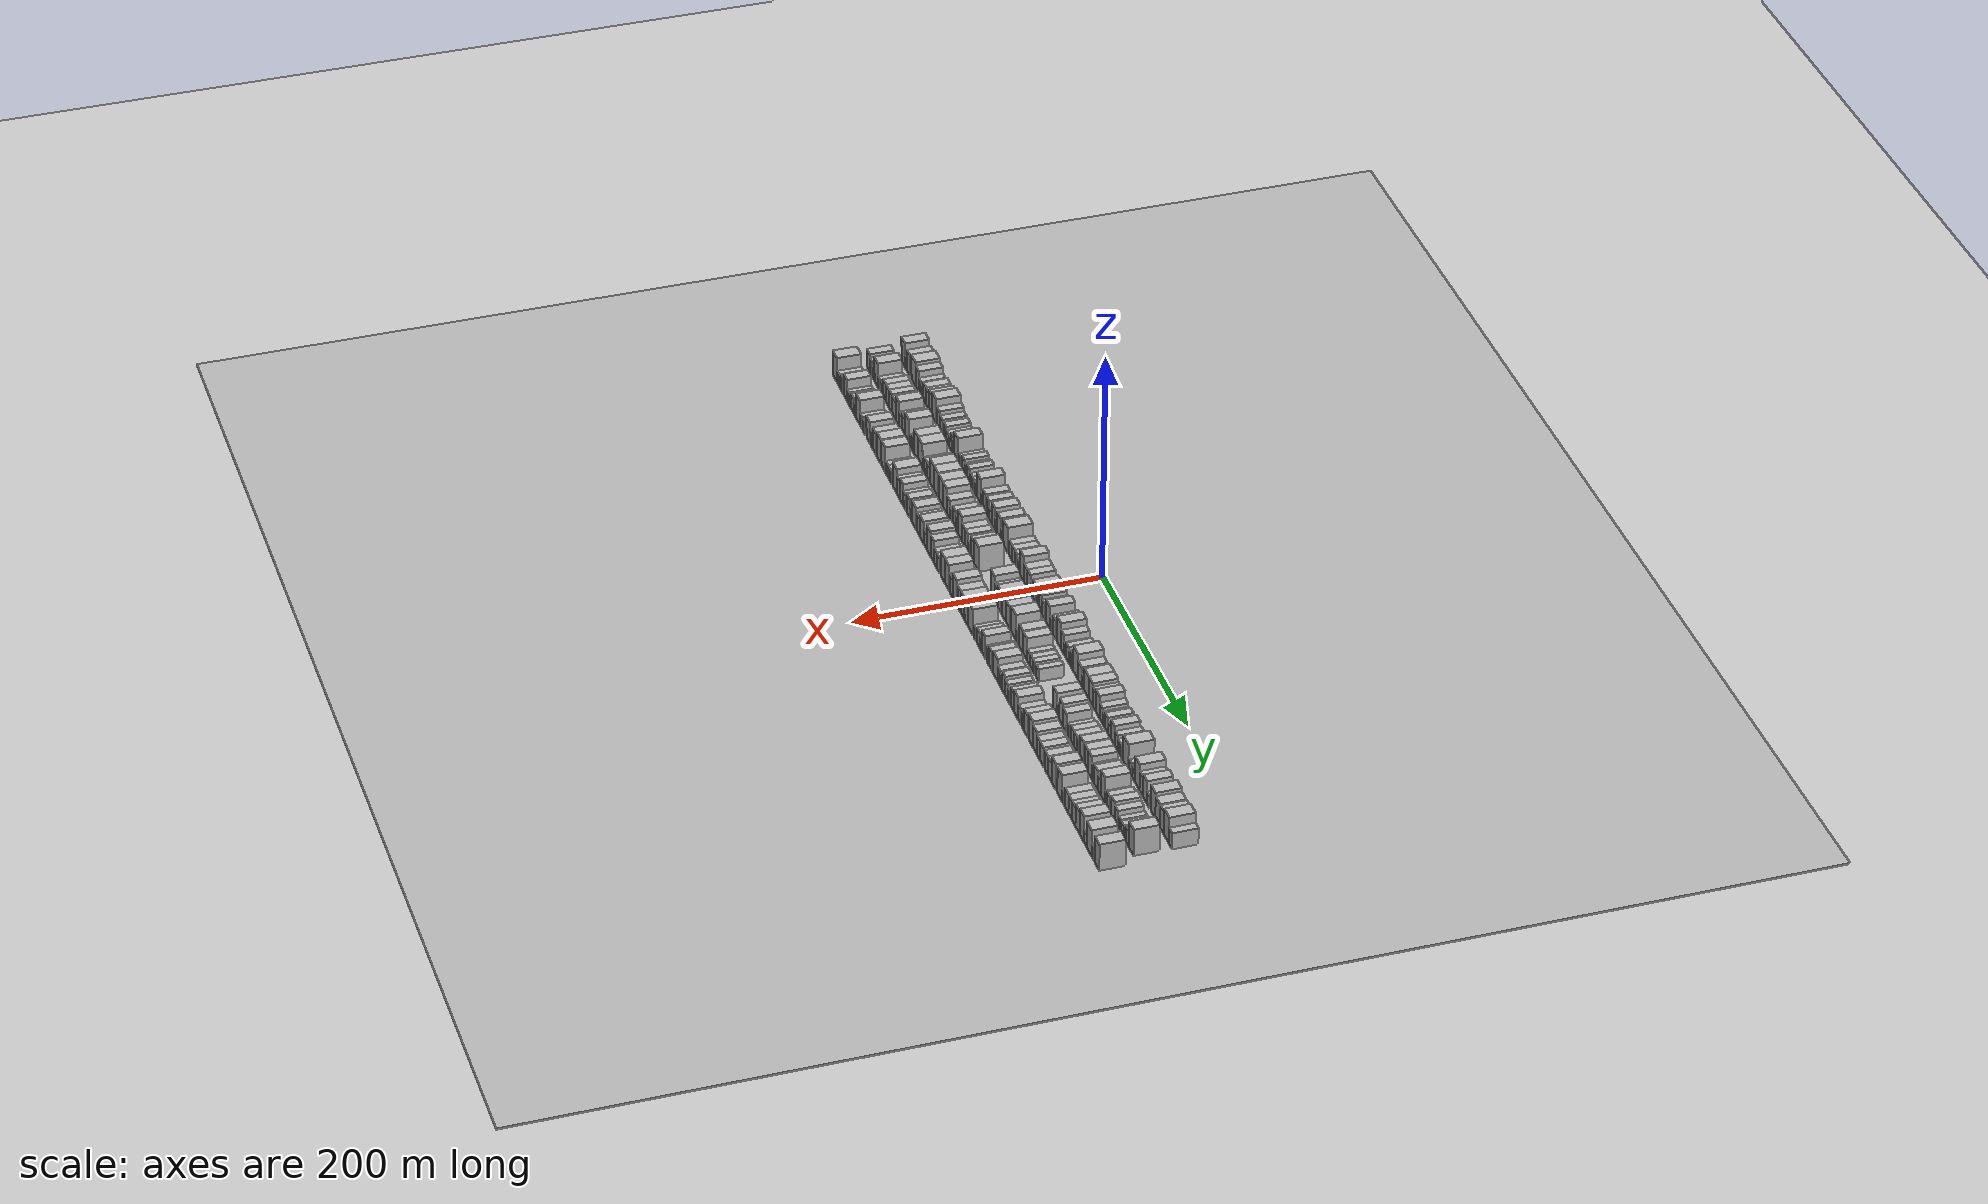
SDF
<?xml version="1.0" encoding="utf-8"?>

<sdf version="1.6">

   <world name="default">

      <gui fullscreen="0">

         <camera name="user_camera">

            <pose>-15 0 4.57585 0 0 0</pose>

            <view_controller>orbit</view_controller>

         </camera>

      </gui>

      <scene>

         <sky>

           <clouds>

             <speed>12</speed>

           </clouds>

         </sky>

         <ambient>0.4 0.4 0.4 1</ambient>

         <background>0.7 0.7 0.7 1</background>

         <shadows>1</shadows>

      </scene>

      <gravity>0 0 -9.8066</gravity>

      <magnetic_field>6e-06 2.3e-05 -4.2e-05</magnetic_field>

      <physics default="0" name="default_physics" type="ode">

         <ode>

            <solver>

               <type>quick</type>

               <iters>10</iters>

               <sor>1.0</sor>

               <use_dynamic_moi_rescaling>0</use_dynamic_moi_rescaling>

            </solver>

            <constraints>

               <cfm>0</cfm>

               <erp>0.2</erp>

               <contact_max_correcting_vel>100</contact_max_correcting_vel>

               <contact_surface_layer>0.001</contact_surface_layer>

            </constraints>

         </ode>

         <max_step_size>0.004</max_step_size>

         <real_time_factor>1</real_time_factor>

         <real_time_update_rate>250</real_time_update_rate>

      </physics>

      <light name="sun" type="directional">

         <cast_shadows>1</cast_shadows>

         <pose>0 0 10 0 0 0</pose>

         <diffuse>0.8 0.8 0.8 1</diffuse>

         <specular>0.2 0.2 0.2 1</specular>

         <attenuation>

            <range>1000</range>

            <constant>0.9</constant>

            <linear>0.01</linear>

            <quadratic>0.001</quadratic>

         </attenuation>

         <direction>-0.5 0.1 -0.9</direction>

      </light>

      <include>

         <name>ground_plane_1</name>

         <uri>model://HANNAS_ground_plane</uri>

         <pose>0 0 0  0 0 0</pose>

      </include>

      <include>

         <name>ground_plane_2</name>

         <uri>model://HANNAS_ground_plane</uri>

         <pose>100 0 0  0 0 0</pose>

      </include>

      <model name="building_1">

         <static>1</static>

         <pose frame="">50.0000 -330.8195 0 0.000000 0.000000 0.000000</pose>

         <link name="link">

            <pose frame="">0 0 12.00 0 0 0</pose>

            <collision name="collision">

               <geometry>

                  <box>

                     <size>20.0000 10.3610 24.0000</size>

                  </box>

               </geometry>

               <max_contacts>10</max_contacts>

               <surface>

                  <contact>

                     <ode/>

                  </contact>

                  <bounce/>

                  <friction>

                     <torsional>

                        <ode/>

                     </torsional>

                     <ode/>

                  </friction>

               </surface>

            </collision>

            <visual name="visual">

               <cast_shadows>0</cast_shadows>

               <geometry>

                  <box>

                     <size>20.0000 10.3610 24.0000</size>

                  </box>

               </geometry>

               <material>

                  <script>

                     <uri>model://HANNAS_wall/materials/scripts</uri>

                     <uri>model://HANNAS_wall/materials/textures</uri>

                     <name>vrc/HANNAS_wall</name>

                  </script>

               </material>

            </visual>

            <self_collide>0</self_collide>

            <enable_wind>0</enable_wind>

            <kinematic>0</kinematic>

         </link>

      </model>

      <model name="building_2">

         <static>1</static>

         <pose frame="">50.0000 -323.1947 0 0.000000 0.000000 0.000000</pose>

         <link name="link">

            <pose frame="">0 0 6.00 0 0 0</pose>

            <collision name="collision">

               <geometry>

                  <box>

                     <size>20.0000 4.8885 12.0000</size>

                  </box>

               </geometry>

               <max_contacts>10</max_contacts>

               <surface>

                  <contact>

                     <ode/>

                  </contact>

                  <bounce/>

                  <friction>

                     <torsional>

                        <ode/>

                     </torsional>

                     <ode/>

                  </friction>

               </surface>

            </collision>

            <visual name="visual">

               <cast_shadows>0</cast_shadows>

               <geometry>

                  <box>

                     <size>20.0000 4.8885 12.0000</size>

                  </box>

               </geometry>

               <material>

                  <script>

                     <uri>model://HANNAS_wall/materials/scripts</uri>

                     <uri>model://HANNAS_wall/materials/textures</uri>

                     <name>vrc/HANNAS_wall</name>

                  </script>

               </material>

            </visual>

            <self_collide>0</self_collide>

            <enable_wind>0</enable_wind>

            <kinematic>0</kinematic>

         </link>

      </model>

      <model name="building_3">

         <static>1</static>

         <pose frame="">50.0000 -316.1677 0 0.000000 0.000000 0.000000</pose>

         <link name="link">

            <pose frame="">0 0 10.50 0 0 0</pose>

            <collision name="collision">

               <geometry>

                  <box>

                     <size>20.0000 9.1656 21.0000</size>

                  </box>

               </geometry>

               <max_contacts>10</max_contacts>

               <surface>

                  <contact>

                     <ode/>

                  </contact>

                  <bounce/>

                  <friction>

                     <torsional>

                        <ode/>

                     </torsional>

                     <ode/>

                  </friction>

               </surface>

            </collision>

            <visual name="visual">

               <cast_shadows>0</cast_shadows>

               <geometry>

                  <box>

                     <size>20.0000 9.1656 21.0000</size>

                  </box>

               </geometry>

               <material>

                  <script>

                     <uri>model://HANNAS_wall/materials/scripts</uri>

                     <uri>model://HANNAS_wall/materials/textures</uri>

                     <name>vrc/HANNAS_wall</name>

                  </script>

               </material>

            </visual>

            <self_collide>0</self_collide>

            <enable_wind>0</enable_wind>

            <kinematic>0</kinematic>

         </link>

      </model>

      <model name="building_4">

         <static>1</static>

         <pose frame="">50.0000 -302.6005 0 0.000000 0.000000 0.000000</pose>

         <link name="link">

            <pose frame="">0 0 12.00 0 0 0</pose>

            <collision name="collision">

               <geometry>

                  <box>

                     <size>20.0000 11.9687 24.0000</size>

                  </box>

               </geometry>

               <max_contacts>10</max_contacts>

               <surface>

                  <contact>

                     <ode/>

                  </contact>

                  <bounce/>

                  <friction>

                     <torsional>

                        <ode/>

                     </torsional>

                     <ode/>

                  </friction>

               </surface>

            </collision>

            <visual name="visual">

               <cast_shadows>0</cast_shadows>

               <geometry>

                  <box>

                     <size>20.0000 11.9687 24.0000</size>

                  </box>

               </geometry>

               <material>

                  <script>

                     <uri>model://HANNAS_wall/materials/scripts</uri>

                     <uri>model://HANNAS_wall/materials/textures</uri>

                     <name>vrc/HANNAS_wall</name>

                  </script>

               </material>

            </visual>

            <self_collide>0</self_collide>

            <enable_wind>0</enable_wind>

            <kinematic>0</kinematic>

         </link>

      </model>

      <model name="building_5">

         <static>1</static>

         <pose frame="">50.0000 -292.1116 0 0.000000 0.000000 0.000000</pose>

         <link name="link">

            <pose frame="">0 0 10.50 0 0 0</pose>

            <collision name="collision">

               <geometry>

                  <box>

                     <size>20.0000 9.0091 21.0000</size>

                  </box>

               </geometry>

               <max_contacts>10</max_contacts>

               <surface>

                  <contact>

                     <ode/>

                  </contact>

                  <bounce/>

                  <friction>

                     <torsional>

                        <ode/>

                     </torsional>

                     <ode/>

                  </friction>

               </surface>

            </collision>

            <visual name="visual">

               <cast_shadows>0</cast_shadows>

               <geometry>

                  <box>

                     <size>20.0000 9.0091 21.0000</size>

                  </box>

               </geometry>

               <material>

                  <script>

                     <uri>model://HANNAS_wall/materials/scripts</uri>

                     <uri>model://HANNAS_wall/materials/textures</uri>

                     <name>vrc/HANNAS_wall</name>

                  </script>

               </material>

            </visual>

            <self_collide>0</self_collide>

            <enable_wind>0</enable_wind>

            <kinematic>0</kinematic>

         </link>

      </model>

      <model name="building_6">

         <static>1</static>

         <pose frame="">50.0000 -284.3590 0 0.000000 0.000000 0.000000</pose>

         <link name="link">

            <pose frame="">0 0 7.50 0 0 0</pose>

            <collision name="collision">

               <geometry>

                  <box>

                     <size>20.0000 6.4960 15.0000</size>

                  </box>

               </geometry>

               <max_contacts>10</max_contacts>

               <surface>

                  <contact>

                     <ode/>

                  </contact>

                  <bounce/>

                  <friction>

                     <torsional>

                        <ode/>

                     </torsional>

                     <ode/>

                  </friction>

               </surface>

            </collision>

            <visual name="visual">

               <cast_shadows>0</cast_shadows>

               <geometry>

                  <box>

                     <size>20.0000 6.4960 15.0000</size>

                  </box>

               </geometry>

               <material>

                  <script>

                     <uri>model://HANNAS_wall/materials/scripts</uri>

                     <uri>model://HANNAS_wall/materials/textures</uri>

                     <name>vrc/HANNAS_wall</name>

                  </script>

               </material>

            </visual>

            <self_collide>0</self_collide>

            <enable_wind>0</enable_wind>

            <kinematic>0</kinematic>

         </link>

      </model>

      <model name="building_7">

         <static>1</static>

         <pose frame="">50.0000 -278.5731 0 0.000000 0.000000 0.000000</pose>

         <link name="link">

            <pose frame="">0 0 6.00 0 0 0</pose>

            <collision name="collision">

               <geometry>

                  <box>

                     <size>20.0000 5.0758 12.0000</size>

                  </box>

               </geometry>

               <max_contacts>10</max_contacts>

               <surface>

                  <contact>

                     <ode/>

                  </contact>

                  <bounce/>

                  <friction>

                     <torsional>

                        <ode/>

                     </torsional>

                     <ode/>

                  </friction>

               </surface>

            </collision>

            <visual name="visual">

               <cast_shadows>0</cast_shadows>

               <geometry>

                  <box>

                     <size>20.0000 5.0758 12.0000</size>

                  </box>

               </geometry>

               <material>

                  <script>

                     <uri>model://HANNAS_wall/materials/scripts</uri>

                     <uri>model://HANNAS_wall/materials/textures</uri>

                     <name>vrc/HANNAS_wall</name>

                  </script>

               </material>

            </visual>

            <self_collide>0</self_collide>

            <enable_wind>0</enable_wind>

            <kinematic>0</kinematic>

         </link>

      </model>

      <model name="building_8">

         <static>1</static>

         <pose frame="">50.0000 -271.8936 0 0.000000 0.000000 0.000000</pose>

         <link name="link">

            <pose frame="">0 0 9.00 0 0 0</pose>

            <collision name="collision">

               <geometry>

                  <box>

                     <size>20.0000 8.2833 18.0000</size>

                  </box>

               </geometry>

               <max_contacts>10</max_contacts>

               <surface>

                  <contact>

                     <ode/>

                  </contact>

                  <bounce/>

                  <friction>

                     <torsional>

                        <ode/>

                     </torsional>

                     <ode/>

                  </friction>

               </surface>

            </collision>

            <visual name="visual">

               <cast_shadows>0</cast_shadows>

               <geometry>

                  <box>

                     <size>20.0000 8.2833 18.0000</size>

                  </box>

               </geometry>

               <material>

                  <script>

                     <uri>model://HANNAS_wall/materials/scripts</uri>

                     <uri>model://HANNAS_wall/materials/textures</uri>

                     <name>vrc/HANNAS_wall</name>

                  </script>

               </material>

            </visual>

            <self_collide>0</self_collide>

            <enable_wind>0</enable_wind>

            <kinematic>0</kinematic>

         </link>

      </model>

      <model name="building_9">

         <static>1</static>

         <pose frame="">50.0000 -263.9527 0 0.000000 0.000000 0.000000</pose>

         <link name="link">

            <pose frame="">0 0 9.00 0 0 0</pose>

            <collision name="collision">

               <geometry>

                  <box>

                     <size>20.0000 7.5986 18.0000</size>

                  </box>

               </geometry>

               <max_contacts>10</max_contacts>

               <surface>

                  <contact>

                     <ode/>

                  </contact>

                  <bounce/>

                  <friction>

                     <torsional>

                        <ode/>

                     </torsional>

                     <ode/>

                  </friction>

               </surface>

            </collision>

            <visual name="visual">

               <cast_shadows>0</cast_shadows>

               <geometry>

                  <box>

                     <size>20.0000 7.5986 18.0000</size>

                  </box>

               </geometry>

               <material>

                  <script>

                     <uri>model://HANNAS_wall/materials/scripts</uri>

                     <uri>model://HANNAS_wall/materials/textures</uri>

                     <name>vrc/HANNAS_wall</name>

                  </script>

               </material>

            </visual>

            <self_collide>0</self_collide>

            <enable_wind>0</enable_wind>

            <kinematic>0</kinematic>

         </link>

      </model>

      <model name="building_10">

         <static>1</static>

         <pose frame="">50.0000 -255.8850 0 0.000000 0.000000 0.000000</pose>

         <link name="link">

            <pose frame="">0 0 10.50 0 0 0</pose>

            <collision name="collision">

               <geometry>

                  <box>

                     <size>20.0000 8.5368 21.0000</size>

                  </box>

               </geometry>

               <max_contacts>10</max_contacts>

               <surface>

                  <contact>

                     <ode/>

                  </contact>

                  <bounce/>

                  <friction>

                     <torsional>

                        <ode/>

                     </torsional>

                     <ode/>

                  </friction>

               </surface>

            </collision>

            <visual name="visual">

               <cast_shadows>0</cast_shadows>

               <geometry>

                  <box>

                     <size>20.0000 8.5368 21.0000</size>

                  </box>

               </geometry>

               <material>

                  <script>

                     <uri>model://HANNAS_wall/materials/scripts</uri>

                     <uri>model://HANNAS_wall/materials/textures</uri>

                     <name>vrc/HANNAS_wall</name>

                  </script>

               </material>

            </visual>

            <self_collide>0</self_collide>

            <enable_wind>0</enable_wind>

            <kinematic>0</kinematic>

         </link>

      </model>

      <model name="building_11">

         <static>1</static>

         <pose frame="">50.0000 -246.0793 0 0.000000 0.000000 0.000000</pose>

         <link name="link">

            <pose frame="">0 0 12.00 0 0 0</pose>

            <collision name="collision">

               <geometry>

                  <box>

                     <size>20.0000 11.0746 24.0000</size>

                  </box>

               </geometry>

               <max_contacts>10</max_contacts>

               <surface>

                  <contact>

                     <ode/>

                  </contact>

                  <bounce/>

                  <friction>

                     <torsional>

                        <ode/>

                     </torsional>

                     <ode/>

                  </friction>

               </surface>

            </collision>

            <visual name="visual">

               <cast_shadows>0</cast_shadows>

               <geometry>

                  <box>

                     <size>20.0000 11.0746 24.0000</size>

                  </box>

               </geometry>

               <material>

                  <script>

                     <uri>model://HANNAS_wall/materials/scripts</uri>

                     <uri>model://HANNAS_wall/materials/textures</uri>

                     <name>vrc/HANNAS_wall</name>

                  </script>

               </material>

            </visual>

            <self_collide>0</self_collide>

            <enable_wind>0</enable_wind>

            <kinematic>0</kinematic>

         </link>

      </model>

      <model name="building_12">

         <static>1</static>

         <pose frame="">50.0000 -235.7469 0 0.000000 0.000000 0.000000</pose>

         <link name="link">

            <pose frame="">0 0 9.00 0 0 0</pose>

            <collision name="collision">

               <geometry>

                  <box>

                     <size>20.0000 7.5902 18.0000</size>

                  </box>

               </geometry>

               <max_contacts>10</max_contacts>

               <surface>

                  <contact>

                     <ode/>

                  </contact>

                  <bounce/>

                  <friction>

                     <torsional>

                        <ode/>

                     </torsional>

                     <ode/>

                  </friction>

               </surface>

            </collision>

            <visual name="visual">

               <cast_shadows>0</cast_shadows>

               <geometry>

                  <box>

                     <size>20.0000 7.5902 18.0000</size>

                  </box>

               </geometry>

               <material>

                  <script>

                     <uri>model://HANNAS_wall/materials/scripts</uri>

                     <uri>model://HANNAS_wall/materials/textures</uri>

                     <name>vrc/HANNAS_wall</name>

                  </script>

               </material>

            </visual>

            <self_collide>0</self_collide>

            <enable_wind>0</enable_wind>

            <kinematic>0</kinematic>

         </link>

      </model>

      <model name="building_13">

         <static>1</static>

         <pose frame="">50.0000 -227.5079 0 0.000000 0.000000 0.000000</pose>

         <link name="link">

            <pose frame="">0 0 7.50 0 0 0</pose>

            <collision name="collision">

               <geometry>

                  <box>

                     <size>20.0000 6.8878 15.0000</size>

                  </box>

               </geometry>

               <max_contacts>10</max_contacts>

               <surface>

                  <contact>

                     <ode/>

                  </contact>

                  <bounce/>

                  <friction>

                     <torsional>

                        <ode/>

                     </torsional>

                     <ode/>

                  </friction>

               </surface>

            </collision>

            <visual name="visual">

               <cast_shadows>0</cast_shadows>

               <geometry>

                  <box>

                     <size>20.0000 6.8878 15.0000</size>

                  </box>

               </geometry>

               <material>

                  <script>

                     <uri>model://HANNAS_wall/materials/scripts</uri>

                     <uri>model://HANNAS_wall/materials/textures</uri>

                     <name>vrc/HANNAS_wall</name>

                  </script>

               </material>

            </visual>

            <self_collide>0</self_collide>

            <enable_wind>0</enable_wind>

            <kinematic>0</kinematic>

         </link>

      </model>

      <model name="building_14">

         <static>1</static>

         <pose frame="">50.0000 -217.3866 0 0.000000 0.000000 0.000000</pose>

         <link name="link">

            <pose frame="">0 0 7.50 0 0 0</pose>

            <collision name="collision">

               <geometry>

                  <box>

                     <size>20.0000 7.3548 15.0000</size>

                  </box>

               </geometry>

               <max_contacts>10</max_contacts>

               <surface>

                  <contact>

                     <ode/>

                  </contact>

                  <bounce/>

                  <friction>

                     <torsional>

                        <ode/>

                     </torsional>

                     <ode/>

                  </friction>

               </surface>

            </collision>

            <visual name="visual">

               <cast_shadows>0</cast_shadows>

               <geometry>

                  <box>

                     <size>20.0000 7.3548 15.0000</size>

                  </box>

               </geometry>

               <material>

                  <script>

                     <uri>model://HANNAS_wall/materials/scripts</uri>

                     <uri>model://HANNAS_wall/materials/textures</uri>

                     <name>vrc/HANNAS_wall</name>

                  </script>

               </material>

            </visual>

            <self_collide>0</self_collide>

            <enable_wind>0</enable_wind>

            <kinematic>0</kinematic>

         </link>

      </model>

      <model name="building_15">

         <static>1</static>

         <pose frame="">50.0000 -210.8543 0 0.000000 0.000000 0.000000</pose>

         <link name="link">

            <pose frame="">0 0 6.00 0 0 0</pose>

            <collision name="collision">

               <geometry>

                  <box>

                     <size>20.0000 5.7099 12.0000</size>

                  </box>

               </geometry>

               <max_contacts>10</max_contacts>

               <surface>

                  <contact>

                     <ode/>

                  </contact>

                  <bounce/>

                  <friction>

                     <torsional>

                        <ode/>

                     </torsional>

                     <ode/>

                  </friction>

               </surface>

            </collision>

            <visual name="visual">

               <cast_shadows>0</cast_shadows>

               <geometry>

                  <box>

                     <size>20.0000 5.7099 12.0000</size>

                  </box>

               </geometry>

               <material>

                  <script>

                     <uri>model://HANNAS_wall/materials/scripts</uri>

                     <uri>model://HANNAS_wall/materials/textures</uri>

                     <name>vrc/HANNAS_wall</name>

                  </script>

               </material>

            </visual>

            <self_collide>0</self_collide>

            <enable_wind>0</enable_wind>

            <kinematic>0</kinematic>

         </link>

      </model>

      <model name="building_16">

         <static>1</static>

         <pose frame="">50.0000 -203.0575 0 0.000000 0.000000 0.000000</pose>

         <link name="link">

            <pose frame="">0 0 6.00 0 0 0</pose>

            <collision name="collision">

               <geometry>

                  <box>

                     <size>20.0000 5.8836 12.0000</size>

                  </box>

               </geometry>

               <max_contacts>10</max_contacts>

               <surface>

                  <contact>

                     <ode/>

                  </contact>

                  <bounce/>

                  <friction>

                     <torsional>

                        <ode/>

                     </torsional>

                     <ode/>

                  </friction>

               </surface>

            </collision>

            <visual name="visual">

               <cast_shadows>0</cast_shadows>

               <geometry>

                  <box>

                     <size>20.0000 5.8836 12.0000</size>

                  </box>

               </geometry>

               <material>

                  <script>

                     <uri>model://HANNAS_wall/materials/scripts</uri>

                     <uri>model://HANNAS_wall/materials/textures</uri>

                     <name>vrc/HANNAS_wall</name>

                  </script>

               </material>

            </visual>

            <self_collide>0</self_collide>

            <enable_wind>0</enable_wind>

            <kinematic>0</kinematic>

         </link>

      </model>

      <model name="building_17">

         <static>1</static>

         <pose frame="">50.0000 -196.3633 0 0.000000 0.000000 0.000000</pose>

         <link name="link">

            <pose frame="">0 0 9.00 0 0 0</pose>

            <collision name="collision">

               <geometry>

                  <box>

                     <size>20.0000 7.5048 18.0000</size>

                  </box>

               </geometry>

               <max_contacts>10</max_contacts>

               <surface>

                  <contact>

                     <ode/>

                  </contact>

                  <bounce/>

                  <friction>

                     <torsional>

                        <ode/>

                     </torsional>

                     <ode/>

                  </friction>

               </surface>

            </collision>

            <visual name="visual">

               <cast_shadows>0</cast_shadows>

               <geometry>

                  <box>

                     <size>20.0000 7.5048 18.0000</size>

                  </box>

               </geometry>

               <material>

                  <script>

                     <uri>model://HANNAS_wall/materials/scripts</uri>

                     <uri>model://HANNAS_wall/materials/textures</uri>

                     <name>vrc/HANNAS_wall</name>

                  </script>

               </material>

            </visual>

            <self_collide>0</self_collide>

            <enable_wind>0</enable_wind>

            <kinematic>0</kinematic>

         </link>

      </model>

      <model name="building_18">

         <static>1</static>

         <pose frame="">50.0000 -187.6066 0 0.000000 0.000000 0.000000</pose>

         <link name="link">

            <pose frame="">0 0 12.00 0 0 0</pose>

            <collision name="collision">

               <geometry>

                  <box>

                     <size>20.0000 10.0087 24.0000</size>

                  </box>

               </geometry>

               <max_contacts>10</max_contacts>

               <surface>

                  <contact>

                     <ode/>

                  </contact>

                  <bounce/>

                  <friction>

                     <torsional>

                        <ode/>

                     </torsional>

                     <ode/>

                  </friction>

               </surface>

            </collision>

            <visual name="visual">

               <cast_shadows>0</cast_shadows>

               <geometry>

                  <box>

                     <size>20.0000 10.0087 24.0000</size>

                  </box>

               </geometry>

               <material>

                  <script>

                     <uri>model://HANNAS_wall/materials/scripts</uri>

                     <uri>model://HANNAS_wall/materials/textures</uri>

                     <name>vrc/HANNAS_wall</name>

                  </script>

               </material>

            </visual>

            <self_collide>0</self_collide>

            <enable_wind>0</enable_wind>

            <kinematic>0</kinematic>

         </link>

      </model>

      <model name="building_19">

         <static>1</static>

         <pose frame="">50.0000 -177.1057 0 0.000000 0.000000 0.000000</pose>

         <link name="link">

            <pose frame="">0 0 6.00 0 0 0</pose>

            <collision name="collision">

               <geometry>

                  <box>

                     <size>20.0000 4.9930 12.0000</size>

                  </box>

               </geometry>

               <max_contacts>10</max_contacts>

               <surface>

                  <contact>

                     <ode/>

                  </contact>

                  <bounce/>

                  <friction>

                     <torsional>

                        <ode/>

                     </torsional>

                     <ode/>

                  </friction>

               </surface>

            </collision>

            <visual name="visual">

               <cast_shadows>0</cast_shadows>

               <geometry>

                  <box>

                     <size>20.0000 4.9930 12.0000</size>

                  </box>

               </geometry>

               <material>

                  <script>

                     <uri>model://HANNAS_wall/materials/scripts</uri>

                     <uri>model://HANNAS_wall/materials/textures</uri>

                     <name>vrc/HANNAS_wall</name>

                  </script>

               </material>

            </visual>

            <self_collide>0</self_collide>

            <enable_wind>0</enable_wind>

            <kinematic>0</kinematic>

         </link>

      </model>

      <model name="building_20">

         <static>1</static>

         <pose frame="">50.0000 -168.3583 0 0.000000 0.000000 0.000000</pose>

         <link name="link">

            <pose frame="">0 0 7.50 0 0 0</pose>

            <collision name="collision">

               <geometry>

                  <box>

                     <size>20.0000 6.5018 15.0000</size>

                  </box>

               </geometry>

               <max_contacts>10</max_contacts>

               <surface>

                  <contact>

                     <ode/>

                  </contact>

                  <bounce/>

                  <friction>

                     <torsional>

                        <ode/>

                     </torsional>

                     <ode/>

                  </friction>

               </surface>

            </collision>

            <visual name="visual">

               <cast_shadows>0</cast_shadows>

               <geometry>

                  <box>

                     <size>20.0000 6.5018 15.0000</size>

                  </box>

               </geometry>

               <material>

                  <script>

                     <uri>model://HANNAS_wall/materials/scripts</uri>

                     <uri>model://HANNAS_wall/materials/textures</uri>

                     <name>vrc/HANNAS_wall</name>

                  </script>

               </material>

            </visual>

            <self_collide>0</self_collide>

            <enable_wind>0</enable_wind>

            <kinematic>0</kinematic>

         </link>

      </model>

      <model name="building_21">

         <static>1</static>

         <pose frame="">50.0000 -162.2351 0 0.000000 0.000000 0.000000</pose>

         <link name="link">

            <pose frame="">0 0 6.00 0 0 0</pose>

            <collision name="collision">

               <geometry>

                  <box>

                     <size>20.0000 5.7445 12.0000</size>

                  </box>

               </geometry>

               <max_contacts>10</max_contacts>

               <surface>

                  <contact>

                     <ode/>

                  </contact>

                  <bounce/>

                  <friction>

                     <torsional>

                        <ode/>

                     </torsional>

                     <ode/>

                  </friction>

               </surface>

            </collision>

            <visual name="visual">

               <cast_shadows>0</cast_shadows>

               <geometry>

                  <box>

                     <size>20.0000 5.7445 12.0000</size>

                  </box>

               </geometry>

               <material>

                  <script>

                     <uri>model://HANNAS_wall/materials/scripts</uri>

                     <uri>model://HANNAS_wall/materials/textures</uri>

                     <name>vrc/HANNAS_wall</name>

                  </script>

               </material>

            </visual>

            <self_collide>0</self_collide>

            <enable_wind>0</enable_wind>

            <kinematic>0</kinematic>

         </link>

      </model>

      <model name="building_22">

         <static>1</static>

         <pose frame="">50.0000 -154.9990 0 0.000000 0.000000 0.000000</pose>

         <link name="link">

            <pose frame="">0 0 7.50 0 0 0</pose>

            <collision name="collision">

               <geometry>

                  <box>

                     <size>20.0000 6.7277 15.0000</size>

                  </box>

               </geometry>

               <max_contacts>10</max_contacts>

               <surface>

                  <contact>

                     <ode/>

                  </contact>

                  <bounce/>

                  <friction>

                     <torsional>

                        <ode/>

                     </torsional>

                     <ode/>

                  </friction>

               </surface>

            </collision>

            <visual name="visual">

               <cast_shadows>0</cast_shadows>

               <geometry>

                  <box>

                     <size>20.0000 6.7277 15.0000</size>

                  </box>

               </geometry>

               <material>

                  <script>

                     <uri>model://HANNAS_wall/materials/scripts</uri>

                     <uri>model://HANNAS_wall/materials/textures</uri>

                     <name>vrc/HANNAS_wall</name>

                  </script>

               </material>

            </visual>

            <self_collide>0</self_collide>

            <enable_wind>0</enable_wind>

            <kinematic>0</kinematic>

         </link>

      </model>

      <model name="building_23">

         <static>1</static>

         <pose frame="">50.0000 -147.8315 0 0.000000 0.000000 0.000000</pose>

         <link name="link">

            <pose frame="">0 0 6.00 0 0 0</pose>

            <collision name="collision">

               <geometry>

                  <box>

                     <size>20.0000 5.6074 12.0000</size>

                  </box>

               </geometry>

               <max_contacts>10</max_contacts>

               <surface>

                  <contact>

                     <ode/>

                  </contact>

                  <bounce/>

                  <friction>

                     <torsional>

                        <ode/>

                     </torsional>

                     <ode/>

                  </friction>

               </surface>

            </collision>

            <visual name="visual">

               <cast_shadows>0</cast_shadows>

               <geometry>

                  <box>

                     <size>20.0000 5.6074 12.0000</size>

                  </box>

               </geometry>

               <material>

                  <script>

                     <uri>model://HANNAS_wall/materials/scripts</uri>

                     <uri>model://HANNAS_wall/materials/textures</uri>

                     <name>vrc/HANNAS_wall</name>

                  </script>

               </material>

            </visual>

            <self_collide>0</self_collide>

            <enable_wind>0</enable_wind>

            <kinematic>0</kinematic>

         </link>

      </model>

      <model name="building_24">

         <static>1</static>

         <pose frame="">50.0000 -142.5548 0 0.000000 0.000000 0.000000</pose>

         <link name="link">

            <pose frame="">0 0 6.00 0 0 0</pose>

            <collision name="collision">

               <geometry>

                  <box>

                     <size>20.0000 4.9459 12.0000</size>

                  </box>

               </geometry>

               <max_contacts>10</max_contacts>

               <surface>

                  <contact>

                     <ode/>

                  </contact>

                  <bounce/>

                  <friction>

                     <torsional>

                        <ode/>

                     </torsional>

                     <ode/>

                  </friction>

               </surface>

            </collision>

            <visual name="visual">

               <cast_shadows>0</cast_shadows>

               <geometry>

                  <box>

                     <size>20.0000 4.9459 12.0000</size>

                  </box>

               </geometry>

               <material>

                  <script>

                     <uri>model://HANNAS_wall/materials/scripts</uri>

                     <uri>model://HANNAS_wall/materials/textures</uri>

                     <name>vrc/HANNAS_wall</name>

                  </script>

               </material>

            </visual>

            <self_collide>0</self_collide>

            <enable_wind>0</enable_wind>

            <kinematic>0</kinematic>

         </link>

      </model>

      <model name="building_25">

         <static>1</static>

         <pose frame="">50.0000 -136.3060 0 0.000000 0.000000 0.000000</pose>

         <link name="link">

            <pose frame="">0 0 6.00 0 0 0</pose>

            <collision name="collision">

               <geometry>

                  <box>

                     <size>20.0000 5.5518 12.0000</size>

                  </box>

               </geometry>

               <max_contacts>10</max_contacts>

               <surface>

                  <contact>

                     <ode/>

                  </contact>

                  <bounce/>

                  <friction>

                     <torsional>

                        <ode/>

                     </torsional>

                     <ode/>

                  </friction>

               </surface>

            </collision>

            <visual name="visual">

               <cast_shadows>0</cast_shadows>

               <geometry>

                  <box>

                     <size>20.0000 5.5518 12.0000</size>

                  </box>

               </geometry>

               <material>

                  <script>

                     <uri>model://HANNAS_wall/materials/scripts</uri>

                     <uri>model://HANNAS_wall/materials/textures</uri>

                     <name>vrc/HANNAS_wall</name>

                  </script>

               </material>

            </visual>

            <self_collide>0</self_collide>

            <enable_wind>0</enable_wind>

            <kinematic>0</kinematic>

         </link>

      </model>

      <model name="building_26">

         <static>1</static>

         <pose frame="">50.0000 -128.3769 0 0.000000 0.000000 0.000000</pose>

         <link name="link">

            <pose frame="">0 0 12.00 0 0 0</pose>

            <collision name="collision">

               <geometry>

                  <box>

                     <size>20.0000 10.3064 24.0000</size>

                  </box>

               </geometry>

               <max_contacts>10</max_contacts>

               <surface>

                  <contact>

                     <ode/>

                  </contact>

                  <bounce/>

                  <friction>

                     <torsional>

                        <ode/>

                     </torsional>

                     <ode/>

                  </friction>

               </surface>

            </collision>

            <visual name="visual">

               <cast_shadows>0</cast_shadows>

               <geometry>

                  <box>

                     <size>20.0000 10.3064 24.0000</size>

                  </box>

               </geometry>

               <material>

                  <script>

                     <uri>model://HANNAS_wall/materials/scripts</uri>

                     <uri>model://HANNAS_wall/materials/textures</uri>

                     <name>vrc/HANNAS_wall</name>

                  </script>

               </material>

            </visual>

            <self_collide>0</self_collide>

            <enable_wind>0</enable_wind>

            <kinematic>0</kinematic>

         </link>

      </model>

      <model name="building_27">

         <static>1</static>

         <pose frame="">50.0000 -120.7325 0 0.000000 0.000000 0.000000</pose>

         <link name="link">

            <pose frame="">0 0 6.00 0 0 0</pose>

            <collision name="collision">

               <geometry>

                  <box>

                     <size>20.0000 4.9823 12.0000</size>

                  </box>

               </geometry>

               <max_contacts>10</max_contacts>

               <surface>

                  <contact>

                     <ode/>

                  </contact>

                  <bounce/>

                  <friction>

                     <torsional>

                        <ode/>

                     </torsional>

                     <ode/>

                  </friction>

               </surface>

            </collision>

            <visual name="visual">

               <cast_shadows>0</cast_shadows>

               <geometry>

                  <box>

                     <size>20.0000 4.9823 12.0000</size>

                  </box>

               </geometry>

               <material>

                  <script>

                     <uri>model://HANNAS_wall/materials/scripts</uri>

                     <uri>model://HANNAS_wall/materials/textures</uri>

                     <name>vrc/HANNAS_wall</name>

                  </script>

               </material>

            </visual>

            <self_collide>0</self_collide>

            <enable_wind>0</enable_wind>

            <kinematic>0</kinematic>

         </link>

      </model>

      <model name="building_28">

         <static>1</static>

         <pose frame="">50.0000 -114.1431 0 0.000000 0.000000 0.000000</pose>

         <link name="link">

            <pose frame="">0 0 9.00 0 0 0</pose>

            <collision name="collision">

               <geometry>

                  <box>

                     <size>20.0000 8.1966 18.0000</size>

                  </box>

               </geometry>

               <max_contacts>10</max_contacts>

               <surface>

                  <contact>

                     <ode/>

                  </contact>

                  <bounce/>

                  <friction>

                     <torsional>

                        <ode/>

                     </torsional>

                     <ode/>

                  </friction>

               </surface>

            </collision>

            <visual name="visual">

               <cast_shadows>0</cast_shadows>

               <geometry>

                  <box>

                     <size>20.0000 8.1966 18.0000</size>

                  </box>

               </geometry>

               <material>

                  <script>

                     <uri>model://HANNAS_wall/materials/scripts</uri>

                     <uri>model://HANNAS_wall/materials/textures</uri>

                     <name>vrc/HANNAS_wall</name>

                  </script>

               </material>

            </visual>

            <self_collide>0</self_collide>

            <enable_wind>0</enable_wind>

            <kinematic>0</kinematic>

         </link>

      </model>

      <model name="building_29">

         <static>1</static>

         <pose frame="">50.0000 -104.4362 0 0.000000 0.000000 0.000000</pose>

         <link name="link">

            <pose frame="">0 0 9.00 0 0 0</pose>

            <collision name="collision">

               <geometry>

                  <box>

                     <size>20.0000 7.2170 18.0000</size>

                  </box>

               </geometry>

               <max_contacts>10</max_contacts>

               <surface>

                  <contact>

                     <ode/>

                  </contact>

                  <bounce/>

                  <friction>

                     <torsional>

                        <ode/>

                     </torsional>

                     <ode/>

                  </friction>

               </surface>

            </collision>

            <visual name="visual">

               <cast_shadows>0</cast_shadows>

               <geometry>

                  <box>

                     <size>20.0000 7.2170 18.0000</size>

                  </box>

               </geometry>

               <material>

                  <script>

                     <uri>model://HANNAS_wall/materials/scripts</uri>

                     <uri>model://HANNAS_wall/materials/textures</uri>

                     <name>vrc/HANNAS_wall</name>

                  </script>

               </material>

            </visual>

            <self_collide>0</self_collide>

            <enable_wind>0</enable_wind>

            <kinematic>0</kinematic>

         </link>

      </model>

      <model name="building_30">

         <static>1</static>

         <pose frame="">50.0000 -97.9253 0 0.000000 0.000000 0.000000</pose>

         <link name="link">

            <pose frame="">0 0 6.00 0 0 0</pose>

            <collision name="collision">

               <geometry>

                  <box>

                     <size>20.0000 5.8047 12.0000</size>

                  </box>

               </geometry>

               <max_contacts>10</max_contacts>

               <surface>

                  <contact>

                     <ode/>

                  </contact>

                  <bounce/>

                  <friction>

                     <torsional>

                        <ode/>

                     </torsional>

                     <ode/>

                  </friction>

               </surface>

            </collision>

            <visual name="visual">

               <cast_shadows>0</cast_shadows>

               <geometry>

                  <box>

                     <size>20.0000 5.8047 12.0000</size>

                  </box>

               </geometry>

               <material>

                  <script>

                     <uri>model://HANNAS_wall/materials/scripts</uri>

                     <uri>model://HANNAS_wall/materials/textures</uri>

                     <name>vrc/HANNAS_wall</name>

                  </script>

               </material>

            </visual>

            <self_collide>0</self_collide>

            <enable_wind>0</enable_wind>

            <kinematic>0</kinematic>

         </link>

      </model>

      <model name="building_31">

         <static>1</static>

         <pose frame="">50.0000 -90.2111 0 0.000000 0.000000 0.000000</pose>

         <link name="link">

            <pose frame="">0 0 10.50 0 0 0</pose>

            <collision name="collision">

               <geometry>

                  <box>

                     <size>20.0000 9.6238 21.0000</size>

                  </box>

               </geometry>

               <max_contacts>10</max_contacts>

               <surface>

                  <contact>

                     <ode/>

                  </contact>

                  <bounce/>

                  <friction>

                     <torsional>

                        <ode/>

                     </torsional>

                     <ode/>

                  </friction>

               </surface>

            </collision>

            <visual name="visual">

               <cast_shadows>0</cast_shadows>

               <geometry>

                  <box>

                     <size>20.0000 9.6238 21.0000</size>

                  </box>

               </geometry>

               <material>

                  <script>

                     <uri>model://HANNAS_wall/materials/scripts</uri>

                     <uri>model://HANNAS_wall/materials/textures</uri>

                     <name>vrc/HANNAS_wall</name>

                  </script>

               </material>

            </visual>

            <self_collide>0</self_collide>

            <enable_wind>0</enable_wind>

            <kinematic>0</kinematic>

         </link>

      </model>

      <model name="building_32">

         <static>1</static>

         <pose frame="">50.0000 -82.6925 0 0.000000 0.000000 0.000000</pose>

         <link name="link">

            <pose frame="">0 0 6.00 0 0 0</pose>

            <collision name="collision">

               <geometry>

                  <box>

                     <size>20.0000 5.4133 12.0000</size>

                  </box>

               </geometry>

               <max_contacts>10</max_contacts>

               <surface>

                  <contact>

                     <ode/>

                  </contact>

                  <bounce/>

                  <friction>

                     <torsional>

                        <ode/>

                     </torsional>

                     <ode/>

                  </friction>

               </surface>

            </collision>

            <visual name="visual">

               <cast_shadows>0</cast_shadows>

               <geometry>

                  <box>

                     <size>20.0000 5.4133 12.0000</size>

                  </box>

               </geometry>

               <material>

                  <script>

                     <uri>model://HANNAS_wall/materials/scripts</uri>

                     <uri>model://HANNAS_wall/materials/textures</uri>

                     <name>vrc/HANNAS_wall</name>

                  </script>

               </material>

            </visual>

            <self_collide>0</self_collide>

            <enable_wind>0</enable_wind>

            <kinematic>0</kinematic>

         </link>

      </model>

      <model name="building_33">

         <static>1</static>

         <pose frame="">50.0000 -75.5466 0 0.000000 0.000000 0.000000</pose>

         <link name="link">

            <pose frame="">0 0 10.50 0 0 0</pose>

            <collision name="collision">

               <geometry>

                  <box>

                     <size>20.0000 8.8786 21.0000</size>

                  </box>

               </geometry>

               <max_contacts>10</max_contacts>

               <surface>

                  <contact>

                     <ode/>

                  </contact>

                  <bounce/>

                  <friction>

                     <torsional>

                        <ode/>

                     </torsional>

                     <ode/>

                  </friction>

               </surface>

            </collision>

            <visual name="visual">

               <cast_shadows>0</cast_shadows>

               <geometry>

                  <box>

                     <size>20.0000 8.8786 21.0000</size>

                  </box>

               </geometry>

               <material>

                  <script>

                     <uri>model://HANNAS_wall/materials/scripts</uri>

                     <uri>model://HANNAS_wall/materials/textures</uri>

                     <name>vrc/HANNAS_wall</name>

                  </script>

               </material>

            </visual>

            <self_collide>0</self_collide>

            <enable_wind>0</enable_wind>

            <kinematic>0</kinematic>

         </link>

      </model>

      <model name="building_34">

         <static>1</static>

         <pose frame="">50.0000 -68.1127 0 0.000000 0.000000 0.000000</pose>

         <link name="link">

            <pose frame="">0 0 6.00 0 0 0</pose>

            <collision name="collision">

               <geometry>

                  <box>

                     <size>20.0000 5.9891 12.0000</size>

                  </box>

               </geometry>

               <max_contacts>10</max_contacts>

               <surface>

                  <contact>

                     <ode/>

                  </contact>

                  <bounce/>

                  <friction>

                     <torsional>

                        <ode/>

                     </torsional>

                     <ode/>

                  </friction>

               </surface>

            </collision>

            <visual name="visual">

               <cast_shadows>0</cast_shadows>

               <geometry>

                  <box>

                     <size>20.0000 5.9891 12.0000</size>

                  </box>

               </geometry>

               <material>

                  <script>

                     <uri>model://HANNAS_wall/materials/scripts</uri>

                     <uri>model://HANNAS_wall/materials/textures</uri>

                     <name>vrc/HANNAS_wall</name>

                  </script>

               </material>

            </visual>

            <self_collide>0</self_collide>

            <enable_wind>0</enable_wind>

            <kinematic>0</kinematic>

         </link>

      </model>

      <model name="building_35">

         <static>1</static>

         <pose frame="">50.0000 -59.1276 0 0.000000 0.000000 0.000000</pose>

         <link name="link">

            <pose frame="">0 0 12.00 0 0 0</pose>

            <collision name="collision">

               <geometry>

                  <box>

                     <size>20.0000 11.9812 24.0000</size>

                  </box>

               </geometry>

               <max_contacts>10</max_contacts>

               <surface>

                  <contact>

                     <ode/>

                  </contact>

                  <bounce/>

                  <friction>

                     <torsional>

                        <ode/>

                     </torsional>

                     <ode/>

                  </friction>

               </surface>

            </collision>

            <visual name="visual">

               <cast_shadows>0</cast_shadows>

               <geometry>

                  <box>

                     <size>20.0000 11.9812 24.0000</size>

                  </box>

               </geometry>

               <material>

                  <script>

                     <uri>model://HANNAS_wall/materials/scripts</uri>

                     <uri>model://HANNAS_wall/materials/textures</uri>

                     <name>vrc/HANNAS_wall</name>

                  </script>

               </material>

            </visual>

            <self_collide>0</self_collide>

            <enable_wind>0</enable_wind>

            <kinematic>0</kinematic>

         </link>

      </model>

      <model name="building_36">

         <static>1</static>

         <pose frame="">50.0000 -46.4230 0 0.000000 0.000000 0.000000</pose>

         <link name="link">

            <pose frame="">0 0 7.50 0 0 0</pose>

            <collision name="collision">

               <geometry>

                  <box>

                     <size>20.0000 7.4280 15.0000</size>

                  </box>

               </geometry>

               <max_contacts>10</max_contacts>

               <surface>

                  <contact>

                     <ode/>

                  </contact>

                  <bounce/>

                  <friction>

                     <torsional>

                        <ode/>

                     </torsional>

                     <ode/>

                  </friction>

               </surface>

            </collision>

            <visual name="visual">

               <cast_shadows>0</cast_shadows>

               <geometry>

                  <box>

                     <size>20.0000 7.4280 15.0000</size>

                  </box>

               </geometry>

               <material>

                  <script>

                     <uri>model://HANNAS_wall/materials/scripts</uri>

                     <uri>model://HANNAS_wall/materials/textures</uri>

                     <name>vrc/HANNAS_wall</name>

                  </script>

               </material>

            </visual>

            <self_collide>0</self_collide>

            <enable_wind>0</enable_wind>

            <kinematic>0</kinematic>

         </link>

      </model>

      <model name="building_37">

         <static>1</static>

         <pose frame="">50.0000 -39.2304 0 0.000000 0.000000 0.000000</pose>

         <link name="link">

            <pose frame="">0 0 7.50 0 0 0</pose>

            <collision name="collision">

               <geometry>

                  <box>

                     <size>20.0000 6.9572 15.0000</size>

                  </box>

               </geometry>

               <max_contacts>10</max_contacts>

               <surface>

                  <contact>

                     <ode/>

                  </contact>

                  <bounce/>

                  <friction>

                     <torsional>

                        <ode/>

                     </torsional>

                     <ode/>

                  </friction>

               </surface>

            </collision>

            <visual name="visual">

               <cast_shadows>0</cast_shadows>

               <geometry>

                  <box>

                     <size>20.0000 6.9572 15.0000</size>

                  </box>

               </geometry>

               <material>

                  <script>

                     <uri>model://HANNAS_wall/materials/scripts</uri>

                     <uri>model://HANNAS_wall/materials/textures</uri>

                     <name>vrc/HANNAS_wall</name>

                  </script>

               </material>

            </visual>

            <self_collide>0</self_collide>

            <enable_wind>0</enable_wind>

            <kinematic>0</kinematic>

         </link>

      </model>

      <model name="building_38">

         <static>1</static>

         <pose frame="">50.0000 -32.4858 0 0.000000 0.000000 0.000000</pose>

         <link name="link">

            <pose frame="">0 0 7.50 0 0 0</pose>

            <collision name="collision">

               <geometry>

                  <box>

                     <size>20.0000 6.5319 15.0000</size>

                  </box>

               </geometry>

               <max_contacts>10</max_contacts>

               <surface>

                  <contact>

                     <ode/>

                  </contact>

                  <bounce/>

                  <friction>

                     <torsional>

                        <ode/>

                     </torsional>

                     <ode/>

                  </friction>

               </surface>

            </collision>

            <visual name="visual">

               <cast_shadows>0</cast_shadows>

               <geometry>

                  <box>

                     <size>20.0000 6.5319 15.0000</size>

                  </box>

               </geometry>

               <material>

                  <script>

                     <uri>model://HANNAS_wall/materials/scripts</uri>

                     <uri>model://HANNAS_wall/materials/textures</uri>

                     <name>vrc/HANNAS_wall</name>

                  </script>

               </material>

            </visual>

            <self_collide>0</self_collide>

            <enable_wind>0</enable_wind>

            <kinematic>0</kinematic>

         </link>

      </model>

      <model name="building_39">

         <static>1</static>

         <pose frame="">50.0000 -25.2699 0 0.000000 0.000000 0.000000</pose>

         <link name="link">

            <pose frame="">0 0 6.00 0 0 0</pose>

            <collision name="collision">

               <geometry>

                  <box>

                     <size>20.0000 5.8999 12.0000</size>

                  </box>

               </geometry>

               <max_contacts>10</max_contacts>

               <surface>

                  <contact>

                     <ode/>

                  </contact>

                  <bounce/>

                  <friction>

                     <torsional>

                        <ode/>

                     </torsional>

                     <ode/>

                  </friction>

               </surface>

            </collision>

            <visual name="visual">

               <cast_shadows>0</cast_shadows>

               <geometry>

                  <box>

                     <size>20.0000 5.8999 12.0000</size>

                  </box>

               </geometry>

               <material>

                  <script>

                     <uri>model://HANNAS_wall/materials/scripts</uri>

                     <uri>model://HANNAS_wall/materials/textures</uri>

                     <name>vrc/HANNAS_wall</name>

                  </script>

               </material>

            </visual>

            <self_collide>0</self_collide>

            <enable_wind>0</enable_wind>

            <kinematic>0</kinematic>

         </link>

      </model>

      <model name="building_40">

         <static>1</static>

         <pose frame="">50.0000 -17.4124 0 0.000000 0.000000 0.000000</pose>

         <link name="link">

            <pose frame="">0 0 12.00 0 0 0</pose>

            <collision name="collision">

               <geometry>

                  <box>

                     <size>20.0000 9.8151 24.0000</size>

                  </box>

               </geometry>

               <max_contacts>10</max_contacts>

               <surface>

                  <contact>

                     <ode/>

                  </contact>

                  <bounce/>

                  <friction>

                     <torsional>

                        <ode/>

                     </torsional>

                     <ode/>

                  </friction>

               </surface>

            </collision>

            <visual name="visual">

               <cast_shadows>0</cast_shadows>

               <geometry>

                  <box>

                     <size>20.0000 9.8151 24.0000</size>

                  </box>

               </geometry>

               <material>

                  <script>

                     <uri>model://HANNAS_wall/materials/scripts</uri>

                     <uri>model://HANNAS_wall/materials/textures</uri>

                     <name>vrc/HANNAS_wall</name>

                  </script>

               </material>

            </visual>

            <self_collide>0</self_collide>

            <enable_wind>0</enable_wind>

            <kinematic>0</kinematic>

         </link>

      </model>

      <model name="building_41">

         <static>1</static>

         <pose frame="">50.0000 -8.1402 0 0.000000 0.000000 0.000000</pose>

         <link name="link">

            <pose frame="">0 0 9.00 0 0 0</pose>

            <collision name="collision">

               <geometry>

                  <box>

                     <size>20.0000 8.7293 18.0000</size>

                  </box>

               </geometry>

               <max_contacts>10</max_contacts>

               <surface>

                  <contact>

                     <ode/>

                  </contact>

                  <bounce/>

                  <friction>

                     <torsional>

                        <ode/>

                     </torsional>

                     <ode/>

                  </friction>

               </surface>

            </collision>

            <visual name="visual">

               <cast_shadows>0</cast_shadows>

               <geometry>

                  <box>

                     <size>20.0000 8.7293 18.0000</size>

                  </box>

               </geometry>

               <material>

                  <script>

                     <uri>model://HANNAS_wall/materials/scripts</uri>

                     <uri>model://HANNAS_wall/materials/textures</uri>

                     <name>vrc/HANNAS_wall</name>

                  </script>

               </material>

            </visual>

            <self_collide>0</self_collide>

            <enable_wind>0</enable_wind>

            <kinematic>0</kinematic>

         </link>

      </model>

      <model name="building_42">

         <static>1</static>

         <pose frame="">50.0000 0.0508 0 0.000000 0.000000 0.000000</pose>

         <link name="link">

            <pose frame="">0 0 9.00 0 0 0</pose>

            <collision name="collision">

               <geometry>

                  <box>

                     <size>20.0000 7.6527 18.0000</size>

                  </box>

               </geometry>

               <max_contacts>10</max_contacts>

               <surface>

                  <contact>

                     <ode/>

                  </contact>

                  <bounce/>

                  <friction>

                     <torsional>

                        <ode/>

                     </torsional>

                     <ode/>

                  </friction>

               </surface>

            </collision>

            <visual name="visual">

               <cast_shadows>0</cast_shadows>

               <geometry>

                  <box>

                     <size>20.0000 7.6527 18.0000</size>

                  </box>

               </geometry>

               <material>

                  <script>

                     <uri>model://HANNAS_wall/materials/scripts</uri>

                     <uri>model://HANNAS_wall/materials/textures</uri>

                     <name>vrc/HANNAS_wall</name>

                  </script>

               </material>

            </visual>

            <self_collide>0</self_collide>

            <enable_wind>0</enable_wind>

            <kinematic>0</kinematic>

         </link>

      </model>

      <model name="building_43">

         <static>1</static>

         <pose frame="">50.0000 6.5225 0 0.000000 0.000000 0.000000</pose>

         <link name="link">

            <pose frame="">0 0 6.00 0 0 0</pose>

            <collision name="collision">

               <geometry>

                  <box>

                     <size>20.0000 5.2908 12.0000</size>

                  </box>

               </geometry>

               <max_contacts>10</max_contacts>

               <surface>

                  <contact>

                     <ode/>

                  </contact>

                  <bounce/>

                  <friction>

                     <torsional>

                        <ode/>

                     </torsional>

                     <ode/>

                  </friction>

               </surface>

            </collision>

            <visual name="visual">

               <cast_shadows>0</cast_shadows>

               <geometry>

                  <box>

                     <size>20.0000 5.2908 12.0000</size>

                  </box>

               </geometry>

               <material>

                  <script>

                     <uri>model://HANNAS_wall/materials/scripts</uri>

                     <uri>model://HANNAS_wall/materials/textures</uri>

                     <name>vrc/HANNAS_wall</name>

                  </script>

               </material>

            </visual>

            <self_collide>0</self_collide>

            <enable_wind>0</enable_wind>

            <kinematic>0</kinematic>

         </link>

      </model>

      <model name="building_44">

         <static>1</static>

         <pose frame="">50.0000 14.3937 0 0.000000 0.000000 0.000000</pose>

         <link name="link">

            <pose frame="">0 0 9.00 0 0 0</pose>

            <collision name="collision">

               <geometry>

                  <box>

                     <size>20.0000 8.4517 18.0000</size>

                  </box>

               </geometry>

               <max_contacts>10</max_contacts>

               <surface>

                  <contact>

                     <ode/>

                  </contact>

                  <bounce/>

                  <friction>

                     <torsional>

                        <ode/>

                     </torsional>

                     <ode/>

                  </friction>

               </surface>

            </collision>

            <visual name="visual">

               <cast_shadows>0</cast_shadows>

               <geometry>

                  <box>

                     <size>20.0000 8.4517 18.0000</size>

                  </box>

               </geometry>

               <material>

                  <script>

                     <uri>model://HANNAS_wall/materials/scripts</uri>

                     <uri>model://HANNAS_wall/materials/textures</uri>

                     <name>vrc/HANNAS_wall</name>

                  </script>

               </material>

            </visual>

            <self_collide>0</self_collide>

            <enable_wind>0</enable_wind>

            <kinematic>0</kinematic>

         </link>

      </model>

      <model name="building_45">

         <static>1</static>

         <pose frame="">50.0000 22.4386 0 0.000000 0.000000 0.000000</pose>

         <link name="link">

            <pose frame="">0 0 6.00 0 0 0</pose>

            <collision name="collision">

               <geometry>

                  <box>

                     <size>20.0000 5.6380 12.0000</size>

                  </box>

               </geometry>

               <max_contacts>10</max_contacts>

               <surface>

                  <contact>

                     <ode/>

                  </contact>

                  <bounce/>

                  <friction>

                     <torsional>

                        <ode/>

                     </torsional>

                     <ode/>

                  </friction>

               </surface>

            </collision>

            <visual name="visual">

               <cast_shadows>0</cast_shadows>

               <geometry>

                  <box>

                     <size>20.0000 5.6380 12.0000</size>

                  </box>

               </geometry>

               <material>

                  <script>

                     <uri>model://HANNAS_wall/materials/scripts</uri>

                     <uri>model://HANNAS_wall/materials/textures</uri>

                     <name>vrc/HANNAS_wall</name>

                  </script>

               </material>

            </visual>

            <self_collide>0</self_collide>

            <enable_wind>0</enable_wind>

            <kinematic>0</kinematic>

         </link>

      </model>

      <model name="building_46">

         <static>1</static>

         <pose frame="">50.0000 28.9049 0 0.000000 0.000000 0.000000</pose>

         <link name="link">

            <pose frame="">0 0 9.00 0 0 0</pose>

            <collision name="collision">

               <geometry>

                  <box>

                     <size>20.0000 7.2946 18.0000</size>

                  </box>

               </geometry>

               <max_contacts>10</max_contacts>

               <surface>

                  <contact>

                     <ode/>

                  </contact>

                  <bounce/>

                  <friction>

                     <torsional>

                        <ode/>

                     </torsional>

                     <ode/>

                  </friction>

               </surface>

            </collision>

            <visual name="visual">

               <cast_shadows>0</cast_shadows>

               <geometry>

                  <box>

                     <size>20.0000 7.2946 18.0000</size>

                  </box>

               </geometry>

               <material>

                  <script>

                     <uri>model://HANNAS_wall/materials/scripts</uri>

                     <uri>model://HANNAS_wall/materials/textures</uri>

                     <name>vrc/HANNAS_wall</name>

                  </script>

               </material>

            </visual>

            <self_collide>0</self_collide>

            <enable_wind>0</enable_wind>

            <kinematic>0</kinematic>

         </link>

      </model>

      <model name="building_47">

         <static>1</static>

         <pose frame="">50.0000 37.2040 0 0.000000 0.000000 0.000000</pose>

         <link name="link">

            <pose frame="">0 0 7.50 0 0 0</pose>

            <collision name="collision">

               <geometry>

                  <box>

                     <size>20.0000 7.3038 15.0000</size>

                  </box>

               </geometry>

               <max_contacts>10</max_contacts>

               <surface>

                  <contact>

                     <ode/>

                  </contact>

                  <bounce/>

                  <friction>

                     <torsional>

                        <ode/>

                     </torsional>

                     <ode/>

                  </friction>

               </surface>

            </collision>

            <visual name="visual">

               <cast_shadows>0</cast_shadows>

               <geometry>

                  <box>

                     <size>20.0000 7.3038 15.0000</size>

                  </box>

               </geometry>

               <material>

                  <script>

                     <uri>model://HANNAS_wall/materials/scripts</uri>

                     <uri>model://HANNAS_wall/materials/textures</uri>

                     <name>vrc/HANNAS_wall</name>

                  </script>

               </material>

            </visual>

            <self_collide>0</self_collide>

            <enable_wind>0</enable_wind>

            <kinematic>0</kinematic>

         </link>

      </model>

      <model name="building_48">

         <static>1</static>

         <pose frame="">50.0000 47.4957 0 0.000000 0.000000 0.000000</pose>

         <link name="link">

            <pose frame="">0 0 10.50 0 0 0</pose>

            <collision name="collision">

               <geometry>

                  <box>

                     <size>20.0000 9.2796 21.0000</size>

                  </box>

               </geometry>

               <max_contacts>10</max_contacts>

               <surface>

                  <contact>

                     <ode/>

                  </contact>

                  <bounce/>

                  <friction>

                     <torsional>

                        <ode/>

                     </torsional>

                     <ode/>

                  </friction>

               </surface>

            </collision>

            <visual name="visual">

               <cast_shadows>0</cast_shadows>

               <geometry>

                  <box>

                     <size>20.0000 9.2796 21.0000</size>

                  </box>

               </geometry>

               <material>

                  <script>

                     <uri>model://HANNAS_wall/materials/scripts</uri>

                     <uri>model://HANNAS_wall/materials/textures</uri>

                     <name>vrc/HANNAS_wall</name>

                  </script>

               </material>

            </visual>

            <self_collide>0</self_collide>

            <enable_wind>0</enable_wind>

            <kinematic>0</kinematic>

         </link>

      </model>

      <model name="building_49">

         <static>1</static>

         <pose frame="">50.0000 54.8565 0 0.000000 0.000000 0.000000</pose>

         <link name="link">

            <pose frame="">0 0 6.00 0 0 0</pose>

            <collision name="collision">

               <geometry>

                  <box>

                     <size>20.0000 5.4418 12.0000</size>

                  </box>

               </geometry>

               <max_contacts>10</max_contacts>

               <surface>

                  <contact>

                     <ode/>

                  </contact>

                  <bounce/>

                  <friction>

                     <torsional>

                        <ode/>

                     </torsional>

                     <ode/>

                  </friction>

               </surface>

            </collision>

            <visual name="visual">

               <cast_shadows>0</cast_shadows>

               <geometry>

                  <box>

                     <size>20.0000 5.4418 12.0000</size>

                  </box>

               </geometry>

               <material>

                  <script>

                     <uri>model://HANNAS_wall/materials/scripts</uri>

                     <uri>model://HANNAS_wall/materials/textures</uri>

                     <name>vrc/HANNAS_wall</name>

                  </script>

               </material>

            </visual>

            <self_collide>0</self_collide>

            <enable_wind>0</enable_wind>

            <kinematic>0</kinematic>

         </link>

      </model>

      <model name="building_50">

         <static>1</static>

         <pose frame="">50.0000 63.0150 0 0.000000 0.000000 0.000000</pose>

         <link name="link">

            <pose frame="">0 0 9.00 0 0 0</pose>

            <collision name="collision">

               <geometry>

                  <box>

                     <size>20.0000 8.8752 18.0000</size>

                  </box>

               </geometry>

               <max_contacts>10</max_contacts>

               <surface>

                  <contact>

                     <ode/>

                  </contact>

                  <bounce/>

                  <friction>

                     <torsional>

                        <ode/>

                     </torsional>

                     <ode/>

                  </friction>

               </surface>

            </collision>

            <visual name="visual">

               <cast_shadows>0</cast_shadows>

               <geometry>

                  <box>

                     <size>20.0000 8.8752 18.0000</size>

                  </box>

               </geometry>

               <material>

                  <script>

                     <uri>model://HANNAS_wall/materials/scripts</uri>

                     <uri>model://HANNAS_wall/materials/textures</uri>

                     <name>vrc/HANNAS_wall</name>

                  </script>

               </material>

            </visual>

            <self_collide>0</self_collide>

            <enable_wind>0</enable_wind>

            <kinematic>0</kinematic>

         </link>

      </model>

      <model name="building_51">

         <static>1</static>

         <pose frame="">50.0000 74.4169 0 0.000000 0.000000 0.000000</pose>

         <link name="link">

            <pose frame="">0 0 12.00 0 0 0</pose>

            <collision name="collision">

               <geometry>

                  <box>

                     <size>20.0000 9.9286 24.0000</size>

                  </box>

               </geometry>

               <max_contacts>10</max_contacts>

               <surface>

                  <contact>

                     <ode/>

                  </contact>

                  <bounce/>

                  <friction>

                     <torsional>

                        <ode/>

                     </torsional>

                     <ode/>

                  </friction>

               </surface>

            </collision>

            <visual name="visual">

               <cast_shadows>0</cast_shadows>

               <geometry>

                  <box>

                     <size>20.0000 9.9286 24.0000</size>

                  </box>

               </geometry>

               <material>

                  <script>

                     <uri>model://HANNAS_wall/materials/scripts</uri>

                     <uri>model://HANNAS_wall/materials/textures</uri>

                     <name>vrc/HANNAS_wall</name>

                  </script>

               </material>

            </visual>

            <self_collide>0</self_collide>

            <enable_wind>0</enable_wind>

            <kinematic>0</kinematic>

         </link>

      </model>

      <model name="building_52">

         <static>1</static>

         <pose frame="">50.0000 83.2610 0 0.000000 0.000000 0.000000</pose>

         <link name="link">

            <pose frame="">0 0 9.00 0 0 0</pose>

            <collision name="collision">

               <geometry>

                  <box>

                     <size>20.0000 7.7597 18.0000</size>

                  </box>

               </geometry>

               <max_contacts>10</max_contacts>

               <surface>

                  <contact>

                     <ode/>

                  </contact>

                  <bounce/>

                  <friction>

                     <torsional>

                        <ode/>

                     </torsional>

                     <ode/>

                  </friction>

               </surface>

            </collision>

            <visual name="visual">

               <cast_shadows>0</cast_shadows>

               <geometry>

                  <box>

                     <size>20.0000 7.7597 18.0000</size>

                  </box>

               </geometry>

               <material>

                  <script>

                     <uri>model://HANNAS_wall/materials/scripts</uri>

                     <uri>model://HANNAS_wall/materials/textures</uri>

                     <name>vrc/HANNAS_wall</name>

                  </script>

               </material>

            </visual>

            <self_collide>0</self_collide>

            <enable_wind>0</enable_wind>

            <kinematic>0</kinematic>

         </link>

      </model>

      <model name="building_53">

         <static>1</static>

         <pose frame="">50.0000 89.5563 0 0.000000 0.000000 0.000000</pose>

         <link name="link">

            <pose frame="">0 0 6.00 0 0 0</pose>

            <collision name="collision">

               <geometry>

                  <box>

                     <size>20.0000 4.8309 12.0000</size>

                  </box>

               </geometry>

               <max_contacts>10</max_contacts>

               <surface>

                  <contact>

                     <ode/>

                  </contact>

                  <bounce/>

                  <friction>

                     <torsional>

                        <ode/>

                     </torsional>

                     <ode/>

                  </friction>

               </surface>

            </collision>

            <visual name="visual">

               <cast_shadows>0</cast_shadows>

               <geometry>

                  <box>

                     <size>20.0000 4.8309 12.0000</size>

                  </box>

               </geometry>

               <material>

                  <script>

                     <uri>model://HANNAS_wall/materials/scripts</uri>

                     <uri>model://HANNAS_wall/materials/textures</uri>

                     <name>vrc/HANNAS_wall</name>

                  </script>

               </material>

            </visual>

            <self_collide>0</self_collide>

            <enable_wind>0</enable_wind>

            <kinematic>0</kinematic>

         </link>

      </model>

      <model name="building_54">

         <static>1</static>

         <pose frame="">50.0000 95.0722 0 0.000000 0.000000 0.000000</pose>

         <link name="link">

            <pose frame="">0 0 7.50 0 0 0</pose>

            <collision name="collision">

               <geometry>

                  <box>

                     <size>20.0000 6.2007 15.0000</size>

                  </box>

               </geometry>

               <max_contacts>10</max_contacts>

               <surface>

                  <contact>

                     <ode/>

                  </contact>

                  <bounce/>

                  <friction>

                     <torsional>

                        <ode/>

                     </torsional>

                     <ode/>

                  </friction>

               </surface>

            </collision>

            <visual name="visual">

               <cast_shadows>0</cast_shadows>

               <geometry>

                  <box>

                     <size>20.0000 6.2007 15.0000</size>

                  </box>

               </geometry>

               <material>

                  <script>

                     <uri>model://HANNAS_wall/materials/scripts</uri>

                     <uri>model://HANNAS_wall/materials/textures</uri>

                     <name>vrc/HANNAS_wall</name>

                  </script>

               </material>

            </visual>

            <self_collide>0</self_collide>

            <enable_wind>0</enable_wind>

            <kinematic>0</kinematic>

         </link>

      </model>

      <model name="building_55">

         <static>1</static>

         <pose frame="">50.0000 100.5840 0 0.000000 0.000000 0.000000</pose>

         <link name="link">

            <pose frame="">0 0 6.00 0 0 0</pose>

            <collision name="collision">

               <geometry>

                  <box>

                     <size>20.0000 4.8229 12.0000</size>

                  </box>

               </geometry>

               <max_contacts>10</max_contacts>

               <surface>

                  <contact>

                     <ode/>

                  </contact>

                  <bounce/>

                  <friction>

                     <torsional>

                        <ode/>

                     </torsional>

                     <ode/>

                  </friction>

               </surface>

            </collision>

            <visual name="visual">

               <cast_shadows>0</cast_shadows>

               <geometry>

                  <box>

                     <size>20.0000 4.8229 12.0000</size>

                  </box>

               </geometry>

               <material>

                  <script>

                     <uri>model://HANNAS_wall/materials/scripts</uri>

                     <uri>model://HANNAS_wall/materials/textures</uri>

                     <name>vrc/HANNAS_wall</name>

                  </script>

               </material>

            </visual>

            <self_collide>0</self_collide>

            <enable_wind>0</enable_wind>

            <kinematic>0</kinematic>

         </link>

      </model>

      <model name="building_56">

         <static>1</static>

         <pose frame="">50.0000 106.1340 0 0.000000 0.000000 0.000000</pose>

         <link name="link">

            <pose frame="">0 0 7.50 0 0 0</pose>

            <collision name="collision">

               <geometry>

                  <box>

                     <size>20.0000 6.2772 15.0000</size>

                  </box>

               </geometry>

               <max_contacts>10</max_contacts>

               <surface>

                  <contact>

                     <ode/>

                  </contact>

                  <bounce/>

                  <friction>

                     <torsional>

                        <ode/>

                     </torsional>

                     <ode/>

                  </friction>

               </surface>

            </collision>

            <visual name="visual">

               <cast_shadows>0</cast_shadows>

               <geometry>

                  <box>

                     <size>20.0000 6.2772 15.0000</size>

                  </box>

               </geometry>

               <material>

                  <script>

                     <uri>model://HANNAS_wall/materials/scripts</uri>

                     <uri>model://HANNAS_wall/materials/textures</uri>

                     <name>vrc/HANNAS_wall</name>

                  </script>

               </material>

            </visual>

            <self_collide>0</self_collide>

            <enable_wind>0</enable_wind>

            <kinematic>0</kinematic>

         </link>

      </model>

      <model name="building_57">

         <static>1</static>

         <pose frame="">50.0000 115.2247 0 0.000000 0.000000 0.000000</pose>

         <link name="link">

            <pose frame="">0 0 12.00 0 0 0</pose>

            <collision name="collision">

               <geometry>

                  <box>

                     <size>20.0000 11.9042 24.0000</size>

                  </box>

               </geometry>

               <max_contacts>10</max_contacts>

               <surface>

                  <contact>

                     <ode/>

                  </contact>

                  <bounce/>

                  <friction>

                     <torsional>

                        <ode/>

                     </torsional>

                     <ode/>

                  </friction>

               </surface>

            </collision>

            <visual name="visual">

               <cast_shadows>0</cast_shadows>

               <geometry>

                  <box>

                     <size>20.0000 11.9042 24.0000</size>

                  </box>

               </geometry>

               <material>

                  <script>

                     <uri>model://HANNAS_wall/materials/scripts</uri>

                     <uri>model://HANNAS_wall/materials/textures</uri>

                     <name>vrc/HANNAS_wall</name>

                  </script>

               </material>

            </visual>

            <self_collide>0</self_collide>

            <enable_wind>0</enable_wind>

            <kinematic>0</kinematic>

         </link>

      </model>

      <model name="building_58">

         <static>1</static>

         <pose frame="">50.0000 125.5829 0 0.000000 0.000000 0.000000</pose>

         <link name="link">

            <pose frame="">0 0 9.00 0 0 0</pose>

            <collision name="collision">

               <geometry>

                  <box>

                     <size>20.0000 8.8122 18.0000</size>

                  </box>

               </geometry>

               <max_contacts>10</max_contacts>

               <surface>

                  <contact>

                     <ode/>

                  </contact>

                  <bounce/>

                  <friction>

                     <torsional>

                        <ode/>

                     </torsional>

                     <ode/>

                  </friction>

               </surface>

            </collision>

            <visual name="visual">

               <cast_shadows>0</cast_shadows>

               <geometry>

                  <box>

                     <size>20.0000 8.8122 18.0000</size>

                  </box>

               </geometry>

               <material>

                  <script>

                     <uri>model://HANNAS_wall/materials/scripts</uri>

                     <uri>model://HANNAS_wall/materials/textures</uri>

                     <name>vrc/HANNAS_wall</name>

                  </script>

               </material>

            </visual>

            <self_collide>0</self_collide>

            <enable_wind>0</enable_wind>

            <kinematic>0</kinematic>

         </link>

      </model>

      <model name="building_59">

         <static>1</static>

         <pose frame="">50.0000 132.7276 0 0.000000 0.000000 0.000000</pose>

         <link name="link">

            <pose frame="">0 0 6.00 0 0 0</pose>

            <collision name="collision">

               <geometry>

                  <box>

                     <size>20.0000 5.4770 12.0000</size>

                  </box>

               </geometry>

               <max_contacts>10</max_contacts>

               <surface>

                  <contact>

                     <ode/>

                  </contact>

                  <bounce/>

                  <friction>

                     <torsional>

                        <ode/>

                     </torsional>

                     <ode/>

                  </friction>

               </surface>

            </collision>

            <visual name="visual">

               <cast_shadows>0</cast_shadows>

               <geometry>

                  <box>

                     <size>20.0000 5.4770 12.0000</size>

                  </box>

               </geometry>

               <material>

                  <script>

                     <uri>model://HANNAS_wall/materials/scripts</uri>

                     <uri>model://HANNAS_wall/materials/textures</uri>

                     <name>vrc/HANNAS_wall</name>

                  </script>

               </material>

            </visual>

            <self_collide>0</self_collide>

            <enable_wind>0</enable_wind>

            <kinematic>0</kinematic>

         </link>

      </model>

      <model name="building_60">

         <static>1</static>

         <pose frame="">50.0000 140.7016 0 0.000000 0.000000 0.000000</pose>

         <link name="link">

            <pose frame="">0 0 10.50 0 0 0</pose>

            <collision name="collision">

               <geometry>

                  <box>

                     <size>20.0000 10.4710 21.0000</size>

                  </box>

               </geometry>

               <max_contacts>10</max_contacts>

               <surface>

                  <contact>

                     <ode/>

                  </contact>

                  <bounce/>

                  <friction>

                     <torsional>

                        <ode/>

                     </torsional>

                     <ode/>

                  </friction>

               </surface>

            </collision>

            <visual name="visual">

               <cast_shadows>0</cast_shadows>

               <geometry>

                  <box>

                     <size>20.0000 10.4710 21.0000</size>

                  </box>

               </geometry>

               <material>

                  <script>

                     <uri>model://HANNAS_wall/materials/scripts</uri>

                     <uri>model://HANNAS_wall/materials/textures</uri>

                     <name>vrc/HANNAS_wall</name>

                  </script>

               </material>

            </visual>

            <self_collide>0</self_collide>

            <enable_wind>0</enable_wind>

            <kinematic>0</kinematic>

         </link>

      </model>

      <model name="building_61">

         <static>1</static>

         <pose frame="">50.0000 150.7479 0 0.000000 0.000000 0.000000</pose>

         <link name="link">

            <pose frame="">0 0 10.50 0 0 0</pose>

            <collision name="collision">

               <geometry>

                  <box>

                     <size>20.0000 9.6218 21.0000</size>

                  </box>

               </geometry>

               <max_contacts>10</max_contacts>

               <surface>

                  <contact>

                     <ode/>

                  </contact>

                  <bounce/>

                  <friction>

                     <torsional>

                        <ode/>

                     </torsional>

                     <ode/>

                  </friction>

               </surface>

            </collision>

            <visual name="visual">

               <cast_shadows>0</cast_shadows>

               <geometry>

                  <box>

                     <size>20.0000 9.6218 21.0000</size>

                  </box>

               </geometry>

               <material>

                  <script>

                     <uri>model://HANNAS_wall/materials/scripts</uri>

                     <uri>model://HANNAS_wall/materials/textures</uri>

                     <name>vrc/HANNAS_wall</name>

                  </script>

               </material>

            </visual>

            <self_collide>0</self_collide>

            <enable_wind>0</enable_wind>

            <kinematic>0</kinematic>

         </link>

      </model>

      <model name="building_62">

         <static>1</static>

         <pose frame="">50.0000 159.3669 0 0.000000 0.000000 0.000000</pose>

         <link name="link">

            <pose frame="">0 0 9.00 0 0 0</pose>

            <collision name="collision">

               <geometry>

                  <box>

                     <size>20.0000 7.6161 18.0000</size>

                  </box>

               </geometry>

               <max_contacts>10</max_contacts>

               <surface>

                  <contact>

                     <ode/>

                  </contact>

                  <bounce/>

                  <friction>

                     <torsional>

                        <ode/>

                     </torsional>

                     <ode/>

                  </friction>

               </surface>

            </collision>

            <visual name="visual">

               <cast_shadows>0</cast_shadows>

               <geometry>

                  <box>

                     <size>20.0000 7.6161 18.0000</size>

                  </box>

               </geometry>

               <material>

                  <script>

                     <uri>model://HANNAS_wall/materials/scripts</uri>

                     <uri>model://HANNAS_wall/materials/textures</uri>

                     <name>vrc/HANNAS_wall</name>

                  </script>

               </material>

            </visual>

            <self_collide>0</self_collide>

            <enable_wind>0</enable_wind>

            <kinematic>0</kinematic>

         </link>

      </model>

      <model name="building_63">

         <static>1</static>

         <pose frame="">50.0000 167.6604 0 0.000000 0.000000 0.000000</pose>

         <link name="link">

            <pose frame="">0 0 10.50 0 0 0</pose>

            <collision name="collision">

               <geometry>

                  <box>

                     <size>20.0000 8.9709 21.0000</size>

                  </box>

               </geometry>

               <max_contacts>10</max_contacts>

               <surface>

                  <contact>

                     <ode/>

                  </contact>

                  <bounce/>

                  <friction>

                     <torsional>

                        <ode/>

                     </torsional>

                     <ode/>

                  </friction>

               </surface>

            </collision>

            <visual name="visual">

               <cast_shadows>0</cast_shadows>

               <geometry>

                  <box>

                     <size>20.0000 8.9709 21.0000</size>

                  </box>

               </geometry>

               <material>

                  <script>

                     <uri>model://HANNAS_wall/materials/scripts</uri>

                     <uri>model://HANNAS_wall/materials/textures</uri>

                     <name>vrc/HANNAS_wall</name>

                  </script>

               </material>

            </visual>

            <self_collide>0</self_collide>

            <enable_wind>0</enable_wind>

            <kinematic>0</kinematic>

         </link>

      </model>

      <model name="building_64">

         <static>1</static>

         <pose frame="">50.0000 175.7544 0 0.000000 0.000000 0.000000</pose>

         <link name="link">

            <pose frame="">0 0 7.50 0 0 0</pose>

            <collision name="collision">

               <geometry>

                  <box>

                     <size>20.0000 7.2171 15.0000</size>

                  </box>

               </geometry>

               <max_contacts>10</max_contacts>

               <surface>

                  <contact>

                     <ode/>

                  </contact>

                  <bounce/>

                  <friction>

                     <torsional>

                        <ode/>

                     </torsional>

                     <ode/>

                  </friction>

               </surface>

            </collision>

            <visual name="visual">

               <cast_shadows>0</cast_shadows>

               <geometry>

                  <box>

                     <size>20.0000 7.2171 15.0000</size>

                  </box>

               </geometry>

               <material>

                  <script>

                     <uri>model://HANNAS_wall/materials/scripts</uri>

                     <uri>model://HANNAS_wall/materials/textures</uri>

                     <name>vrc/HANNAS_wall</name>

                  </script>

               </material>

            </visual>

            <self_collide>0</self_collide>

            <enable_wind>0</enable_wind>

            <kinematic>0</kinematic>

         </link>

      </model>

      <model name="building_65">

         <static>1</static>

         <pose frame="">50.0000 182.2817 0 0.000000 0.000000 0.000000</pose>

         <link name="link">

            <pose frame="">0 0 6.00 0 0 0</pose>

            <collision name="collision">

               <geometry>

                  <box>

                     <size>20.0000 5.8374 12.0000</size>

                  </box>

               </geometry>

               <max_contacts>10</max_contacts>

               <surface>

                  <contact>

                     <ode/>

                  </contact>

                  <bounce/>

                  <friction>

                     <torsional>

                        <ode/>

                     </torsional>

                     <ode/>

                  </friction>

               </surface>

            </collision>

            <visual name="visual">

               <cast_shadows>0</cast_shadows>

               <geometry>

                  <box>

                     <size>20.0000 5.8374 12.0000</size>

                  </box>

               </geometry>

               <material>

                  <script>

                     <uri>model://HANNAS_wall/materials/scripts</uri>

                     <uri>model://HANNAS_wall/materials/textures</uri>

                     <name>vrc/HANNAS_wall</name>

                  </script>

               </material>

            </visual>

            <self_collide>0</self_collide>

            <enable_wind>0</enable_wind>

            <kinematic>0</kinematic>

         </link>

      </model>

      <model name="building_66">

         <static>1</static>

         <pose frame="">50.0000 188.6830 0 0.000000 0.000000 0.000000</pose>

         <link name="link">

            <pose frame="">0 0 7.50 0 0 0</pose>

            <collision name="collision">

               <geometry>

                  <box>

                     <size>20.0000 6.9654 15.0000</size>

                  </box>

               </geometry>

               <max_contacts>10</max_contacts>

               <surface>

                  <contact>

                     <ode/>

                  </contact>

                  <bounce/>

                  <friction>

                     <torsional>

                        <ode/>

                     </torsional>

                     <ode/>

                  </friction>

               </surface>

            </collision>

            <visual name="visual">

               <cast_shadows>0</cast_shadows>

               <geometry>

                  <box>

                     <size>20.0000 6.9654 15.0000</size>

                  </box>

               </geometry>

               <material>

                  <script>

                     <uri>model://HANNAS_wall/materials/scripts</uri>

                     <uri>model://HANNAS_wall/materials/textures</uri>

                     <name>vrc/HANNAS_wall</name>

                  </script>

               </material>

            </visual>

            <self_collide>0</self_collide>

            <enable_wind>0</enable_wind>

            <kinematic>0</kinematic>

         </link>

      </model>

      <model name="building_67">

         <static>1</static>

         <pose frame="">50.0000 196.0091 0 0.000000 0.000000 0.000000</pose>

         <link name="link">

            <pose frame="">0 0 6.00 0 0 0</pose>

            <collision name="collision">

               <geometry>

                  <box>

                     <size>20.0000 5.6867 12.0000</size>

                  </box>

               </geometry>

               <max_contacts>10</max_contacts>

               <surface>

                  <contact>

                     <ode/>

                  </contact>

                  <bounce/>

                  <friction>

                     <torsional>

                        <ode/>

                     </torsional>

                     <ode/>

                  </friction>

               </surface>

            </collision>

            <visual name="visual">

               <cast_shadows>0</cast_shadows>

               <geometry>

                  <box>

                     <size>20.0000 5.6867 12.0000</size>

                  </box>

               </geometry>

               <material>

                  <script>

                     <uri>model://HANNAS_wall/materials/scripts</uri>

                     <uri>model://HANNAS_wall/materials/textures</uri>

                     <name>vrc/HANNAS_wall</name>

                  </script>

               </material>

            </visual>

            <self_collide>0</self_collide>

            <enable_wind>0</enable_wind>

            <kinematic>0</kinematic>

         </link>

      </model>

      <model name="building_68">

         <static>1</static>

         <pose frame="">50.0000 203.0942 0 0.000000 0.000000 0.000000</pose>

         <link name="link">

            <pose frame="">0 0 9.00 0 0 0</pose>

            <collision name="collision">

               <geometry>

                  <box>

                     <size>20.0000 8.4835 18.0000</size>

                  </box>

               </geometry>

               <max_contacts>10</max_contacts>

               <surface>

                  <contact>

                     <ode/>

                  </contact>

                  <bounce/>

                  <friction>

                     <torsional>

                        <ode/>

                     </torsional>

                     <ode/>

                  </friction>

               </surface>

            </collision>

            <visual name="visual">

               <cast_shadows>0</cast_shadows>

               <geometry>

                  <box>

                     <size>20.0000 8.4835 18.0000</size>

                  </box>

               </geometry>

               <material>

                  <script>

                     <uri>model://HANNAS_wall/materials/scripts</uri>

                     <uri>model://HANNAS_wall/materials/textures</uri>

                     <name>vrc/HANNAS_wall</name>

                  </script>

               </material>

            </visual>

            <self_collide>0</self_collide>

            <enable_wind>0</enable_wind>

            <kinematic>0</kinematic>

         </link>

      </model>

      <model name="building_69">

         <static>1</static>

         <pose frame="">50.0000 212.3702 0 0.000000 0.000000 0.000000</pose>

         <link name="link">

            <pose frame="">0 0 7.50 0 0 0</pose>

            <collision name="collision">

               <geometry>

                  <box>

                     <size>20.0000 6.0687 15.0000</size>

                  </box>

               </geometry>

               <max_contacts>10</max_contacts>

               <surface>

                  <contact>

                     <ode/>

                  </contact>

                  <bounce/>

                  <friction>

                     <torsional>

                        <ode/>

                     </torsional>

                     <ode/>

                  </friction>

               </surface>

            </collision>

            <visual name="visual">

               <cast_shadows>0</cast_shadows>

               <geometry>

                  <box>

                     <size>20.0000 6.0687 15.0000</size>

                  </box>

               </geometry>

               <material>

                  <script>

                     <uri>model://HANNAS_wall/materials/scripts</uri>

                     <uri>model://HANNAS_wall/materials/textures</uri>

                     <name>vrc/HANNAS_wall</name>

                  </script>

               </material>

            </visual>

            <self_collide>0</self_collide>

            <enable_wind>0</enable_wind>

            <kinematic>0</kinematic>

         </link>

      </model>

      <model name="building_70">

         <static>1</static>

         <pose frame="">50.0000 218.1015 0 0.000000 0.000000 0.000000</pose>

         <link name="link">

            <pose frame="">0 0 6.00 0 0 0</pose>

            <collision name="collision">

               <geometry>

                  <box>

                     <size>20.0000 5.3938 12.0000</size>

                  </box>

               </geometry>

               <max_contacts>10</max_contacts>

               <surface>

                  <contact>

                     <ode/>

                  </contact>

                  <bounce/>

                  <friction>

                     <torsional>

                        <ode/>

                     </torsional>

                     <ode/>

                  </friction>

               </surface>

            </collision>

            <visual name="visual">

               <cast_shadows>0</cast_shadows>

               <geometry>

                  <box>

                     <size>20.0000 5.3938 12.0000</size>

                  </box>

               </geometry>

               <material>

                  <script>

                     <uri>model://HANNAS_wall/materials/scripts</uri>

                     <uri>model://HANNAS_wall/materials/textures</uri>

                     <name>vrc/HANNAS_wall</name>

                  </script>

               </material>

            </visual>

            <self_collide>0</self_collide>

            <enable_wind>0</enable_wind>

            <kinematic>0</kinematic>

         </link>

      </model>

      <model name="building_71">

         <static>1</static>

         <pose frame="">50.0000 223.2240 0 0.000000 0.000000 0.000000</pose>

         <link name="link">

            <pose frame="">0 0 6.00 0 0 0</pose>

            <collision name="collision">

               <geometry>

                  <box>

                     <size>20.0000 4.8514 12.0000</size>

                  </box>

               </geometry>

               <max_contacts>10</max_contacts>

               <surface>

                  <contact>

                     <ode/>

                  </contact>

                  <bounce/>

                  <friction>

                     <torsional>

                        <ode/>

                     </torsional>

                     <ode/>

                  </friction>

               </surface>

            </collision>

            <visual name="visual">

               <cast_shadows>0</cast_shadows>

               <geometry>

                  <box>

                     <size>20.0000 4.8514 12.0000</size>

                  </box>

               </geometry>

               <material>

                  <script>

                     <uri>model://HANNAS_wall/materials/scripts</uri>

                     <uri>model://HANNAS_wall/materials/textures</uri>

                     <name>vrc/HANNAS_wall</name>

                  </script>

               </material>

            </visual>

            <self_collide>0</self_collide>

            <enable_wind>0</enable_wind>

            <kinematic>0</kinematic>

         </link>

      </model>

      <model name="building_72">

         <static>1</static>

         <pose frame="">50.0000 233.6412 0 0.000000 0.000000 0.000000</pose>

         <link name="link">

            <pose frame="">0 0 12.00 0 0 0</pose>

            <collision name="collision">

               <geometry>

                  <box>

                     <size>20.0000 11.9829 24.0000</size>

                  </box>

               </geometry>

               <max_contacts>10</max_contacts>

               <surface>

                  <contact>

                     <ode/>

                  </contact>

                  <bounce/>

                  <friction>

                     <torsional>

                        <ode/>

                     </torsional>

                     <ode/>

                  </friction>

               </surface>

            </collision>

            <visual name="visual">

               <cast_shadows>0</cast_shadows>

               <geometry>

                  <box>

                     <size>20.0000 11.9829 24.0000</size>

                  </box>

               </geometry>

               <material>

                  <script>

                     <uri>model://HANNAS_wall/materials/scripts</uri>

                     <uri>model://HANNAS_wall/materials/textures</uri>

                     <name>vrc/HANNAS_wall</name>

                  </script>

               </material>

            </visual>

            <self_collide>0</self_collide>

            <enable_wind>0</enable_wind>

            <kinematic>0</kinematic>

         </link>

      </model>

      <model name="building_73">

         <static>1</static>

         <pose frame="">50.0000 244.4710 0 0.000000 0.000000 0.000000</pose>

         <link name="link">

            <pose frame="">0 0 6.00 0 0 0</pose>

            <collision name="collision">

               <geometry>

                  <box>

                     <size>20.0000 5.6769 12.0000</size>

                  </box>

               </geometry>

               <max_contacts>10</max_contacts>

               <surface>

                  <contact>

                     <ode/>

                  </contact>

                  <bounce/>

                  <friction>

                     <torsional>

                        <ode/>

                     </torsional>

                     <ode/>

                  </friction>

               </surface>

            </collision>

            <visual name="visual">

               <cast_shadows>0</cast_shadows>

               <geometry>

                  <box>

                     <size>20.0000 5.6769 12.0000</size>

                  </box>

               </geometry>

               <material>

                  <script>

                     <uri>model://HANNAS_wall/materials/scripts</uri>

                     <uri>model://HANNAS_wall/materials/textures</uri>

                     <name>vrc/HANNAS_wall</name>

                  </script>

               </material>

            </visual>

            <self_collide>0</self_collide>

            <enable_wind>0</enable_wind>

            <kinematic>0</kinematic>

         </link>

      </model>

      <model name="building_74">

         <static>1</static>

         <pose frame="">50.0000 252.1150 0 0.000000 0.000000 0.000000</pose>

         <link name="link">

            <pose frame="">0 0 6.00 0 0 0</pose>

            <collision name="collision">

               <geometry>

                  <box>

                     <size>20.0000 5.6110 12.0000</size>

                  </box>

               </geometry>

               <max_contacts>10</max_contacts>

               <surface>

                  <contact>

                     <ode/>

                  </contact>

                  <bounce/>

                  <friction>

                     <torsional>

                        <ode/>

                     </torsional>

                     <ode/>

                  </friction>

               </surface>

            </collision>

            <visual name="visual">

               <cast_shadows>0</cast_shadows>

               <geometry>

                  <box>

                     <size>20.0000 5.6110 12.0000</size>

                  </box>

               </geometry>

               <material>

                  <script>

                     <uri>model://HANNAS_wall/materials/scripts</uri>

                     <uri>model://HANNAS_wall/materials/textures</uri>

                     <name>vrc/HANNAS_wall</name>

                  </script>

               </material>

            </visual>

            <self_collide>0</self_collide>

            <enable_wind>0</enable_wind>

            <kinematic>0</kinematic>

         </link>

      </model>

      <model name="building_75">

         <static>1</static>

         <pose frame="">50.0000 260.2213 0 0.000000 0.000000 0.000000</pose>

         <link name="link">

            <pose frame="">0 0 12.00 0 0 0</pose>

            <collision name="collision">

               <geometry>

                  <box>

                     <size>20.0000 10.6017 24.0000</size>

                  </box>

               </geometry>

               <max_contacts>10</max_contacts>

               <surface>

                  <contact>

                     <ode/>

                  </contact>

                  <bounce/>

                  <friction>

                     <torsional>

                        <ode/>

                     </torsional>

                     <ode/>

                  </friction>

               </surface>

            </collision>

            <visual name="visual">

               <cast_shadows>0</cast_shadows>

               <geometry>

                  <box>

                     <size>20.0000 10.6017 24.0000</size>

                  </box>

               </geometry>

               <material>

                  <script>

                     <uri>model://HANNAS_wall/materials/scripts</uri>

                     <uri>model://HANNAS_wall/materials/textures</uri>

                     <name>vrc/HANNAS_wall</name>

                  </script>

               </material>

            </visual>

            <self_collide>0</self_collide>

            <enable_wind>0</enable_wind>

            <kinematic>0</kinematic>

         </link>

      </model>

      <model name="building_76">

         <static>1</static>

         <pose frame="">50.0000 269.2332 0 0.000000 0.000000 0.000000</pose>

         <link name="link">

            <pose frame="">0 0 9.00 0 0 0</pose>

            <collision name="collision">

               <geometry>

                  <box>

                     <size>20.0000 7.4221 18.0000</size>

                  </box>

               </geometry>

               <max_contacts>10</max_contacts>

               <surface>

                  <contact>

                     <ode/>

                  </contact>

                  <bounce/>

                  <friction>

                     <torsional>

                        <ode/>

                     </torsional>

                     <ode/>

                  </friction>

               </surface>

            </collision>

            <visual name="visual">

               <cast_shadows>0</cast_shadows>

               <geometry>

                  <box>

                     <size>20.0000 7.4221 18.0000</size>

                  </box>

               </geometry>

               <material>

                  <script>

                     <uri>model://HANNAS_wall/materials/scripts</uri>

                     <uri>model://HANNAS_wall/materials/textures</uri>

                     <name>vrc/HANNAS_wall</name>

                  </script>

               </material>

            </visual>

            <self_collide>0</self_collide>

            <enable_wind>0</enable_wind>

            <kinematic>0</kinematic>

         </link>

      </model>

      <model name="building_77">

         <static>1</static>

         <pose frame="">50.0000 278.3002 0 0.000000 0.000000 0.000000</pose>

         <link name="link">

            <pose frame="">0 0 10.50 0 0 0</pose>

            <collision name="collision">

               <geometry>

                  <box>

                     <size>20.0000 8.7118 21.0000</size>

                  </box>

               </geometry>

               <max_contacts>10</max_contacts>

               <surface>

                  <contact>

                     <ode/>

                  </contact>

                  <bounce/>

                  <friction>

                     <torsional>

                        <ode/>

                     </torsional>

                     <ode/>

                  </friction>

               </surface>

            </collision>

            <visual name="visual">

               <cast_shadows>0</cast_shadows>

               <geometry>

                  <box>

                     <size>20.0000 8.7118 21.0000</size>

                  </box>

               </geometry>

               <material>

                  <script>

                     <uri>model://HANNAS_wall/materials/scripts</uri>

                     <uri>model://HANNAS_wall/materials/textures</uri>

                     <name>vrc/HANNAS_wall</name>

                  </script>

               </material>

            </visual>

            <self_collide>0</self_collide>

            <enable_wind>0</enable_wind>

            <kinematic>0</kinematic>

         </link>

      </model>

      <model name="building_78">

         <static>1</static>

         <pose frame="">50.0000 285.4928 0 0.000000 0.000000 0.000000</pose>

         <link name="link">

            <pose frame="">0 0 6.00 0 0 0</pose>

            <collision name="collision">

               <geometry>

                  <box>

                     <size>20.0000 5.6735 12.0000</size>

                  </box>

               </geometry>

               <max_contacts>10</max_contacts>

               <surface>

                  <contact>

                     <ode/>

                  </contact>

                  <bounce/>

                  <friction>

                     <torsional>

                        <ode/>

                     </torsional>

                     <ode/>

                  </friction>

               </surface>

            </collision>

            <visual name="visual">

               <cast_shadows>0</cast_shadows>

               <geometry>

                  <box>

                     <size>20.0000 5.6735 12.0000</size>

                  </box>

               </geometry>

               <material>

                  <script>

                     <uri>model://HANNAS_wall/materials/scripts</uri>

                     <uri>model://HANNAS_wall/materials/textures</uri>

                     <name>vrc/HANNAS_wall</name>

                  </script>

               </material>

            </visual>

            <self_collide>0</self_collide>

            <enable_wind>0</enable_wind>

            <kinematic>0</kinematic>

         </link>

      </model>

      <model name="building_79">

         <static>1</static>

         <pose frame="">50.0000 296.5106 0 0.000000 0.000000 0.000000</pose>

         <link name="link">

            <pose frame="">0 0 12.00 0 0 0</pose>

            <collision name="collision">

               <geometry>

                  <box>

                     <size>20.0000 10.3621 24.0000</size>

                  </box>

               </geometry>

               <max_contacts>10</max_contacts>

               <surface>

                  <contact>

                     <ode/>

                  </contact>

                  <bounce/>

                  <friction>

                     <torsional>

                        <ode/>

                     </torsional>

                     <ode/>

                  </friction>

               </surface>

            </collision>

            <visual name="visual">

               <cast_shadows>0</cast_shadows>

               <geometry>

                  <box>

                     <size>20.0000 10.3621 24.0000</size>

                  </box>

               </geometry>

               <material>

                  <script>

                     <uri>model://HANNAS_wall/materials/scripts</uri>

                     <uri>model://HANNAS_wall/materials/textures</uri>

                     <name>vrc/HANNAS_wall</name>

                  </script>

               </material>

            </visual>

            <self_collide>0</self_collide>

            <enable_wind>0</enable_wind>

            <kinematic>0</kinematic>

         </link>

      </model>

      <model name="building_80">

         <static>1</static>

         <pose frame="">50.0000 306.6977 0 0.000000 0.000000 0.000000</pose>

         <link name="link">

            <pose frame="">0 0 10.50 0 0 0</pose>

            <collision name="collision">

               <geometry>

                  <box>

                     <size>20.0000 10.0122 21.0000</size>

                  </box>

               </geometry>

               <max_contacts>10</max_contacts>

               <surface>

                  <contact>

                     <ode/>

                  </contact>

                  <bounce/>

                  <friction>

                     <torsional>

                        <ode/>

                     </torsional>

                     <ode/>

                  </friction>

               </surface>

            </collision>

            <visual name="visual">

               <cast_shadows>0</cast_shadows>

               <geometry>

                  <box>

                     <size>20.0000 10.0122 21.0000</size>

                  </box>

               </geometry>

               <material>

                  <script>

                     <uri>model://HANNAS_wall/materials/scripts</uri>

                     <uri>model://HANNAS_wall/materials/textures</uri>

                     <name>vrc/HANNAS_wall</name>

                  </script>

               </material>

            </visual>

            <self_collide>0</self_collide>

            <enable_wind>0</enable_wind>

            <kinematic>0</kinematic>

         </link>

      </model>

      <model name="building_81">

         <static>1</static>

         <pose frame="">50.0000 317.0325 0 0.000000 0.000000 0.000000</pose>

         <link name="link">

            <pose frame="">0 0 10.50 0 0 0</pose>

            <collision name="collision">

               <geometry>

                  <box>

                     <size>20.0000 8.6572 21.0000</size>

                  </box>

               </geometry>

               <max_contacts>10</max_contacts>

               <surface>

                  <contact>

                     <ode/>

                  </contact>

                  <bounce/>

                  <friction>

                     <torsional>

                        <ode/>

                     </torsional>

                     <ode/>

                  </friction>

               </surface>

            </collision>

            <visual name="visual">

               <cast_shadows>0</cast_shadows>

               <geometry>

                  <box>

                     <size>20.0000 8.6572 21.0000</size>

                  </box>

               </geometry>

               <material>

                  <script>

                     <uri>model://HANNAS_wall/materials/scripts</uri>

                     <uri>model://HANNAS_wall/materials/textures</uri>

                     <name>vrc/HANNAS_wall</name>

                  </script>

               </material>

            </visual>

            <self_collide>0</self_collide>

            <enable_wind>0</enable_wind>

            <kinematic>0</kinematic>

         </link>

      </model>

      <model name="building_82">

         <static>1</static>

         <pose frame="">50.0000 327.0471 0 0.000000 0.000000 0.000000</pose>

         <link name="link">

            <pose frame="">0 0 12.00 0 0 0</pose>

            <collision name="collision">

               <geometry>

                  <box>

                     <size>20.0000 11.3720 24.0000</size>

                  </box>

               </geometry>

               <max_contacts>10</max_contacts>

               <surface>

                  <contact>

                     <ode/>

                  </contact>

                  <bounce/>

                  <friction>

                     <torsional>

                        <ode/>

                     </torsional>

                     <ode/>

                  </friction>

               </surface>

            </collision>

            <visual name="visual">

               <cast_shadows>0</cast_shadows>

               <geometry>

                  <box>

                     <size>20.0000 11.3720 24.0000</size>

                  </box>

               </geometry>

               <material>

                  <script>

                     <uri>model://HANNAS_wall/materials/scripts</uri>

                     <uri>model://HANNAS_wall/materials/textures</uri>

                     <name>vrc/HANNAS_wall</name>

                  </script>

               </material>

            </visual>

            <self_collide>0</self_collide>

            <enable_wind>0</enable_wind>

            <kinematic>0</kinematic>

         </link>

      </model>

      <model name="building_83">

         <static>1</static>

         <pose frame="">50.0000 336.2310 0 0.000000 0.000000 0.000000</pose>

         <link name="link">

            <pose frame="">0 0 7.50 0 0 0</pose>

            <collision name="collision">

               <geometry>

                  <box>

                     <size>20.0000 6.9957 15.0000</size>

                  </box>

               </geometry>

               <max_contacts>10</max_contacts>

               <surface>

                  <contact>

                     <ode/>

                  </contact>

                  <bounce/>

                  <friction>

                     <torsional>

                        <ode/>

                     </torsional>

                     <ode/>

                  </friction>

               </surface>

            </collision>

            <visual name="visual">

               <cast_shadows>0</cast_shadows>

               <geometry>

                  <box>

                     <size>20.0000 6.9957 15.0000</size>

                  </box>

               </geometry>

               <material>

                  <script>

                     <uri>model://HANNAS_wall/materials/scripts</uri>

                     <uri>model://HANNAS_wall/materials/textures</uri>

                     <name>vrc/HANNAS_wall</name>

                  </script>

               </material>

            </visual>

            <self_collide>0</self_collide>

            <enable_wind>0</enable_wind>

            <kinematic>0</kinematic>

         </link>

      </model>

      <model name="building_84">

         <static>1</static>

         <pose frame="">79.0000 -331.7962 0 0.000000 0.000000 0.000000</pose>

         <link name="link">

            <pose frame="">0 0 9.00 0 0 0</pose>

            <collision name="collision">

               <geometry>

                  <box>

                     <size>20.0000 8.4075 18.0000</size>

                  </box>

               </geometry>

               <max_contacts>10</max_contacts>

               <surface>

                  <contact>

                     <ode/>

                  </contact>

                  <bounce/>

                  <friction>

                     <torsional>

                        <ode/>

                     </torsional>

                     <ode/>

                  </friction>

               </surface>

            </collision>

            <visual name="visual">

               <cast_shadows>0</cast_shadows>

               <geometry>

                  <box>

                     <size>20.0000 8.4075 18.0000</size>

                  </box>

               </geometry>

               <material>

                  <script>

                     <uri>model://HANNAS_wall/materials/scripts</uri>

                     <uri>model://HANNAS_wall/materials/textures</uri>

                     <name>vrc/HANNAS_wall</name>

                  </script>

               </material>

            </visual>

            <self_collide>0</self_collide>

            <enable_wind>0</enable_wind>

            <kinematic>0</kinematic>

         </link>

      </model>

      <model name="building_85">

         <static>1</static>

         <pose frame="">79.0000 -324.1735 0 0.000000 0.000000 0.000000</pose>

         <link name="link">

            <pose frame="">0 0 7.50 0 0 0</pose>

            <collision name="collision">

               <geometry>

                  <box>

                     <size>20.0000 6.8380 15.0000</size>

                  </box>

               </geometry>

               <max_contacts>10</max_contacts>

               <surface>

                  <contact>

                     <ode/>

                  </contact>

                  <bounce/>

                  <friction>

                     <torsional>

                        <ode/>

                     </torsional>

                     <ode/>

                  </friction>

               </surface>

            </collision>

            <visual name="visual">

               <cast_shadows>0</cast_shadows>

               <geometry>

                  <box>

                     <size>20.0000 6.8380 15.0000</size>

                  </box>

               </geometry>

               <material>

                  <script>

                     <uri>model://HANNAS_wall/materials/scripts</uri>

                     <uri>model://HANNAS_wall/materials/textures</uri>

                     <name>vrc/HANNAS_wall</name>

                  </script>

               </material>

            </visual>

            <self_collide>0</self_collide>

            <enable_wind>0</enable_wind>

            <kinematic>0</kinematic>

         </link>

      </model>

      <model name="building_86">

         <static>1</static>

         <pose frame="">79.0000 -317.1399 0 0.000000 0.000000 0.000000</pose>

         <link name="link">

            <pose frame="">0 0 6.00 0 0 0</pose>

            <collision name="collision">

               <geometry>

                  <box>

                     <size>20.0000 5.2292 12.0000</size>

                  </box>

               </geometry>

               <max_contacts>10</max_contacts>

               <surface>

                  <contact>

                     <ode/>

                  </contact>

                  <bounce/>

                  <friction>

                     <torsional>

                        <ode/>

                     </torsional>

                     <ode/>

                  </friction>

               </surface>

            </collision>

            <visual name="visual">

               <cast_shadows>0</cast_shadows>

               <geometry>

                  <box>

                     <size>20.0000 5.2292 12.0000</size>

                  </box>

               </geometry>

               <material>

                  <script>

                     <uri>model://HANNAS_wall/materials/scripts</uri>

                     <uri>model://HANNAS_wall/materials/textures</uri>

                     <name>vrc/HANNAS_wall</name>

                  </script>

               </material>

            </visual>

            <self_collide>0</self_collide>

            <enable_wind>0</enable_wind>

            <kinematic>0</kinematic>

         </link>

      </model>

      <model name="building_87">

         <static>1</static>

         <pose frame="">79.0000 -309.0872 0 0.000000 0.000000 0.000000</pose>

         <link name="link">

            <pose frame="">0 0 12.00 0 0 0</pose>

            <collision name="collision">

               <geometry>

                  <box>

                     <size>20.0000 10.8761 24.0000</size>

                  </box>

               </geometry>

               <max_contacts>10</max_contacts>

               <surface>

                  <contact>

                     <ode/>

                  </contact>

                  <bounce/>

                  <friction>

                     <torsional>

                        <ode/>

                     </torsional>

                     <ode/>

                  </friction>

               </surface>

            </collision>

            <visual name="visual">

               <cast_shadows>0</cast_shadows>

               <geometry>

                  <box>

                     <size>20.0000 10.8761 24.0000</size>

                  </box>

               </geometry>

               <material>

                  <script>

                     <uri>model://HANNAS_wall/materials/scripts</uri>

                     <uri>model://HANNAS_wall/materials/textures</uri>

                     <name>vrc/HANNAS_wall</name>

                  </script>

               </material>

            </visual>

            <self_collide>0</self_collide>

            <enable_wind>0</enable_wind>

            <kinematic>0</kinematic>

         </link>

      </model>

      <model name="building_88">

         <static>1</static>

         <pose frame="">79.0000 -300.7946 0 0.000000 0.000000 0.000000</pose>

         <link name="link">

            <pose frame="">0 0 6.00 0 0 0</pose>

            <collision name="collision">

               <geometry>

                  <box>

                     <size>20.0000 5.7091 12.0000</size>

                  </box>

               </geometry>

               <max_contacts>10</max_contacts>

               <surface>

                  <contact>

                     <ode/>

                  </contact>

                  <bounce/>

                  <friction>

                     <torsional>

                        <ode/>

                     </torsional>

                     <ode/>

                  </friction>

               </surface>

            </collision>

            <visual name="visual">

               <cast_shadows>0</cast_shadows>

               <geometry>

                  <box>

                     <size>20.0000 5.7091 12.0000</size>

                  </box>

               </geometry>

               <material>

                  <script>

                     <uri>model://HANNAS_wall/materials/scripts</uri>

                     <uri>model://HANNAS_wall/materials/textures</uri>

                     <name>vrc/HANNAS_wall</name>

                  </script>

               </material>

            </visual>

            <self_collide>0</self_collide>

            <enable_wind>0</enable_wind>

            <kinematic>0</kinematic>

         </link>

      </model>

      <model name="building_89">

         <static>1</static>

         <pose frame="">79.0000 -292.3350 0 0.000000 0.000000 0.000000</pose>

         <link name="link">

            <pose frame="">0 0 6.00 0 0 0</pose>

            <collision name="collision">

               <geometry>

                  <box>

                     <size>20.0000 5.2103 12.0000</size>

                  </box>

               </geometry>

               <max_contacts>10</max_contacts>

               <surface>

                  <contact>

                     <ode/>

                  </contact>

                  <bounce/>

                  <friction>

                     <torsional>

                        <ode/>

                     </torsional>

                     <ode/>

                  </friction>

               </surface>

            </collision>

            <visual name="visual">

               <cast_shadows>0</cast_shadows>

               <geometry>

                  <box>

                     <size>20.0000 5.2103 12.0000</size>

                  </box>

               </geometry>

               <material>

                  <script>

                     <uri>model://HANNAS_wall/materials/scripts</uri>

                     <uri>model://HANNAS_wall/materials/textures</uri>

                     <name>vrc/HANNAS_wall</name>

                  </script>

               </material>

            </visual>

            <self_collide>0</self_collide>

            <enable_wind>0</enable_wind>

            <kinematic>0</kinematic>

         </link>

      </model>

      <model name="building_90">

         <static>1</static>

         <pose frame="">79.0000 -285.9596 0 0.000000 0.000000 0.000000</pose>

         <link name="link">

            <pose frame="">0 0 9.00 0 0 0</pose>

            <collision name="collision">

               <geometry>

                  <box>

                     <size>20.0000 7.5405 18.0000</size>

                  </box>

               </geometry>

               <max_contacts>10</max_contacts>

               <surface>

                  <contact>

                     <ode/>

                  </contact>

                  <bounce/>

                  <friction>

                     <torsional>

                        <ode/>

                     </torsional>

                     <ode/>

                  </friction>

               </surface>

            </collision>

            <visual name="visual">

               <cast_shadows>0</cast_shadows>

               <geometry>

                  <box>

                     <size>20.0000 7.5405 18.0000</size>

                  </box>

               </geometry>

               <material>

                  <script>

                     <uri>model://HANNAS_wall/materials/scripts</uri>

                     <uri>model://HANNAS_wall/materials/textures</uri>

                     <name>vrc/HANNAS_wall</name>

                  </script>

               </material>

            </visual>

            <self_collide>0</self_collide>

            <enable_wind>0</enable_wind>

            <kinematic>0</kinematic>

         </link>

      </model>

      <model name="building_91">

         <static>1</static>

         <pose frame="">79.0000 -278.1185 0 0.000000 0.000000 0.000000</pose>

         <link name="link">

            <pose frame="">0 0 9.00 0 0 0</pose>

            <collision name="collision">

               <geometry>

                  <box>

                     <size>20.0000 8.1417 18.0000</size>

                  </box>

               </geometry>

               <max_contacts>10</max_contacts>

               <surface>

                  <contact>

                     <ode/>

                  </contact>

                  <bounce/>

                  <friction>

                     <torsional>

                        <ode/>

                     </torsional>

                     <ode/>

                  </friction>

               </surface>

            </collision>

            <visual name="visual">

               <cast_shadows>0</cast_shadows>

               <geometry>

                  <box>

                     <size>20.0000 8.1417 18.0000</size>

                  </box>

               </geometry>

               <material>

                  <script>

                     <uri>model://HANNAS_wall/materials/scripts</uri>

                     <uri>model://HANNAS_wall/materials/textures</uri>

                     <name>vrc/HANNAS_wall</name>

                  </script>

               </material>

            </visual>

            <self_collide>0</self_collide>

            <enable_wind>0</enable_wind>

            <kinematic>0</kinematic>

         </link>

      </model>

      <model name="building_92">

         <static>1</static>

         <pose frame="">79.0000 -270.3843 0 0.000000 0.000000 0.000000</pose>

         <link name="link">

            <pose frame="">0 0 9.00 0 0 0</pose>

            <collision name="collision">

               <geometry>

                  <box>

                     <size>20.0000 7.3266 18.0000</size>

                  </box>

               </geometry>

               <max_contacts>10</max_contacts>

               <surface>

                  <contact>

                     <ode/>

                  </contact>

                  <bounce/>

                  <friction>

                     <torsional>

                        <ode/>

                     </torsional>

                     <ode/>

                  </friction>

               </surface>

            </collision>

            <visual name="visual">

               <cast_shadows>0</cast_shadows>

               <geometry>

                  <box>

                     <size>20.0000 7.3266 18.0000</size>

                  </box>

               </geometry>

               <material>

                  <script>

                     <uri>model://HANNAS_wall/materials/scripts</uri>

                     <uri>model://HANNAS_wall/materials/textures</uri>

                     <name>vrc/HANNAS_wall</name>

                  </script>

               </material>

            </visual>

            <self_collide>0</self_collide>

            <enable_wind>0</enable_wind>

            <kinematic>0</kinematic>

         </link>

      </model>

      <model name="building_93">

         <static>1</static>

         <pose frame="">79.0000 -260.2512 0 0.000000 0.000000 0.000000</pose>

         <link name="link">

            <pose frame="">0 0 9.00 0 0 0</pose>

            <collision name="collision">

               <geometry>

                  <box>

                     <size>20.0000 8.9396 18.0000</size>

                  </box>

               </geometry>

               <max_contacts>10</max_contacts>

               <surface>

                  <contact>

                     <ode/>

                  </contact>

                  <bounce/>

                  <friction>

                     <torsional>

                        <ode/>

                     </torsional>

                     <ode/>

                  </friction>

               </surface>

            </collision>

            <visual name="visual">

               <cast_shadows>0</cast_shadows>

               <geometry>

                  <box>

                     <size>20.0000 8.9396 18.0000</size>

                  </box>

               </geometry>

               <material>

                  <script>

                     <uri>model://HANNAS_wall/materials/scripts</uri>

                     <uri>model://HANNAS_wall/materials/textures</uri>

                     <name>vrc/HANNAS_wall</name>

                  </script>

               </material>

            </visual>

            <self_collide>0</self_collide>

            <enable_wind>0</enable_wind>

            <kinematic>0</kinematic>

         </link>

      </model>

      <model name="building_94">

         <static>1</static>

         <pose frame="">79.0000 -250.7184 0 0.000000 0.000000 0.000000</pose>

         <link name="link">

            <pose frame="">0 0 12.00 0 0 0</pose>

            <collision name="collision">

               <geometry>

                  <box>

                     <size>20.0000 10.1260 24.0000</size>

                  </box>

               </geometry>

               <max_contacts>10</max_contacts>

               <surface>

                  <contact>

                     <ode/>

                  </contact>

                  <bounce/>

                  <friction>

                     <torsional>

                        <ode/>

                     </torsional>

                     <ode/>

                  </friction>

               </surface>

            </collision>

            <visual name="visual">

               <cast_shadows>0</cast_shadows>

               <geometry>

                  <box>

                     <size>20.0000 10.1260 24.0000</size>

                  </box>

               </geometry>

               <material>

                  <script>

                     <uri>model://HANNAS_wall/materials/scripts</uri>

                     <uri>model://HANNAS_wall/materials/textures</uri>

                     <name>vrc/HANNAS_wall</name>

                  </script>

               </material>

            </visual>

            <self_collide>0</self_collide>

            <enable_wind>0</enable_wind>

            <kinematic>0</kinematic>

         </link>

      </model>

      <model name="building_95">

         <static>1</static>

         <pose frame="">79.0000 -242.0829 0 0.000000 0.000000 0.000000</pose>

         <link name="link">

            <pose frame="">0 0 7.50 0 0 0</pose>

            <collision name="collision">

               <geometry>

                  <box>

                     <size>20.0000 7.1449 15.0000</size>

                  </box>

               </geometry>

               <max_contacts>10</max_contacts>

               <surface>

                  <contact>

                     <ode/>

                  </contact>

                  <bounce/>

                  <friction>

                     <torsional>

                        <ode/>

                     </torsional>

                     <ode/>

                  </friction>

               </surface>

            </collision>

            <visual name="visual">

               <cast_shadows>0</cast_shadows>

               <geometry>

                  <box>

                     <size>20.0000 7.1449 15.0000</size>

                  </box>

               </geometry>

               <material>

                  <script>

                     <uri>model://HANNAS_wall/materials/scripts</uri>

                     <uri>model://HANNAS_wall/materials/textures</uri>

                     <name>vrc/HANNAS_wall</name>

                  </script>

               </material>

            </visual>

            <self_collide>0</self_collide>

            <enable_wind>0</enable_wind>

            <kinematic>0</kinematic>

         </link>

      </model>

      <model name="building_96">

         <static>1</static>

         <pose frame="">79.0000 -234.0465 0 0.000000 0.000000 0.000000</pose>

         <link name="link">

            <pose frame="">0 0 9.00 0 0 0</pose>

            <collision name="collision">

               <geometry>

                  <box>

                     <size>20.0000 8.9280 18.0000</size>

                  </box>

               </geometry>

               <max_contacts>10</max_contacts>

               <surface>

                  <contact>

                     <ode/>

                  </contact>

                  <bounce/>

                  <friction>

                     <torsional>

                        <ode/>

                     </torsional>

                     <ode/>

                  </friction>

               </surface>

            </collision>

            <visual name="visual">

               <cast_shadows>0</cast_shadows>

               <geometry>

                  <box>

                     <size>20.0000 8.9280 18.0000</size>

                  </box>

               </geometry>

               <material>

                  <script>

                     <uri>model://HANNAS_wall/materials/scripts</uri>

                     <uri>model://HANNAS_wall/materials/textures</uri>

                     <name>vrc/HANNAS_wall</name>

                  </script>

               </material>

            </visual>

            <self_collide>0</self_collide>

            <enable_wind>0</enable_wind>

            <kinematic>0</kinematic>

         </link>

      </model>

      <model name="building_97">

         <static>1</static>

         <pose frame="">79.0000 -224.3839 0 0.000000 0.000000 0.000000</pose>

         <link name="link">

            <pose frame="">0 0 12.00 0 0 0</pose>

            <collision name="collision">

               <geometry>

                  <box>

                     <size>20.0000 10.3971 24.0000</size>

                  </box>

               </geometry>

               <max_contacts>10</max_contacts>

               <surface>

                  <contact>

                     <ode/>

                  </contact>

                  <bounce/>

                  <friction>

                     <torsional>

                        <ode/>

                     </torsional>

                     <ode/>

                  </friction>

               </surface>

            </collision>

            <visual name="visual">

               <cast_shadows>0</cast_shadows>

               <geometry>

                  <box>

                     <size>20.0000 10.3971 24.0000</size>

                  </box>

               </geometry>

               <material>

                  <script>

                     <uri>model://HANNAS_wall/materials/scripts</uri>

                     <uri>model://HANNAS_wall/materials/textures</uri>

                     <name>vrc/HANNAS_wall</name>

                  </script>

               </material>

            </visual>

            <self_collide>0</self_collide>

            <enable_wind>0</enable_wind>

            <kinematic>0</kinematic>

         </link>

      </model>

      <model name="building_98">

         <static>1</static>

         <pose frame="">79.0000 -214.3816 0 0.000000 0.000000 0.000000</pose>

         <link name="link">

            <pose frame="">0 0 6.00 0 0 0</pose>

            <collision name="collision">

               <geometry>

                  <box>

                     <size>20.0000 5.6074 12.0000</size>

                  </box>

               </geometry>

               <max_contacts>10</max_contacts>

               <surface>

                  <contact>

                     <ode/>

                  </contact>

                  <bounce/>

                  <friction>

                     <torsional>

                        <ode/>

                     </torsional>

                     <ode/>

                  </friction>

               </surface>

            </collision>

            <visual name="visual">

               <cast_shadows>0</cast_shadows>

               <geometry>

                  <box>

                     <size>20.0000 5.6074 12.0000</size>

                  </box>

               </geometry>

               <material>

                  <script>

                     <uri>model://HANNAS_wall/materials/scripts</uri>

                     <uri>model://HANNAS_wall/materials/textures</uri>

                     <name>vrc/HANNAS_wall</name>

                  </script>

               </material>

            </visual>

            <self_collide>0</self_collide>

            <enable_wind>0</enable_wind>

            <kinematic>0</kinematic>

         </link>

      </model>

      <model name="building_99">

         <static>1</static>

         <pose frame="">79.0000 -208.3079 0 0.000000 0.000000 0.000000</pose>

         <link name="link">

            <pose frame="">0 0 7.50 0 0 0</pose>

            <collision name="collision">

               <geometry>

                  <box>

                     <size>20.0000 6.5401 15.0000</size>

                  </box>

               </geometry>

               <max_contacts>10</max_contacts>

               <surface>

                  <contact>

                     <ode/>

                  </contact>

                  <bounce/>

                  <friction>

                     <torsional>

                        <ode/>

                     </torsional>

                     <ode/>

                  </friction>

               </surface>

            </collision>

            <visual name="visual">

               <cast_shadows>0</cast_shadows>

               <geometry>

                  <box>

                     <size>20.0000 6.5401 15.0000</size>

                  </box>

               </geometry>

               <material>

                  <script>

                     <uri>model://HANNAS_wall/materials/scripts</uri>

                     <uri>model://HANNAS_wall/materials/textures</uri>

                     <name>vrc/HANNAS_wall</name>

                  </script>

               </material>

            </visual>

            <self_collide>0</self_collide>

            <enable_wind>0</enable_wind>

            <kinematic>0</kinematic>

         </link>

      </model>

      <model name="building_100">

         <static>1</static>

         <pose frame="">79.0000 -199.8088 0 0.000000 0.000000 0.000000</pose>

         <link name="link">

            <pose frame="">0 0 12.00 0 0 0</pose>

            <collision name="collision">

               <geometry>

                  <box>

                     <size>20.0000 10.4580 24.0000</size>

                  </box>

               </geometry>

               <max_contacts>10</max_contacts>

               <surface>

                  <contact>

                     <ode/>

                  </contact>

                  <bounce/>

                  <friction>

                     <torsional>

                        <ode/>

                     </torsional>

                     <ode/>

                  </friction>

               </surface>

            </collision>

            <visual name="visual">

               <cast_shadows>0</cast_shadows>

               <geometry>

                  <box>

                     <size>20.0000 10.4580 24.0000</size>

                  </box>

               </geometry>

               <material>

                  <script>

                     <uri>model://HANNAS_wall/materials/scripts</uri>

                     <uri>model://HANNAS_wall/materials/textures</uri>

                     <name>vrc/HANNAS_wall</name>

                  </script>

               </material>

            </visual>

            <self_collide>0</self_collide>

            <enable_wind>0</enable_wind>

            <kinematic>0</kinematic>

         </link>

      </model>

      <model name="building_101">

         <static>1</static>

         <pose frame="">79.0000 -188.6855 0 0.000000 0.000000 0.000000</pose>

         <link name="link">

            <pose frame="">0 0 12.00 0 0 0</pose>

            <collision name="collision">

               <geometry>

                  <box>

                     <size>20.0000 11.7885 24.0000</size>

                  </box>

               </geometry>

               <max_contacts>10</max_contacts>

               <surface>

                  <contact>

                     <ode/>

                  </contact>

                  <bounce/>

                  <friction>

                     <torsional>

                        <ode/>

                     </torsional>

                     <ode/>

                  </friction>

               </surface>

            </collision>

            <visual name="visual">

               <cast_shadows>0</cast_shadows>

               <geometry>

                  <box>

                     <size>20.0000 11.7885 24.0000</size>

                  </box>

               </geometry>

               <material>

                  <script>

                     <uri>model://HANNAS_wall/materials/scripts</uri>

                     <uri>model://HANNAS_wall/materials/textures</uri>

                     <name>vrc/HANNAS_wall</name>

                  </script>

               </material>

            </visual>

            <self_collide>0</self_collide>

            <enable_wind>0</enable_wind>

            <kinematic>0</kinematic>

         </link>

      </model>

      <model name="building_102">

         <static>1</static>

         <pose frame="">79.0000 -180.2186 0 0.000000 0.000000 0.000000</pose>

         <link name="link">

            <pose frame="">0 0 6.00 0 0 0</pose>

            <collision name="collision">

               <geometry>

                  <box>

                     <size>20.0000 5.1453 12.0000</size>

                  </box>

               </geometry>

               <max_contacts>10</max_contacts>

               <surface>

                  <contact>

                     <ode/>

                  </contact>

                  <bounce/>

                  <friction>

                     <torsional>

                        <ode/>

                     </torsional>

                     <ode/>

                  </friction>

               </surface>

            </collision>

            <visual name="visual">

               <cast_shadows>0</cast_shadows>

               <geometry>

                  <box>

                     <size>20.0000 5.1453 12.0000</size>

                  </box>

               </geometry>

               <material>

                  <script>

                     <uri>model://HANNAS_wall/materials/scripts</uri>

                     <uri>model://HANNAS_wall/materials/textures</uri>

                     <name>vrc/HANNAS_wall</name>

                  </script>

               </material>

            </visual>

            <self_collide>0</self_collide>

            <enable_wind>0</enable_wind>

            <kinematic>0</kinematic>

         </link>

      </model>

      <model name="building_103">

         <static>1</static>

         <pose frame="">79.0000 -174.1212 0 0.000000 0.000000 0.000000</pose>

         <link name="link">

            <pose frame="">0 0 7.50 0 0 0</pose>

            <collision name="collision">

               <geometry>

                  <box>

                     <size>20.0000 7.0495 15.0000</size>

                  </box>

               </geometry>

               <max_contacts>10</max_contacts>

               <surface>

                  <contact>

                     <ode/>

                  </contact>

                  <bounce/>

                  <friction>

                     <torsional>

                        <ode/>

                     </torsional>

                     <ode/>

                  </friction>

               </surface>

            </collision>

            <visual name="visual">

               <cast_shadows>0</cast_shadows>

               <geometry>

                  <box>

                     <size>20.0000 7.0495 15.0000</size>

                  </box>

               </geometry>

               <material>

                  <script>

                     <uri>model://HANNAS_wall/materials/scripts</uri>

                     <uri>model://HANNAS_wall/materials/textures</uri>

                     <name>vrc/HANNAS_wall</name>

                  </script>

               </material>

            </visual>

            <self_collide>0</self_collide>

            <enable_wind>0</enable_wind>

            <kinematic>0</kinematic>

         </link>

      </model>

      <model name="building_104">

         <static>1</static>

         <pose frame="">79.0000 -166.8739 0 0.000000 0.000000 0.000000</pose>

         <link name="link">

            <pose frame="">0 0 7.50 0 0 0</pose>

            <collision name="collision">

               <geometry>

                  <box>

                     <size>20.0000 7.4451 15.0000</size>

                  </box>

               </geometry>

               <max_contacts>10</max_contacts>

               <surface>

                  <contact>

                     <ode/>

                  </contact>

                  <bounce/>

                  <friction>

                     <torsional>

                        <ode/>

                     </torsional>

                     <ode/>

                  </friction>

               </surface>

            </collision>

            <visual name="visual">

               <cast_shadows>0</cast_shadows>

               <geometry>

                  <box>

                     <size>20.0000 7.4451 15.0000</size>

                  </box>

               </geometry>

               <material>

                  <script>

                     <uri>model://HANNAS_wall/materials/scripts</uri>

                     <uri>model://HANNAS_wall/materials/textures</uri>

                     <name>vrc/HANNAS_wall</name>

                  </script>

               </material>

            </visual>

            <self_collide>0</self_collide>

            <enable_wind>0</enable_wind>

            <kinematic>0</kinematic>

         </link>

      </model>

      <model name="building_105">

         <static>1</static>

         <pose frame="">79.0000 -157.7465 0 0.000000 0.000000 0.000000</pose>

         <link name="link">

            <pose frame="">0 0 12.00 0 0 0</pose>

            <collision name="collision">

               <geometry>

                  <box>

                     <size>20.0000 10.8097 24.0000</size>

                  </box>

               </geometry>

               <max_contacts>10</max_contacts>

               <surface>

                  <contact>

                     <ode/>

                  </contact>

                  <bounce/>

                  <friction>

                     <torsional>

                        <ode/>

                     </torsional>

                     <ode/>

                  </friction>

               </surface>

            </collision>

            <visual name="visual">

               <cast_shadows>0</cast_shadows>

               <geometry>

                  <box>

                     <size>20.0000 10.8097 24.0000</size>

                  </box>

               </geometry>

               <material>

                  <script>

                     <uri>model://HANNAS_wall/materials/scripts</uri>

                     <uri>model://HANNAS_wall/materials/textures</uri>

                     <name>vrc/HANNAS_wall</name>

                  </script>

               </material>

            </visual>

            <self_collide>0</self_collide>

            <enable_wind>0</enable_wind>

            <kinematic>0</kinematic>

         </link>

      </model>

      <model name="building_106">

         <static>1</static>

         <pose frame="">79.0000 -146.7037 0 0.000000 0.000000 0.000000</pose>

         <link name="link">

            <pose frame="">0 0 12.00 0 0 0</pose>

            <collision name="collision">

               <geometry>

                  <box>

                     <size>20.0000 11.2759 24.0000</size>

                  </box>

               </geometry>

               <max_contacts>10</max_contacts>

               <surface>

                  <contact>

                     <ode/>

                  </contact>

                  <bounce/>

                  <friction>

                     <torsional>

                        <ode/>

                     </torsional>

                     <ode/>

                  </friction>

               </surface>

            </collision>

            <visual name="visual">

               <cast_shadows>0</cast_shadows>

               <geometry>

                  <box>

                     <size>20.0000 11.2759 24.0000</size>

                  </box>

               </geometry>

               <material>

                  <script>

                     <uri>model://HANNAS_wall/materials/scripts</uri>

                     <uri>model://HANNAS_wall/materials/textures</uri>

                     <name>vrc/HANNAS_wall</name>

                  </script>

               </material>

            </visual>

            <self_collide>0</self_collide>

            <enable_wind>0</enable_wind>

            <kinematic>0</kinematic>

         </link>

      </model>

      <model name="building_107">

         <static>1</static>

         <pose frame="">79.0000 -134.6678 0 0.000000 0.000000 0.000000</pose>

         <link name="link">

            <pose frame="">0 0 12.00 0 0 0</pose>

            <collision name="collision">

               <geometry>

                  <box>

                     <size>20.0000 10.7960 24.0000</size>

                  </box>

               </geometry>

               <max_contacts>10</max_contacts>

               <surface>

                  <contact>

                     <ode/>

                  </contact>

                  <bounce/>

                  <friction>

                     <torsional>

                        <ode/>

                     </torsional>

                     <ode/>

                  </friction>

               </surface>

            </collision>

            <visual name="visual">

               <cast_shadows>0</cast_shadows>

               <geometry>

                  <box>

                     <size>20.0000 10.7960 24.0000</size>

                  </box>

               </geometry>

               <material>

                  <script>

                     <uri>model://HANNAS_wall/materials/scripts</uri>

                     <uri>model://HANNAS_wall/materials/textures</uri>

                     <name>vrc/HANNAS_wall</name>

                  </script>

               </material>

            </visual>

            <self_collide>0</self_collide>

            <enable_wind>0</enable_wind>

            <kinematic>0</kinematic>

         </link>

      </model>

      <model name="building_108">

         <static>1</static>

         <pose frame="">79.0000 -124.0740 0 0.000000 0.000000 0.000000</pose>

         <link name="link">

            <pose frame="">0 0 12.00 0 0 0</pose>

            <collision name="collision">

               <geometry>

                  <box>

                     <size>20.0000 10.3915 24.0000</size>

                  </box>

               </geometry>

               <max_contacts>10</max_contacts>

               <surface>

                  <contact>

                     <ode/>

                  </contact>

                  <bounce/>

                  <friction>

                     <torsional>

                        <ode/>

                     </torsional>

                     <ode/>

                  </friction>

               </surface>

            </collision>

            <visual name="visual">

               <cast_shadows>0</cast_shadows>

               <geometry>

                  <box>

                     <size>20.0000 10.3915 24.0000</size>

                  </box>

               </geometry>

               <material>

                  <script>

                     <uri>model://HANNAS_wall/materials/scripts</uri>

                     <uri>model://HANNAS_wall/materials/textures</uri>

                     <name>vrc/HANNAS_wall</name>

                  </script>

               </material>

            </visual>

            <self_collide>0</self_collide>

            <enable_wind>0</enable_wind>

            <kinematic>0</kinematic>

         </link>

      </model>

      <model name="building_109">

         <static>1</static>

         <pose frame="">79.0000 -114.3984 0 0.000000 0.000000 0.000000</pose>

         <link name="link">

            <pose frame="">0 0 9.00 0 0 0</pose>

            <collision name="collision">

               <geometry>

                  <box>

                     <size>20.0000 8.9598 18.0000</size>

                  </box>

               </geometry>

               <max_contacts>10</max_contacts>

               <surface>

                  <contact>

                     <ode/>

                  </contact>

                  <bounce/>

                  <friction>

                     <torsional>

                        <ode/>

                     </torsional>

                     <ode/>

                  </friction>

               </surface>

            </collision>

            <visual name="visual">

               <cast_shadows>0</cast_shadows>

               <geometry>

                  <box>

                     <size>20.0000 8.9598 18.0000</size>

                  </box>

               </geometry>

               <material>

                  <script>

                     <uri>model://HANNAS_wall/materials/scripts</uri>

                     <uri>model://HANNAS_wall/materials/textures</uri>

                     <name>vrc/HANNAS_wall</name>

                  </script>

               </material>

            </visual>

            <self_collide>0</self_collide>

            <enable_wind>0</enable_wind>

            <kinematic>0</kinematic>

         </link>

      </model>

      <model name="building_110">

         <static>1</static>

         <pose frame="">79.0000 -107.3000 0 0.000000 0.000000 0.000000</pose>

         <link name="link">

            <pose frame="">0 0 6.00 0 0 0</pose>

            <collision name="collision">

               <geometry>

                  <box>

                     <size>20.0000 5.2370 12.0000</size>

                  </box>

               </geometry>

               <max_contacts>10</max_contacts>

               <surface>

                  <contact>

                     <ode/>

                  </contact>

                  <bounce/>

                  <friction>

                     <torsional>

                        <ode/>

                     </torsional>

                     <ode/>

                  </friction>

               </surface>

            </collision>

            <visual name="visual">

               <cast_shadows>0</cast_shadows>

               <geometry>

                  <box>

                     <size>20.0000 5.2370 12.0000</size>

                  </box>

               </geometry>

               <material>

                  <script>

                     <uri>model://HANNAS_wall/materials/scripts</uri>

                     <uri>model://HANNAS_wall/materials/textures</uri>

                     <name>vrc/HANNAS_wall</name>

                  </script>

               </material>

            </visual>

            <self_collide>0</self_collide>

            <enable_wind>0</enable_wind>

            <kinematic>0</kinematic>

         </link>

      </model>

      <model name="building_111">

         <static>1</static>

         <pose frame="">79.0000 -98.9500 0 0.000000 0.000000 0.000000</pose>

         <link name="link">

            <pose frame="">0 0 9.00 0 0 0</pose>

            <collision name="collision">

               <geometry>

                  <box>

                     <size>20.0000 7.4631 18.0000</size>

                  </box>

               </geometry>

               <max_contacts>10</max_contacts>

               <surface>

                  <contact>

                     <ode/>

                  </contact>

                  <bounce/>

                  <friction>

                     <torsional>

                        <ode/>

                     </torsional>

                     <ode/>

                  </friction>

               </surface>

            </collision>

            <visual name="visual">

               <cast_shadows>0</cast_shadows>

               <geometry>

                  <box>

                     <size>20.0000 7.4631 18.0000</size>

                  </box>

               </geometry>

               <material>

                  <script>

                     <uri>model://HANNAS_wall/materials/scripts</uri>

                     <uri>model://HANNAS_wall/materials/textures</uri>

                     <name>vrc/HANNAS_wall</name>

                  </script>

               </material>

            </visual>

            <self_collide>0</self_collide>

            <enable_wind>0</enable_wind>

            <kinematic>0</kinematic>

         </link>

      </model>

      <model name="building_112">

         <static>1</static>

         <pose frame="">79.0000 -91.1295 0 0.000000 0.000000 0.000000</pose>

         <link name="link">

            <pose frame="">0 0 7.50 0 0 0</pose>

            <collision name="collision">

               <geometry>

                  <box>

                     <size>20.0000 6.1778 15.0000</size>

                  </box>

               </geometry>

               <max_contacts>10</max_contacts>

               <surface>

                  <contact>

                     <ode/>

                  </contact>

                  <bounce/>

                  <friction>

                     <torsional>

                        <ode/>

                     </torsional>

                     <ode/>

                  </friction>

               </surface>

            </collision>

            <visual name="visual">

               <cast_shadows>0</cast_shadows>

               <geometry>

                  <box>

                     <size>20.0000 6.1778 15.0000</size>

                  </box>

               </geometry>

               <material>

                  <script>

                     <uri>model://HANNAS_wall/materials/scripts</uri>

                     <uri>model://HANNAS_wall/materials/textures</uri>

                     <name>vrc/HANNAS_wall</name>

                  </script>

               </material>

            </visual>

            <self_collide>0</self_collide>

            <enable_wind>0</enable_wind>

            <kinematic>0</kinematic>

         </link>

      </model>

      <model name="building_113">

         <static>1</static>

         <pose frame="">79.0000 -82.9024 0 0.000000 0.000000 0.000000</pose>

         <link name="link">

            <pose frame="">0 0 12.00 0 0 0</pose>

            <collision name="collision">

               <geometry>

                  <box>

                     <size>20.0000 10.2764 24.0000</size>

                  </box>

               </geometry>

               <max_contacts>10</max_contacts>

               <surface>

                  <contact>

                     <ode/>

                  </contact>

                  <bounce/>

                  <friction>

                     <torsional>

                        <ode/>

                     </torsional>

                     <ode/>

                  </friction>

               </surface>

            </collision>

            <visual name="visual">

               <cast_shadows>0</cast_shadows>

               <geometry>

                  <box>

                     <size>20.0000 10.2764 24.0000</size>

                  </box>

               </geometry>

               <material>

                  <script>

                     <uri>model://HANNAS_wall/materials/scripts</uri>

                     <uri>model://HANNAS_wall/materials/textures</uri>

                     <name>vrc/HANNAS_wall</name>

                  </script>

               </material>

            </visual>

            <self_collide>0</self_collide>

            <enable_wind>0</enable_wind>

            <kinematic>0</kinematic>

         </link>

      </model>

      <model name="building_114">

         <static>1</static>

         <pose frame="">79.0000 -73.6767 0 0.000000 0.000000 0.000000</pose>

         <link name="link">

            <pose frame="">0 0 9.00 0 0 0</pose>

            <collision name="collision">

               <geometry>

                  <box>

                     <size>20.0000 8.1750 18.0000</size>

                  </box>

               </geometry>

               <max_contacts>10</max_contacts>

               <surface>

                  <contact>

                     <ode/>

                  </contact>

                  <bounce/>

                  <friction>

                     <torsional>

                        <ode/>

                     </torsional>

                     <ode/>

                  </friction>

               </surface>

            </collision>

            <visual name="visual">

               <cast_shadows>0</cast_shadows>

               <geometry>

                  <box>

                     <size>20.0000 8.1750 18.0000</size>

                  </box>

               </geometry>

               <material>

                  <script>

                     <uri>model://HANNAS_wall/materials/scripts</uri>

                     <uri>model://HANNAS_wall/materials/textures</uri>

                     <name>vrc/HANNAS_wall</name>

                  </script>

               </material>

            </visual>

            <self_collide>0</self_collide>

            <enable_wind>0</enable_wind>

            <kinematic>0</kinematic>

         </link>

      </model>

      <model name="building_115">

         <static>1</static>

         <pose frame="">79.0000 -65.8203 0 0.000000 0.000000 0.000000</pose>

         <link name="link">

            <pose frame="">0 0 9.00 0 0 0</pose>

            <collision name="collision">

               <geometry>

                  <box>

                     <size>20.0000 7.5378 18.0000</size>

                  </box>

               </geometry>

               <max_contacts>10</max_contacts>

               <surface>

                  <contact>

                     <ode/>

                  </contact>

                  <bounce/>

                  <friction>

                     <torsional>

                        <ode/>

                     </torsional>

                     <ode/>

                  </friction>

               </surface>

            </collision>

            <visual name="visual">

               <cast_shadows>0</cast_shadows>

               <geometry>

                  <box>

                     <size>20.0000 7.5378 18.0000</size>

                  </box>

               </geometry>

               <material>

                  <script>

                     <uri>model://HANNAS_wall/materials/scripts</uri>

                     <uri>model://HANNAS_wall/materials/textures</uri>

                     <name>vrc/HANNAS_wall</name>

                  </script>

               </material>

            </visual>

            <self_collide>0</self_collide>

            <enable_wind>0</enable_wind>

            <kinematic>0</kinematic>

         </link>

      </model>

      <model name="building_116">

         <static>1</static>

         <pose frame="">79.0000 -59.2965 0 0.000000 0.000000 0.000000</pose>

         <link name="link">

            <pose frame="">0 0 6.00 0 0 0</pose>

            <collision name="collision">

               <geometry>

                  <box>

                     <size>20.0000 5.5098 12.0000</size>

                  </box>

               </geometry>

               <max_contacts>10</max_contacts>

               <surface>

                  <contact>

                     <ode/>

                  </contact>

                  <bounce/>

                  <friction>

                     <torsional>

                        <ode/>

                     </torsional>

                     <ode/>

                  </friction>

               </surface>

            </collision>

            <visual name="visual">

               <cast_shadows>0</cast_shadows>

               <geometry>

                  <box>

                     <size>20.0000 5.5098 12.0000</size>

                  </box>

               </geometry>

               <material>

                  <script>

                     <uri>model://HANNAS_wall/materials/scripts</uri>

                     <uri>model://HANNAS_wall/materials/textures</uri>

                     <name>vrc/HANNAS_wall</name>

                  </script>

               </material>

            </visual>

            <self_collide>0</self_collide>

            <enable_wind>0</enable_wind>

            <kinematic>0</kinematic>

         </link>

      </model>

      <model name="building_117">

         <static>1</static>

         <pose frame="">79.0000 -51.3378 0 0.000000 0.000000 0.000000</pose>

         <link name="link">

            <pose frame="">0 0 10.50 0 0 0</pose>

            <collision name="collision">

               <geometry>

                  <box>

                     <size>20.0000 8.4077 21.0000</size>

                  </box>

               </geometry>

               <max_contacts>10</max_contacts>

               <surface>

                  <contact>

                     <ode/>

                  </contact>

                  <bounce/>

                  <friction>

                     <torsional>

                        <ode/>

                     </torsional>

                     <ode/>

                  </friction>

               </surface>

            </collision>

            <visual name="visual">

               <cast_shadows>0</cast_shadows>

               <geometry>

                  <box>

                     <size>20.0000 8.4077 21.0000</size>

                  </box>

               </geometry>

               <material>

                  <script>

                     <uri>model://HANNAS_wall/materials/scripts</uri>

                     <uri>model://HANNAS_wall/materials/textures</uri>

                     <name>vrc/HANNAS_wall</name>

                  </script>

               </material>

            </visual>

            <self_collide>0</self_collide>

            <enable_wind>0</enable_wind>

            <kinematic>0</kinematic>

         </link>

      </model>

      <model name="building_118">

         <static>1</static>

         <pose frame="">79.0000 -41.3850 0 0.000000 0.000000 0.000000</pose>

         <link name="link">

            <pose frame="">0 0 12.00 0 0 0</pose>

            <collision name="collision">

               <geometry>

                  <box>

                     <size>20.0000 11.4979 24.0000</size>

                  </box>

               </geometry>

               <max_contacts>10</max_contacts>

               <surface>

                  <contact>

                     <ode/>

                  </contact>

                  <bounce/>

                  <friction>

                     <torsional>

                        <ode/>

                     </torsional>

                     <ode/>

                  </friction>

               </surface>

            </collision>

            <visual name="visual">

               <cast_shadows>0</cast_shadows>

               <geometry>

                  <box>

                     <size>20.0000 11.4979 24.0000</size>

                  </box>

               </geometry>

               <material>

                  <script>

                     <uri>model://HANNAS_wall/materials/scripts</uri>

                     <uri>model://HANNAS_wall/materials/textures</uri>

                     <name>vrc/HANNAS_wall</name>

                  </script>

               </material>

            </visual>

            <self_collide>0</self_collide>

            <enable_wind>0</enable_wind>

            <kinematic>0</kinematic>

         </link>

      </model>

      <model name="building_119">

         <static>1</static>

         <pose frame="">79.0000 -0.0532 0 0.000000 0.000000 0.000000</pose>

         <link name="link">

            <pose frame="">0 0 12.00 0 0 0</pose>

            <collision name="collision">

               <geometry>

                  <box>

                     <size>20.0000 10.3885 24.0000</size>

                  </box>

               </geometry>

               <max_contacts>10</max_contacts>

               <surface>

                  <contact>

                     <ode/>

                  </contact>

                  <bounce/>

                  <friction>

                     <torsional>

                        <ode/>

                     </torsional>

                     <ode/>

                  </friction>

               </surface>

            </collision>

            <visual name="visual">

               <cast_shadows>0</cast_shadows>

               <geometry>

                  <box>

                     <size>20.0000 10.3885 24.0000</size>

                  </box>

               </geometry>

               <material>

                  <script>

                     <uri>model://HANNAS_wall/materials/scripts</uri>

                     <uri>model://HANNAS_wall/materials/textures</uri>

                     <name>vrc/HANNAS_wall</name>

                  </script>

               </material>

            </visual>

            <self_collide>0</self_collide>

            <enable_wind>0</enable_wind>

            <kinematic>0</kinematic>

         </link>

      </model>

      <model name="building_120">

         <static>1</static>

         <pose frame="">79.0000 8.8553 0 0.000000 0.000000 0.000000</pose>

         <link name="link">

            <pose frame="">0 0 9.00 0 0 0</pose>

            <collision name="collision">

               <geometry>

                  <box>

                     <size>20.0000 7.4284 18.0000</size>

                  </box>

               </geometry>

               <max_contacts>10</max_contacts>

               <surface>

                  <contact>

                     <ode/>

                  </contact>

                  <bounce/>

                  <friction>

                     <torsional>

                        <ode/>

                     </torsional>

                     <ode/>

                  </friction>

               </surface>

            </collision>

            <visual name="visual">

               <cast_shadows>0</cast_shadows>

               <geometry>

                  <box>

                     <size>20.0000 7.4284 18.0000</size>

                  </box>

               </geometry>

               <material>

                  <script>

                     <uri>model://HANNAS_wall/materials/scripts</uri>

                     <uri>model://HANNAS_wall/materials/textures</uri>

                     <name>vrc/HANNAS_wall</name>

                  </script>

               </material>

            </visual>

            <self_collide>0</self_collide>

            <enable_wind>0</enable_wind>

            <kinematic>0</kinematic>

         </link>

      </model>

      <model name="building_121">

         <static>1</static>

         <pose frame="">79.0000 17.4801 0 0.000000 0.000000 0.000000</pose>

         <link name="link">

            <pose frame="">0 0 10.50 0 0 0</pose>

            <collision name="collision">

               <geometry>

                  <box>

                     <size>20.0000 9.8212 21.0000</size>

                  </box>

               </geometry>

               <max_contacts>10</max_contacts>

               <surface>

                  <contact>

                     <ode/>

                  </contact>

                  <bounce/>

                  <friction>

                     <torsional>

                        <ode/>

                     </torsional>

                     <ode/>

                  </friction>

               </surface>

            </collision>

            <visual name="visual">

               <cast_shadows>0</cast_shadows>

               <geometry>

                  <box>

                     <size>20.0000 9.8212 21.0000</size>

                  </box>

               </geometry>

               <material>

                  <script>

                     <uri>model://HANNAS_wall/materials/scripts</uri>

                     <uri>model://HANNAS_wall/materials/textures</uri>

                     <name>vrc/HANNAS_wall</name>

                  </script>

               </material>

            </visual>

            <self_collide>0</self_collide>

            <enable_wind>0</enable_wind>

            <kinematic>0</kinematic>

         </link>

      </model>

      <model name="building_122">

         <static>1</static>

         <pose frame="">79.0000 28.8770 0 0.000000 0.000000 0.000000</pose>

         <link name="link">

            <pose frame="">0 0 10.50 0 0 0</pose>

            <collision name="collision">

               <geometry>

                  <box>

                     <size>20.0000 8.9725 21.0000</size>

                  </box>

               </geometry>

               <max_contacts>10</max_contacts>

               <surface>

                  <contact>

                     <ode/>

                  </contact>

                  <bounce/>

                  <friction>

                     <torsional>

                        <ode/>

                     </torsional>

                     <ode/>

                  </friction>

               </surface>

            </collision>

            <visual name="visual">

               <cast_shadows>0</cast_shadows>

               <geometry>

                  <box>

                     <size>20.0000 8.9725 21.0000</size>

                  </box>

               </geometry>

               <material>

                  <script>

                     <uri>model://HANNAS_wall/materials/scripts</uri>

                     <uri>model://HANNAS_wall/materials/textures</uri>

                     <name>vrc/HANNAS_wall</name>

                  </script>

               </material>

            </visual>

            <self_collide>0</self_collide>

            <enable_wind>0</enable_wind>

            <kinematic>0</kinematic>

         </link>

      </model>

      <model name="building_123">

         <static>1</static>

         <pose frame="">79.0000 39.2070 0 0.000000 0.000000 0.000000</pose>

         <link name="link">

            <pose frame="">0 0 10.50 0 0 0</pose>

            <collision name="collision">

               <geometry>

                  <box>

                     <size>20.0000 9.6876 21.0000</size>

                  </box>

               </geometry>

               <max_contacts>10</max_contacts>

               <surface>

                  <contact>

                     <ode/>

                  </contact>

                  <bounce/>

                  <friction>

                     <torsional>

                        <ode/>

                     </torsional>

                     <ode/>

                  </friction>

               </surface>

            </collision>

            <visual name="visual">

               <cast_shadows>0</cast_shadows>

               <geometry>

                  <box>

                     <size>20.0000 9.6876 21.0000</size>

                  </box>

               </geometry>

               <material>

                  <script>

                     <uri>model://HANNAS_wall/materials/scripts</uri>

                     <uri>model://HANNAS_wall/materials/textures</uri>

                     <name>vrc/HANNAS_wall</name>

                  </script>

               </material>

            </visual>

            <self_collide>0</self_collide>

            <enable_wind>0</enable_wind>

            <kinematic>0</kinematic>

         </link>

      </model>

      <model name="building_124">

         <static>1</static>

         <pose frame="">79.0000 53.0484 0 0.000000 0.000000 0.000000</pose>

         <link name="link">

            <pose frame="">0 0 12.00 0 0 0</pose>

            <collision name="collision">

               <geometry>

                  <box>

                     <size>20.0000 11.9952 24.0000</size>

                  </box>

               </geometry>

               <max_contacts>10</max_contacts>

               <surface>

                  <contact>

                     <ode/>

                  </contact>

                  <bounce/>

                  <friction>

                     <torsional>

                        <ode/>

                     </torsional>

                     <ode/>

                  </friction>

               </surface>

            </collision>

            <visual name="visual">

               <cast_shadows>0</cast_shadows>

               <geometry>

                  <box>

                     <size>20.0000 11.9952 24.0000</size>

                  </box>

               </geometry>

               <material>

                  <script>

                     <uri>model://HANNAS_wall/materials/scripts</uri>

                     <uri>model://HANNAS_wall/materials/textures</uri>

                     <name>vrc/HANNAS_wall</name>

                  </script>

               </material>

            </visual>

            <self_collide>0</self_collide>

            <enable_wind>0</enable_wind>

            <kinematic>0</kinematic>

         </link>

      </model>

      <model name="building_125">

         <static>1</static>

         <pose frame="">79.0000 61.8957 0 0.000000 0.000000 0.000000</pose>

         <link name="link">

            <pose frame="">0 0 6.00 0 0 0</pose>

            <collision name="collision">

               <geometry>

                  <box>

                     <size>20.0000 5.6995 12.0000</size>

                  </box>

               </geometry>

               <max_contacts>10</max_contacts>

               <surface>

                  <contact>

                     <ode/>

                  </contact>

                  <bounce/>

                  <friction>

                     <torsional>

                        <ode/>

                     </torsional>

                     <ode/>

                  </friction>

               </surface>

            </collision>

            <visual name="visual">

               <cast_shadows>0</cast_shadows>

               <geometry>

                  <box>

                     <size>20.0000 5.6995 12.0000</size>

                  </box>

               </geometry>

               <material>

                  <script>

                     <uri>model://HANNAS_wall/materials/scripts</uri>

                     <uri>model://HANNAS_wall/materials/textures</uri>

                     <name>vrc/HANNAS_wall</name>

                  </script>

               </material>

            </visual>

            <self_collide>0</self_collide>

            <enable_wind>0</enable_wind>

            <kinematic>0</kinematic>

         </link>

      </model>

      <model name="building_126">

         <static>1</static>

         <pose frame="">79.0000 71.4374 0 0.000000 0.000000 0.000000</pose>

         <link name="link">

            <pose frame="">0 0 10.50 0 0 0</pose>

            <collision name="collision">

               <geometry>

                  <box>

                     <size>20.0000 9.3837 21.0000</size>

                  </box>

               </geometry>

               <max_contacts>10</max_contacts>

               <surface>

                  <contact>

                     <ode/>

                  </contact>

                  <bounce/>

                  <friction>

                     <torsional>

                        <ode/>

                     </torsional>

                     <ode/>

                  </friction>

               </surface>

            </collision>

            <visual name="visual">

               <cast_shadows>0</cast_shadows>

               <geometry>

                  <box>

                     <size>20.0000 9.3837 21.0000</size>

                  </box>

               </geometry>

               <material>

                  <script>

                     <uri>model://HANNAS_wall/materials/scripts</uri>

                     <uri>model://HANNAS_wall/materials/textures</uri>

                     <name>vrc/HANNAS_wall</name>

                  </script>

               </material>

            </visual>

            <self_collide>0</self_collide>

            <enable_wind>0</enable_wind>

            <kinematic>0</kinematic>

         </link>

      </model>

      <model name="building_127">

         <static>1</static>

         <pose frame="">79.0000 81.7316 0 0.000000 0.000000 0.000000</pose>

         <link name="link">

            <pose frame="">0 0 10.50 0 0 0</pose>

            <collision name="collision">

               <geometry>

                  <box>

                     <size>20.0000 9.2048 21.0000</size>

                  </box>

               </geometry>

               <max_contacts>10</max_contacts>

               <surface>

                  <contact>

                     <ode/>

                  </contact>

                  <bounce/>

                  <friction>

                     <torsional>

                        <ode/>

                     </torsional>

                     <ode/>

                  </friction>

               </surface>

            </collision>

            <visual name="visual">

               <cast_shadows>0</cast_shadows>

               <geometry>

                  <box>

                     <size>20.0000 9.2048 21.0000</size>

                  </box>

               </geometry>

               <material>

                  <script>

                     <uri>model://HANNAS_wall/materials/scripts</uri>

                     <uri>model://HANNAS_wall/materials/textures</uri>

                     <name>vrc/HANNAS_wall</name>

                  </script>

               </material>

            </visual>

            <self_collide>0</self_collide>

            <enable_wind>0</enable_wind>

            <kinematic>0</kinematic>

         </link>

      </model>

      <model name="building_128">

         <static>1</static>

         <pose frame="">79.0000 90.2202 0 0.000000 0.000000 0.000000</pose>

         <link name="link">

            <pose frame="">0 0 6.00 0 0 0</pose>

            <collision name="collision">

               <geometry>

                  <box>

                     <size>20.0000 5.7724 12.0000</size>

                  </box>

               </geometry>

               <max_contacts>10</max_contacts>

               <surface>

                  <contact>

                     <ode/>

                  </contact>

                  <bounce/>

                  <friction>

                     <torsional>

                        <ode/>

                     </torsional>

                     <ode/>

                  </friction>

               </surface>

            </collision>

            <visual name="visual">

               <cast_shadows>0</cast_shadows>

               <geometry>

                  <box>

                     <size>20.0000 5.7724 12.0000</size>

                  </box>

               </geometry>

               <material>

                  <script>

                     <uri>model://HANNAS_wall/materials/scripts</uri>

                     <uri>model://HANNAS_wall/materials/textures</uri>

                     <name>vrc/HANNAS_wall</name>

                  </script>

               </material>

            </visual>

            <self_collide>0</self_collide>

            <enable_wind>0</enable_wind>

            <kinematic>0</kinematic>

         </link>

      </model>

      <model name="building_129">

         <static>1</static>

         <pose frame="">79.0000 96.9777 0 0.000000 0.000000 0.000000</pose>

         <link name="link">

            <pose frame="">0 0 6.00 0 0 0</pose>

            <collision name="collision">

               <geometry>

                  <box>

                     <size>20.0000 5.7426 12.0000</size>

                  </box>

               </geometry>

               <max_contacts>10</max_contacts>

               <surface>

                  <contact>

                     <ode/>

                  </contact>

                  <bounce/>

                  <friction>

                     <torsional>

                        <ode/>

                     </torsional>

                     <ode/>

                  </friction>

               </surface>

            </collision>

            <visual name="visual">

               <cast_shadows>0</cast_shadows>

               <geometry>

                  <box>

                     <size>20.0000 5.7426 12.0000</size>

                  </box>

               </geometry>

               <material>

                  <script>

                     <uri>model://HANNAS_wall/materials/scripts</uri>

                     <uri>model://HANNAS_wall/materials/textures</uri>

                     <name>vrc/HANNAS_wall</name>

                  </script>

               </material>

            </visual>

            <self_collide>0</self_collide>

            <enable_wind>0</enable_wind>

            <kinematic>0</kinematic>

         </link>

      </model>

      <model name="building_130">

         <static>1</static>

         <pose frame="">79.0000 102.8327 0 0.000000 0.000000 0.000000</pose>

         <link name="link">

            <pose frame="">0 0 6.00 0 0 0</pose>

            <collision name="collision">

               <geometry>

                  <box>

                     <size>20.0000 5.9674 12.0000</size>

                  </box>

               </geometry>

               <max_contacts>10</max_contacts>

               <surface>

                  <contact>

                     <ode/>

                  </contact>

                  <bounce/>

                  <friction>

                     <torsional>

                        <ode/>

                     </torsional>

                     <ode/>

                  </friction>

               </surface>

            </collision>

            <visual name="visual">

               <cast_shadows>0</cast_shadows>

               <geometry>

                  <box>

                     <size>20.0000 5.9674 12.0000</size>

                  </box>

               </geometry>

               <material>

                  <script>

                     <uri>model://HANNAS_wall/materials/scripts</uri>

                     <uri>model://HANNAS_wall/materials/textures</uri>

                     <name>vrc/HANNAS_wall</name>

                  </script>

               </material>

            </visual>

            <self_collide>0</self_collide>

            <enable_wind>0</enable_wind>

            <kinematic>0</kinematic>

         </link>

      </model>

      <model name="building_131">

         <static>1</static>

         <pose frame="">79.0000 111.7465 0 0.000000 0.000000 0.000000</pose>

         <link name="link">

            <pose frame="">0 0 6.00 0 0 0</pose>

            <collision name="collision">

               <geometry>

                  <box>

                     <size>20.0000 5.8604 12.0000</size>

                  </box>

               </geometry>

               <max_contacts>10</max_contacts>

               <surface>

                  <contact>

                     <ode/>

                  </contact>

                  <bounce/>

                  <friction>

                     <torsional>

                        <ode/>

                     </torsional>

                     <ode/>

                  </friction>

               </surface>

            </collision>

            <visual name="visual">

               <cast_shadows>0</cast_shadows>

               <geometry>

                  <box>

                     <size>20.0000 5.8604 12.0000</size>

                  </box>

               </geometry>

               <material>

                  <script>

                     <uri>model://HANNAS_wall/materials/scripts</uri>

                     <uri>model://HANNAS_wall/materials/textures</uri>

                     <name>vrc/HANNAS_wall</name>

                  </script>

               </material>

            </visual>

            <self_collide>0</self_collide>

            <enable_wind>0</enable_wind>

            <kinematic>0</kinematic>

         </link>

      </model>

      <model name="building_132">

         <static>1</static>

         <pose frame="">79.0000 155.0806 0 0.000000 0.000000 0.000000</pose>

         <link name="link">

            <pose frame="">0 0 10.50 0 0 0</pose>

            <collision name="collision">

               <geometry>

                  <box>

                     <size>20.0000 9.6026 21.0000</size>

                  </box>

               </geometry>

               <max_contacts>10</max_contacts>

               <surface>

                  <contact>

                     <ode/>

                  </contact>

                  <bounce/>

                  <friction>

                     <torsional>

                        <ode/>

                     </torsional>

                     <ode/>

                  </friction>

               </surface>

            </collision>

            <visual name="visual">

               <cast_shadows>0</cast_shadows>

               <geometry>

                  <box>

                     <size>20.0000 9.6026 21.0000</size>

                  </box>

               </geometry>

               <material>

                  <script>

                     <uri>model://HANNAS_wall/materials/scripts</uri>

                     <uri>model://HANNAS_wall/materials/textures</uri>

                     <name>vrc/HANNAS_wall</name>

                  </script>

               </material>

            </visual>

            <self_collide>0</self_collide>

            <enable_wind>0</enable_wind>

            <kinematic>0</kinematic>

         </link>

      </model>

      <model name="building_133">

         <static>1</static>

         <pose frame="">79.0000 162.5545 0 0.000000 0.000000 0.000000</pose>

         <link name="link">

            <pose frame="">0 0 6.00 0 0 0</pose>

            <collision name="collision">

               <geometry>

                  <box>

                     <size>20.0000 5.3453 12.0000</size>

                  </box>

               </geometry>

               <max_contacts>10</max_contacts>

               <surface>

                  <contact>

                     <ode/>

                  </contact>

                  <bounce/>

                  <friction>

                     <torsional>

                        <ode/>

                     </torsional>

                     <ode/>

                  </friction>

               </surface>

            </collision>

            <visual name="visual">

               <cast_shadows>0</cast_shadows>

               <geometry>

                  <box>

                     <size>20.0000 5.3453 12.0000</size>

                  </box>

               </geometry>

               <material>

                  <script>

                     <uri>model://HANNAS_wall/materials/scripts</uri>

                     <uri>model://HANNAS_wall/materials/textures</uri>

                     <name>vrc/HANNAS_wall</name>

                  </script>

               </material>

            </visual>

            <self_collide>0</self_collide>

            <enable_wind>0</enable_wind>

            <kinematic>0</kinematic>

         </link>

      </model>

      <model name="building_134">

         <static>1</static>

         <pose frame="">79.0000 169.7004 0 0.000000 0.000000 0.000000</pose>

         <link name="link">

            <pose frame="">0 0 10.50 0 0 0</pose>

            <collision name="collision">

               <geometry>

                  <box>

                     <size>20.0000 8.9465 21.0000</size>

                  </box>

               </geometry>

               <max_contacts>10</max_contacts>

               <surface>

                  <contact>

                     <ode/>

                  </contact>

                  <bounce/>

                  <friction>

                     <torsional>

                        <ode/>

                     </torsional>

                     <ode/>

                  </friction>

               </surface>

            </collision>

            <visual name="visual">

               <cast_shadows>0</cast_shadows>

               <geometry>

                  <box>

                     <size>20.0000 8.9465 21.0000</size>

                  </box>

               </geometry>

               <material>

                  <script>

                     <uri>model://HANNAS_wall/materials/scripts</uri>

                     <uri>model://HANNAS_wall/materials/textures</uri>

                     <name>vrc/HANNAS_wall</name>

                  </script>

               </material>

            </visual>

            <self_collide>0</self_collide>

            <enable_wind>0</enable_wind>

            <kinematic>0</kinematic>

         </link>

      </model>

      <model name="building_135">

         <static>1</static>

         <pose frame="">79.0000 178.1887 0 0.000000 0.000000 0.000000</pose>

         <link name="link">

            <pose frame="">0 0 9.00 0 0 0</pose>

            <collision name="collision">

               <geometry>

                  <box>

                     <size>20.0000 8.0300 18.0000</size>

                  </box>

               </geometry>

               <max_contacts>10</max_contacts>

               <surface>

                  <contact>

                     <ode/>

                  </contact>

                  <bounce/>

                  <friction>

                     <torsional>

                        <ode/>

                     </torsional>

                     <ode/>

                  </friction>

               </surface>

            </collision>

            <visual name="visual">

               <cast_shadows>0</cast_shadows>

               <geometry>

                  <box>

                     <size>20.0000 8.0300 18.0000</size>

                  </box>

               </geometry>

               <material>

                  <script>

                     <uri>model://HANNAS_wall/materials/scripts</uri>

                     <uri>model://HANNAS_wall/materials/textures</uri>

                     <name>vrc/HANNAS_wall</name>

                  </script>

               </material>

            </visual>

            <self_collide>0</self_collide>

            <enable_wind>0</enable_wind>

            <kinematic>0</kinematic>

         </link>

      </model>

      <model name="building_136">

         <static>1</static>

         <pose frame="">79.0000 187.6261 0 0.000000 0.000000 0.000000</pose>

         <link name="link">

            <pose frame="">0 0 6.00 0 0 0</pose>

            <collision name="collision">

               <geometry>

                  <box>

                     <size>20.0000 4.8449 12.0000</size>

                  </box>

               </geometry>

               <max_contacts>10</max_contacts>

               <surface>

                  <contact>

                     <ode/>

                  </contact>

                  <bounce/>

                  <friction>

                     <torsional>

                        <ode/>

                     </torsional>

                     <ode/>

                  </friction>

               </surface>

            </collision>

            <visual name="visual">

               <cast_shadows>0</cast_shadows>

               <geometry>

                  <box>

                     <size>20.0000 4.8449 12.0000</size>

                  </box>

               </geometry>

               <material>

                  <script>

                     <uri>model://HANNAS_wall/materials/scripts</uri>

                     <uri>model://HANNAS_wall/materials/textures</uri>

                     <name>vrc/HANNAS_wall</name>

                  </script>

               </material>

            </visual>

            <self_collide>0</self_collide>

            <enable_wind>0</enable_wind>

            <kinematic>0</kinematic>

         </link>

      </model>

      <model name="building_137">

         <static>1</static>

         <pose frame="">79.0000 196.3759 0 0.000000 0.000000 0.000000</pose>

         <link name="link">

            <pose frame="">0 0 7.50 0 0 0</pose>

            <collision name="collision">

               <geometry>

                  <box>

                     <size>20.0000 6.6547 15.0000</size>

                  </box>

               </geometry>

               <max_contacts>10</max_contacts>

               <surface>

                  <contact>

                     <ode/>

                  </contact>

                  <bounce/>

                  <friction>

                     <torsional>

                        <ode/>

                     </torsional>

                     <ode/>

                  </friction>

               </surface>

            </collision>

            <visual name="visual">

               <cast_shadows>0</cast_shadows>

               <geometry>

                  <box>

                     <size>20.0000 6.6547 15.0000</size>

                  </box>

               </geometry>

               <material>

                  <script>

                     <uri>model://HANNAS_wall/materials/scripts</uri>

                     <uri>model://HANNAS_wall/materials/textures</uri>

                     <name>vrc/HANNAS_wall</name>

                  </script>

               </material>

            </visual>

            <self_collide>0</self_collide>

            <enable_wind>0</enable_wind>

            <kinematic>0</kinematic>

         </link>

      </model>

      <model name="building_138">

         <static>1</static>

         <pose frame="">79.0000 203.2226 0 0.000000 0.000000 0.000000</pose>

         <link name="link">

            <pose frame="">0 0 7.50 0 0 0</pose>

            <collision name="collision">

               <geometry>

                  <box>

                     <size>20.0000 7.0387 15.0000</size>

                  </box>

               </geometry>

               <max_contacts>10</max_contacts>

               <surface>

                  <contact>

                     <ode/>

                  </contact>

                  <bounce/>

                  <friction>

                     <torsional>

                        <ode/>

                     </torsional>

                     <ode/>

                  </friction>

               </surface>

            </collision>

            <visual name="visual">

               <cast_shadows>0</cast_shadows>

               <geometry>

                  <box>

                     <size>20.0000 7.0387 15.0000</size>

                  </box>

               </geometry>

               <material>

                  <script>

                     <uri>model://HANNAS_wall/materials/scripts</uri>

                     <uri>model://HANNAS_wall/materials/textures</uri>

                     <name>vrc/HANNAS_wall</name>

                  </script>

               </material>

            </visual>

            <self_collide>0</self_collide>

            <enable_wind>0</enable_wind>

            <kinematic>0</kinematic>

         </link>

      </model>

      <model name="building_139">

         <static>1</static>

         <pose frame="">79.0000 209.8285 0 0.000000 0.000000 0.000000</pose>

         <link name="link">

            <pose frame="">0 0 7.50 0 0 0</pose>

            <collision name="collision">

               <geometry>

                  <box>

                     <size>20.0000 6.1731 15.0000</size>

                  </box>

               </geometry>

               <max_contacts>10</max_contacts>

               <surface>

                  <contact>

                     <ode/>

                  </contact>

                  <bounce/>

                  <friction>

                     <torsional>

                        <ode/>

                     </torsional>

                     <ode/>

                  </friction>

               </surface>

            </collision>

            <visual name="visual">

               <cast_shadows>0</cast_shadows>

               <geometry>

                  <box>

                     <size>20.0000 6.1731 15.0000</size>

                  </box>

               </geometry>

               <material>

                  <script>

                     <uri>model://HANNAS_wall/materials/scripts</uri>

                     <uri>model://HANNAS_wall/materials/textures</uri>

                     <name>vrc/HANNAS_wall</name>

                  </script>

               </material>

            </visual>

            <self_collide>0</self_collide>

            <enable_wind>0</enable_wind>

            <kinematic>0</kinematic>

         </link>

      </model>

      <model name="building_140">

         <static>1</static>

         <pose frame="">79.0000 219.5219 0 0.000000 0.000000 0.000000</pose>

         <link name="link">

            <pose frame="">0 0 10.50 0 0 0</pose>

            <collision name="collision">

               <geometry>

                  <box>

                     <size>20.0000 9.2137 21.0000</size>

                  </box>

               </geometry>

               <max_contacts>10</max_contacts>

               <surface>

                  <contact>

                     <ode/>

                  </contact>

                  <bounce/>

                  <friction>

                     <torsional>

                        <ode/>

                     </torsional>

                     <ode/>

                  </friction>

               </surface>

            </collision>

            <visual name="visual">

               <cast_shadows>0</cast_shadows>

               <geometry>

                  <box>

                     <size>20.0000 9.2137 21.0000</size>

                  </box>

               </geometry>

               <material>

                  <script>

                     <uri>model://HANNAS_wall/materials/scripts</uri>

                     <uri>model://HANNAS_wall/materials/textures</uri>

                     <name>vrc/HANNAS_wall</name>

                  </script>

               </material>

            </visual>

            <self_collide>0</self_collide>

            <enable_wind>0</enable_wind>

            <kinematic>0</kinematic>

         </link>

      </model>

      <model name="building_141">

         <static>1</static>

         <pose frame="">79.0000 229.3763 0 0.000000 0.000000 0.000000</pose>

         <link name="link">

            <pose frame="">0 0 10.50 0 0 0</pose>

            <collision name="collision">

               <geometry>

                  <box>

                     <size>20.0000 8.4952 21.0000</size>

                  </box>

               </geometry>

               <max_contacts>10</max_contacts>

               <surface>

                  <contact>

                     <ode/>

                  </contact>

                  <bounce/>

                  <friction>

                     <torsional>

                        <ode/>

                     </torsional>

                     <ode/>

                  </friction>

               </surface>

            </collision>

            <visual name="visual">

               <cast_shadows>0</cast_shadows>

               <geometry>

                  <box>

                     <size>20.0000 8.4952 21.0000</size>

                  </box>

               </geometry>

               <material>

                  <script>

                     <uri>model://HANNAS_wall/materials/scripts</uri>

                     <uri>model://HANNAS_wall/materials/textures</uri>

                     <name>vrc/HANNAS_wall</name>

                  </script>

               </material>

            </visual>

            <self_collide>0</self_collide>

            <enable_wind>0</enable_wind>

            <kinematic>0</kinematic>

         </link>

      </model>

      <model name="building_142">

         <static>1</static>

         <pose frame="">79.0000 237.8317 0 0.000000 0.000000 0.000000</pose>

         <link name="link">

            <pose frame="">0 0 10.50 0 0 0</pose>

            <collision name="collision">

               <geometry>

                  <box>

                     <size>20.0000 8.4155 21.0000</size>

                  </box>

               </geometry>

               <max_contacts>10</max_contacts>

               <surface>

                  <contact>

                     <ode/>

                  </contact>

                  <bounce/>

                  <friction>

                     <torsional>

                        <ode/>

                     </torsional>

                     <ode/>

                  </friction>

               </surface>

            </collision>

            <visual name="visual">

               <cast_shadows>0</cast_shadows>

               <geometry>

                  <box>

                     <size>20.0000 8.4155 21.0000</size>

                  </box>

               </geometry>

               <material>

                  <script>

                     <uri>model://HANNAS_wall/materials/scripts</uri>

                     <uri>model://HANNAS_wall/materials/textures</uri>

                     <name>vrc/HANNAS_wall</name>

                  </script>

               </material>

            </visual>

            <self_collide>0</self_collide>

            <enable_wind>0</enable_wind>

            <kinematic>0</kinematic>

         </link>

      </model>

      <model name="building_143">

         <static>1</static>

         <pose frame="">79.0000 245.0750 0 0.000000 0.000000 0.000000</pose>

         <link name="link">

            <pose frame="">0 0 7.50 0 0 0</pose>

            <collision name="collision">

               <geometry>

                  <box>

                     <size>20.0000 6.0711 15.0000</size>

                  </box>

               </geometry>

               <max_contacts>10</max_contacts>

               <surface>

                  <contact>

                     <ode/>

                  </contact>

                  <bounce/>

                  <friction>

                     <torsional>

                        <ode/>

                     </torsional>

                     <ode/>

                  </friction>

               </surface>

            </collision>

            <visual name="visual">

               <cast_shadows>0</cast_shadows>

               <geometry>

                  <box>

                     <size>20.0000 6.0711 15.0000</size>

                  </box>

               </geometry>

               <material>

                  <script>

                     <uri>model://HANNAS_wall/materials/scripts</uri>

                     <uri>model://HANNAS_wall/materials/textures</uri>

                     <name>vrc/HANNAS_wall</name>

                  </script>

               </material>

            </visual>

            <self_collide>0</self_collide>

            <enable_wind>0</enable_wind>

            <kinematic>0</kinematic>

         </link>

      </model>

      <model name="building_144">

         <static>1</static>

         <pose frame="">79.0000 252.1867 0 0.000000 0.000000 0.000000</pose>

         <link name="link">

            <pose frame="">0 0 9.00 0 0 0</pose>

            <collision name="collision">

               <geometry>

                  <box>

                     <size>20.0000 8.1524 18.0000</size>

                  </box>

               </geometry>

               <max_contacts>10</max_contacts>

               <surface>

                  <contact>

                     <ode/>

                  </contact>

                  <bounce/>

                  <friction>

                     <torsional>

                        <ode/>

                     </torsional>

                     <ode/>

                  </friction>

               </surface>

            </collision>

            <visual name="visual">

               <cast_shadows>0</cast_shadows>

               <geometry>

                  <box>

                     <size>20.0000 8.1524 18.0000</size>

                  </box>

               </geometry>

               <material>

                  <script>

                     <uri>model://HANNAS_wall/materials/scripts</uri>

                     <uri>model://HANNAS_wall/materials/textures</uri>

                     <name>vrc/HANNAS_wall</name>

                  </script>

               </material>

            </visual>

            <self_collide>0</self_collide>

            <enable_wind>0</enable_wind>

            <kinematic>0</kinematic>

         </link>

      </model>

      <model name="building_145">

         <static>1</static>

         <pose frame="">79.0000 259.6365 0 0.000000 0.000000 0.000000</pose>

         <link name="link">

            <pose frame="">0 0 7.50 0 0 0</pose>

            <collision name="collision">

               <geometry>

                  <box>

                     <size>20.0000 6.7473 15.0000</size>

                  </box>

               </geometry>

               <max_contacts>10</max_contacts>

               <surface>

                  <contact>

                     <ode/>

                  </contact>

                  <bounce/>

                  <friction>

                     <torsional>

                        <ode/>

                     </torsional>

                     <ode/>

                  </friction>

               </surface>

            </collision>

            <visual name="visual">

               <cast_shadows>0</cast_shadows>

               <geometry>

                  <box>

                     <size>20.0000 6.7473 15.0000</size>

                  </box>

               </geometry>

               <material>

                  <script>

                     <uri>model://HANNAS_wall/materials/scripts</uri>

                     <uri>model://HANNAS_wall/materials/textures</uri>

                     <name>vrc/HANNAS_wall</name>

                  </script>

               </material>

            </visual>

            <self_collide>0</self_collide>

            <enable_wind>0</enable_wind>

            <kinematic>0</kinematic>

         </link>

      </model>

      <model name="building_146">

         <static>1</static>

         <pose frame="">79.0000 267.9897 0 0.000000 0.000000 0.000000</pose>

         <link name="link">

            <pose frame="">0 0 12.00 0 0 0</pose>

            <collision name="collision">

               <geometry>

                  <box>

                     <size>20.0000 9.9591 24.0000</size>

                  </box>

               </geometry>

               <max_contacts>10</max_contacts>

               <surface>

                  <contact>

                     <ode/>

                  </contact>

                  <bounce/>

                  <friction>

                     <torsional>

                        <ode/>

                     </torsional>

                     <ode/>

                  </friction>

               </surface>

            </collision>

            <visual name="visual">

               <cast_shadows>0</cast_shadows>

               <geometry>

                  <box>

                     <size>20.0000 9.9591 24.0000</size>

                  </box>

               </geometry>

               <material>

                  <script>

                     <uri>model://HANNAS_wall/materials/scripts</uri>

                     <uri>model://HANNAS_wall/materials/textures</uri>

                     <name>vrc/HANNAS_wall</name>

                  </script>

               </material>

            </visual>

            <self_collide>0</self_collide>

            <enable_wind>0</enable_wind>

            <kinematic>0</kinematic>

         </link>

      </model>

      <model name="building_147">

         <static>1</static>

         <pose frame="">79.0000 275.4000 0 0.000000 0.000000 0.000000</pose>

         <link name="link">

            <pose frame="">0 0 6.00 0 0 0</pose>

            <collision name="collision">

               <geometry>

                  <box>

                     <size>20.0000 4.8614 12.0000</size>

                  </box>

               </geometry>

               <max_contacts>10</max_contacts>

               <surface>

                  <contact>

                     <ode/>

                  </contact>

                  <bounce/>

                  <friction>

                     <torsional>

                        <ode/>

                     </torsional>

                     <ode/>

                  </friction>

               </surface>

            </collision>

            <visual name="visual">

               <cast_shadows>0</cast_shadows>

               <geometry>

                  <box>

                     <size>20.0000 4.8614 12.0000</size>

                  </box>

               </geometry>

               <material>

                  <script>

                     <uri>model://HANNAS_wall/materials/scripts</uri>

                     <uri>model://HANNAS_wall/materials/textures</uri>

                     <name>vrc/HANNAS_wall</name>

                  </script>

               </material>

            </visual>

            <self_collide>0</self_collide>

            <enable_wind>0</enable_wind>

            <kinematic>0</kinematic>

         </link>

      </model>

      <model name="building_148">

         <static>1</static>

         <pose frame="">79.0000 281.3411 0 0.000000 0.000000 0.000000</pose>

         <link name="link">

            <pose frame="">0 0 7.50 0 0 0</pose>

            <collision name="collision">

               <geometry>

                  <box>

                     <size>20.0000 7.0207 15.0000</size>

                  </box>

               </geometry>

               <max_contacts>10</max_contacts>

               <surface>

                  <contact>

                     <ode/>

                  </contact>

                  <bounce/>

                  <friction>

                     <torsional>

                        <ode/>

                     </torsional>

                     <ode/>

                  </friction>

               </surface>

            </collision>

            <visual name="visual">

               <cast_shadows>0</cast_shadows>

               <geometry>

                  <box>

                     <size>20.0000 7.0207 15.0000</size>

                  </box>

               </geometry>

               <material>

                  <script>

                     <uri>model://HANNAS_wall/materials/scripts</uri>

                     <uri>model://HANNAS_wall/materials/textures</uri>

                     <name>vrc/HANNAS_wall</name>

                  </script>

               </material>

            </visual>

            <self_collide>0</self_collide>

            <enable_wind>0</enable_wind>

            <kinematic>0</kinematic>

         </link>

      </model>

      <model name="building_149">

         <static>1</static>

         <pose frame="">79.0000 291.7691 0 0.000000 0.000000 0.000000</pose>

         <link name="link">

            <pose frame="">0 0 9.00 0 0 0</pose>

            <collision name="collision">

               <geometry>

                  <box>

                     <size>20.0000 7.8353 18.0000</size>

                  </box>

               </geometry>

               <max_contacts>10</max_contacts>

               <surface>

                  <contact>

                     <ode/>

                  </contact>

                  <bounce/>

                  <friction>

                     <torsional>

                        <ode/>

                     </torsional>

                     <ode/>

                  </friction>

               </surface>

            </collision>

            <visual name="visual">

               <cast_shadows>0</cast_shadows>

               <geometry>

                  <box>

                     <size>20.0000 7.8353 18.0000</size>

                  </box>

               </geometry>

               <material>

                  <script>

                     <uri>model://HANNAS_wall/materials/scripts</uri>

                     <uri>model://HANNAS_wall/materials/textures</uri>

                     <name>vrc/HANNAS_wall</name>

                  </script>

               </material>

            </visual>

            <self_collide>0</self_collide>

            <enable_wind>0</enable_wind>

            <kinematic>0</kinematic>

         </link>

      </model>

      <model name="building_150">

         <static>1</static>

         <pose frame="">79.0000 299.2322 0 0.000000 0.000000 0.000000</pose>

         <link name="link">

            <pose frame="">0 0 7.50 0 0 0</pose>

            <collision name="collision">

               <geometry>

                  <box>

                     <size>20.0000 7.0910 15.0000</size>

                  </box>

               </geometry>

               <max_contacts>10</max_contacts>

               <surface>

                  <contact>

                     <ode/>

                  </contact>

                  <bounce/>

                  <friction>

                     <torsional>

                        <ode/>

                     </torsional>

                     <ode/>

                  </friction>

               </surface>

            </collision>

            <visual name="visual">

               <cast_shadows>0</cast_shadows>

               <geometry>

                  <box>

                     <size>20.0000 7.0910 15.0000</size>

                  </box>

               </geometry>

               <material>

                  <script>

                     <uri>model://HANNAS_wall/materials/scripts</uri>

                     <uri>model://HANNAS_wall/materials/textures</uri>

                     <name>vrc/HANNAS_wall</name>

                  </script>

               </material>

            </visual>

            <self_collide>0</self_collide>

            <enable_wind>0</enable_wind>

            <kinematic>0</kinematic>

         </link>

      </model>

      <model name="building_151">

         <static>1</static>

         <pose frame="">79.0000 307.2653 0 0.000000 0.000000 0.000000</pose>

         <link name="link">

            <pose frame="">0 0 6.00 0 0 0</pose>

            <collision name="collision">

               <geometry>

                  <box>

                     <size>20.0000 4.9753 12.0000</size>

                  </box>

               </geometry>

               <max_contacts>10</max_contacts>

               <surface>

                  <contact>

                     <ode/>

                  </contact>

                  <bounce/>

                  <friction>

                     <torsional>

                        <ode/>

                     </torsional>

                     <ode/>

                  </friction>

               </surface>

            </collision>

            <visual name="visual">

               <cast_shadows>0</cast_shadows>

               <geometry>

                  <box>

                     <size>20.0000 4.9753 12.0000</size>

                  </box>

               </geometry>

               <material>

                  <script>

                     <uri>model://HANNAS_wall/materials/scripts</uri>

                     <uri>model://HANNAS_wall/materials/textures</uri>

                     <name>vrc/HANNAS_wall</name>

                  </script>

               </material>

            </visual>

            <self_collide>0</self_collide>

            <enable_wind>0</enable_wind>

            <kinematic>0</kinematic>

         </link>

      </model>

      <model name="building_152">

         <static>1</static>

         <pose frame="">79.0000 313.6646 0 0.000000 0.000000 0.000000</pose>

         <link name="link">

            <pose frame="">0 0 6.00 0 0 0</pose>

            <collision name="collision">

               <geometry>

                  <box>

                     <size>20.0000 5.8233 12.0000</size>

                  </box>

               </geometry>

               <max_contacts>10</max_contacts>

               <surface>

                  <contact>

                     <ode/>

                  </contact>

                  <bounce/>

                  <friction>

                     <torsional>

                        <ode/>

                     </torsional>

                     <ode/>

                  </friction>

               </surface>

            </collision>

            <visual name="visual">

               <cast_shadows>0</cast_shadows>

               <geometry>

                  <box>

                     <size>20.0000 5.8233 12.0000</size>

                  </box>

               </geometry>

               <material>

                  <script>

                     <uri>model://HANNAS_wall/materials/scripts</uri>

                     <uri>model://HANNAS_wall/materials/textures</uri>

                     <name>vrc/HANNAS_wall</name>

                  </script>

               </material>

            </visual>

            <self_collide>0</self_collide>

            <enable_wind>0</enable_wind>

            <kinematic>0</kinematic>

         </link>

      </model>

      <model name="building_153">

         <static>1</static>

         <pose frame="">79.0000 319.3100 0 0.000000 0.000000 0.000000</pose>

         <link name="link">

            <pose frame="">0 0 6.00 0 0 0</pose>

            <collision name="collision">

               <geometry>

                  <box>

                     <size>20.0000 5.4674 12.0000</size>

                  </box>

               </geometry>

               <max_contacts>10</max_contacts>

               <surface>

                  <contact>

                     <ode/>

                  </contact>

                  <bounce/>

                  <friction>

                     <torsional>

                        <ode/>

                     </torsional>

                     <ode/>

                  </friction>

               </surface>

            </collision>

            <visual name="visual">

               <cast_shadows>0</cast_shadows>

               <geometry>

                  <box>

                     <size>20.0000 5.4674 12.0000</size>

                  </box>

               </geometry>

               <material>

                  <script>

                     <uri>model://HANNAS_wall/materials/scripts</uri>

                     <uri>model://HANNAS_wall/materials/textures</uri>

                     <name>vrc/HANNAS_wall</name>

                  </script>

               </material>

            </visual>

            <self_collide>0</self_collide>

            <enable_wind>0</enable_wind>

            <kinematic>0</kinematic>

         </link>

      </model>

      <model name="building_154">

         <static>1</static>

         <pose frame="">79.0000 325.1521 0 0.000000 0.000000 0.000000</pose>

         <link name="link">

            <pose frame="">0 0 7.50 0 0 0</pose>

            <collision name="collision">

               <geometry>

                  <box>

                     <size>20.0000 6.2168 15.0000</size>

                  </box>

               </geometry>

               <max_contacts>10</max_contacts>

               <surface>

                  <contact>

                     <ode/>

                  </contact>

                  <bounce/>

                  <friction>

                     <torsional>

                        <ode/>

                     </torsional>

                     <ode/>

                  </friction>

               </surface>

            </collision>

            <visual name="visual">

               <cast_shadows>0</cast_shadows>

               <geometry>

                  <box>

                     <size>20.0000 6.2168 15.0000</size>

                  </box>

               </geometry>

               <material>

                  <script>

                     <uri>model://HANNAS_wall/materials/scripts</uri>

                     <uri>model://HANNAS_wall/materials/textures</uri>

                     <name>vrc/HANNAS_wall</name>

                  </script>

               </material>

            </visual>

            <self_collide>0</self_collide>

            <enable_wind>0</enable_wind>

            <kinematic>0</kinematic>

         </link>

      </model>

      <model name="building_155">

         <static>1</static>

         <pose frame="">79.0000 333.5930 0 0.000000 0.000000 0.000000</pose>

         <link name="link">

            <pose frame="">0 0 12.00 0 0 0</pose>

            <collision name="collision">

               <geometry>

                  <box>

                     <size>20.0000 10.6649 24.0000</size>

                  </box>

               </geometry>

               <max_contacts>10</max_contacts>

               <surface>

                  <contact>

                     <ode/>

                  </contact>

                  <bounce/>

                  <friction>

                     <torsional>

                        <ode/>

                     </torsional>

                     <ode/>

                  </friction>

               </surface>

            </collision>

            <visual name="visual">

               <cast_shadows>0</cast_shadows>

               <geometry>

                  <box>

                     <size>20.0000 10.6649 24.0000</size>

                  </box>

               </geometry>

               <material>

                  <script>

                     <uri>model://HANNAS_wall/materials/scripts</uri>

                     <uri>model://HANNAS_wall/materials/textures</uri>

                     <name>vrc/HANNAS_wall</name>

                  </script>

               </material>

            </visual>

            <self_collide>0</self_collide>

            <enable_wind>0</enable_wind>

            <kinematic>0</kinematic>

         </link>

      </model>

      <model name="building_156">

         <static>1</static>

         <pose frame="">108.0000 -327.0544 0 0.000000 0.000000 0.000000</pose>

         <link name="link">

            <pose frame="">0 0 12.00 0 0 0</pose>

            <collision name="collision">

               <geometry>

                  <box>

                     <size>20.0000 11.8912 24.0000</size>

                  </box>

               </geometry>

               <max_contacts>10</max_contacts>

               <surface>

                  <contact>

                     <ode/>

                  </contact>

                  <bounce/>

                  <friction>

                     <torsional>

                        <ode/>

                     </torsional>

                     <ode/>

                  </friction>

               </surface>

            </collision>

            <visual name="visual">

               <cast_shadows>0</cast_shadows>

               <geometry>

                  <box>

                     <size>20.0000 11.8912 24.0000</size>

                  </box>

               </geometry>

               <material>

                  <script>

                     <uri>model://HANNAS_wall/materials/scripts</uri>

                     <uri>model://HANNAS_wall/materials/textures</uri>

                     <name>vrc/HANNAS_wall</name>

                  </script>

               </material>

            </visual>

            <self_collide>0</self_collide>

            <enable_wind>0</enable_wind>

            <kinematic>0</kinematic>

         </link>

      </model>

      <model name="building_157">

         <static>1</static>

         <pose frame="">108.0000 -318.4703 0 0.000000 0.000000 0.000000</pose>

         <link name="link">

            <pose frame="">0 0 6.00 0 0 0</pose>

            <collision name="collision">

               <geometry>

                  <box>

                     <size>20.0000 5.2769 12.0000</size>

                  </box>

               </geometry>

               <max_contacts>10</max_contacts>

               <surface>

                  <contact>

                     <ode/>

                  </contact>

                  <bounce/>

                  <friction>

                     <torsional>

                        <ode/>

                     </torsional>

                     <ode/>

                  </friction>

               </surface>

            </collision>

            <visual name="visual">

               <cast_shadows>0</cast_shadows>

               <geometry>

                  <box>

                     <size>20.0000 5.2769 12.0000</size>

                  </box>

               </geometry>

               <material>

                  <script>

                     <uri>model://HANNAS_wall/materials/scripts</uri>

                     <uri>model://HANNAS_wall/materials/textures</uri>

                     <name>vrc/HANNAS_wall</name>

                  </script>

               </material>

            </visual>

            <self_collide>0</self_collide>

            <enable_wind>0</enable_wind>

            <kinematic>0</kinematic>

         </link>

      </model>

      <model name="building_158">

         <static>1</static>

         <pose frame="">108.0000 -313.3447 0 0.000000 0.000000 0.000000</pose>

         <link name="link">

            <pose frame="">0 0 6.00 0 0 0</pose>

            <collision name="collision">

               <geometry>

                  <box>

                     <size>20.0000 4.9742 12.0000</size>

                  </box>

               </geometry>

               <max_contacts>10</max_contacts>

               <surface>

                  <contact>

                     <ode/>

                  </contact>

                  <bounce/>

                  <friction>

                     <torsional>

                        <ode/>

                     </torsional>

                     <ode/>

                  </friction>

               </surface>

            </collision>

            <visual name="visual">

               <cast_shadows>0</cast_shadows>

               <geometry>

                  <box>

                     <size>20.0000 4.9742 12.0000</size>

                  </box>

               </geometry>

               <material>

                  <script>

                     <uri>model://HANNAS_wall/materials/scripts</uri>

                     <uri>model://HANNAS_wall/materials/textures</uri>

                     <name>vrc/HANNAS_wall</name>

                  </script>

               </material>

            </visual>

            <self_collide>0</self_collide>

            <enable_wind>0</enable_wind>

            <kinematic>0</kinematic>

         </link>

      </model>

      <model name="building_159">

         <static>1</static>

         <pose frame="">108.0000 -307.5607 0 0.000000 0.000000 0.000000</pose>

         <link name="link">

            <pose frame="">0 0 7.50 0 0 0</pose>

            <collision name="collision">

               <geometry>

                  <box>

                     <size>20.0000 6.5938 15.0000</size>

                  </box>

               </geometry>

               <max_contacts>10</max_contacts>

               <surface>

                  <contact>

                     <ode/>

                  </contact>

                  <bounce/>

                  <friction>

                     <torsional>

                        <ode/>

                     </torsional>

                     <ode/>

                  </friction>

               </surface>

            </collision>

            <visual name="visual">

               <cast_shadows>0</cast_shadows>

               <geometry>

                  <box>

                     <size>20.0000 6.5938 15.0000</size>

                  </box>

               </geometry>

               <material>

                  <script>

                     <uri>model://HANNAS_wall/materials/scripts</uri>

                     <uri>model://HANNAS_wall/materials/textures</uri>

                     <name>vrc/HANNAS_wall</name>

                  </script>

               </material>

            </visual>

            <self_collide>0</self_collide>

            <enable_wind>0</enable_wind>

            <kinematic>0</kinematic>

         </link>

      </model>

      <model name="building_160">

         <static>1</static>

         <pose frame="">108.0000 -297.5077 0 0.000000 0.000000 0.000000</pose>

         <link name="link">

            <pose frame="">0 0 10.50 0 0 0</pose>

            <collision name="collision">

               <geometry>

                  <box>

                     <size>20.0000 9.5123 21.0000</size>

                  </box>

               </geometry>

               <max_contacts>10</max_contacts>

               <surface>

                  <contact>

                     <ode/>

                  </contact>

                  <bounce/>

                  <friction>

                     <torsional>

                        <ode/>

                     </torsional>

                     <ode/>

                  </friction>

               </surface>

            </collision>

            <visual name="visual">

               <cast_shadows>0</cast_shadows>

               <geometry>

                  <box>

                     <size>20.0000 9.5123 21.0000</size>

                  </box>

               </geometry>

               <material>

                  <script>

                     <uri>model://HANNAS_wall/materials/scripts</uri>

                     <uri>model://HANNAS_wall/materials/textures</uri>

                     <name>vrc/HANNAS_wall</name>

                  </script>

               </material>

            </visual>

            <self_collide>0</self_collide>

            <enable_wind>0</enable_wind>

            <kinematic>0</kinematic>

         </link>

      </model>

      <model name="building_161">

         <static>1</static>

         <pose frame="">108.0000 -290.3457 0 0.000000 0.000000 0.000000</pose>

         <link name="link">

            <pose frame="">0 0 6.00 0 0 0</pose>

            <collision name="collision">

               <geometry>

                  <box>

                     <size>20.0000 4.8118 12.0000</size>

                  </box>

               </geometry>

               <max_contacts>10</max_contacts>

               <surface>

                  <contact>

                     <ode/>

                  </contact>

                  <bounce/>

                  <friction>

                     <torsional>

                        <ode/>

                     </torsional>

                     <ode/>

                  </friction>

               </surface>

            </collision>

            <visual name="visual">

               <cast_shadows>0</cast_shadows>

               <geometry>

                  <box>

                     <size>20.0000 4.8118 12.0000</size>

                  </box>

               </geometry>

               <material>

                  <script>

                     <uri>model://HANNAS_wall/materials/scripts</uri>

                     <uri>model://HANNAS_wall/materials/textures</uri>

                     <name>vrc/HANNAS_wall</name>

                  </script>

               </material>

            </visual>

            <self_collide>0</self_collide>

            <enable_wind>0</enable_wind>

            <kinematic>0</kinematic>

         </link>

      </model>

      <model name="building_162">

         <static>1</static>

         <pose frame="">108.0000 -284.1235 0 0.000000 0.000000 0.000000</pose>

         <link name="link">

            <pose frame="">0 0 6.00 0 0 0</pose>

            <collision name="collision">

               <geometry>

                  <box>

                     <size>20.0000 5.6326 12.0000</size>

                  </box>

               </geometry>

               <max_contacts>10</max_contacts>

               <surface>

                  <contact>

                     <ode/>

                  </contact>

                  <bounce/>

                  <friction>

                     <torsional>

                        <ode/>

                     </torsional>

                     <ode/>

                  </friction>

               </surface>

            </collision>

            <visual name="visual">

               <cast_shadows>0</cast_shadows>

               <geometry>

                  <box>

                     <size>20.0000 5.6326 12.0000</size>

                  </box>

               </geometry>

               <material>

                  <script>

                     <uri>model://HANNAS_wall/materials/scripts</uri>

                     <uri>model://HANNAS_wall/materials/textures</uri>

                     <name>vrc/HANNAS_wall</name>

                  </script>

               </material>

            </visual>

            <self_collide>0</self_collide>

            <enable_wind>0</enable_wind>

            <kinematic>0</kinematic>

         </link>

      </model>

      <model name="building_163">

         <static>1</static>

         <pose frame="">108.0000 -277.7268 0 0.000000 0.000000 0.000000</pose>

         <link name="link">

            <pose frame="">0 0 7.50 0 0 0</pose>

            <collision name="collision">

               <geometry>

                  <box>

                     <size>20.0000 7.1608 15.0000</size>

                  </box>

               </geometry>

               <max_contacts>10</max_contacts>

               <surface>

                  <contact>

                     <ode/>

                  </contact>

                  <bounce/>

                  <friction>

                     <torsional>

                        <ode/>

                     </torsional>

                     <ode/>

                  </friction>

               </surface>

            </collision>

            <visual name="visual">

               <cast_shadows>0</cast_shadows>

               <geometry>

                  <box>

                     <size>20.0000 7.1608 15.0000</size>

                  </box>

               </geometry>

               <material>

                  <script>

                     <uri>model://HANNAS_wall/materials/scripts</uri>

                     <uri>model://HANNAS_wall/materials/textures</uri>

                     <name>vrc/HANNAS_wall</name>

                  </script>

               </material>

            </visual>

            <self_collide>0</self_collide>

            <enable_wind>0</enable_wind>

            <kinematic>0</kinematic>

         </link>

      </model>

      <model name="building_164">

         <static>1</static>

         <pose frame="">108.0000 -270.3898 0 0.000000 0.000000 0.000000</pose>

         <link name="link">

            <pose frame="">0 0 6.00 0 0 0</pose>

            <collision name="collision">

               <geometry>

                  <box>

                     <size>20.0000 5.5132 12.0000</size>

                  </box>

               </geometry>

               <max_contacts>10</max_contacts>

               <surface>

                  <contact>

                     <ode/>

                  </contact>

                  <bounce/>

                  <friction>

                     <torsional>

                        <ode/>

                     </torsional>

                     <ode/>

                  </friction>

               </surface>

            </collision>

            <visual name="visual">

               <cast_shadows>0</cast_shadows>

               <geometry>

                  <box>

                     <size>20.0000 5.5132 12.0000</size>

                  </box>

               </geometry>

               <material>

                  <script>

                     <uri>model://HANNAS_wall/materials/scripts</uri>

                     <uri>model://HANNAS_wall/materials/textures</uri>

                     <name>vrc/HANNAS_wall</name>

                  </script>

               </material>

            </visual>

            <self_collide>0</self_collide>

            <enable_wind>0</enable_wind>

            <kinematic>0</kinematic>

         </link>

      </model>

      <model name="building_165">

         <static>1</static>

         <pose frame="">108.0000 -262.1993 0 0.000000 0.000000 0.000000</pose>

         <link name="link">

            <pose frame="">0 0 12.00 0 0 0</pose>

            <collision name="collision">

               <geometry>

                  <box>

                     <size>20.0000 10.8677 24.0000</size>

                  </box>

               </geometry>

               <max_contacts>10</max_contacts>

               <surface>

                  <contact>

                     <ode/>

                  </contact>

                  <bounce/>

                  <friction>

                     <torsional>

                        <ode/>

                     </torsional>

                     <ode/>

                  </friction>

               </surface>

            </collision>

            <visual name="visual">

               <cast_shadows>0</cast_shadows>

               <geometry>

                  <box>

                     <size>20.0000 10.8677 24.0000</size>

                  </box>

               </geometry>

               <material>

                  <script>

                     <uri>model://HANNAS_wall/materials/scripts</uri>

                     <uri>model://HANNAS_wall/materials/textures</uri>

                     <name>vrc/HANNAS_wall</name>

                  </script>

               </material>

            </visual>

            <self_collide>0</self_collide>

            <enable_wind>0</enable_wind>

            <kinematic>0</kinematic>

         </link>

      </model>

      <model name="building_166">

         <static>1</static>

         <pose frame="">108.0000 -253.8809 0 0.000000 0.000000 0.000000</pose>

         <link name="link">

            <pose frame="">0 0 6.00 0 0 0</pose>

            <collision name="collision">

               <geometry>

                  <box>

                     <size>20.0000 5.7690 12.0000</size>

                  </box>

               </geometry>

               <max_contacts>10</max_contacts>

               <surface>

                  <contact>

                     <ode/>

                  </contact>

                  <bounce/>

                  <friction>

                     <torsional>

                        <ode/>

                     </torsional>

                     <ode/>

                  </friction>

               </surface>

            </collision>

            <visual name="visual">

               <cast_shadows>0</cast_shadows>

               <geometry>

                  <box>

                     <size>20.0000 5.7690 12.0000</size>

                  </box>

               </geometry>

               <material>

                  <script>

                     <uri>model://HANNAS_wall/materials/scripts</uri>

                     <uri>model://HANNAS_wall/materials/textures</uri>

                     <name>vrc/HANNAS_wall</name>

                  </script>

               </material>

            </visual>

            <self_collide>0</self_collide>

            <enable_wind>0</enable_wind>

            <kinematic>0</kinematic>

         </link>

      </model>

      <model name="building_167">

         <static>1</static>

         <pose frame="">108.0000 -245.0255 0 0.000000 0.000000 0.000000</pose>

         <link name="link">

            <pose frame="">0 0 6.00 0 0 0</pose>

            <collision name="collision">

               <geometry>

                  <box>

                     <size>20.0000 5.9418 12.0000</size>

                  </box>

               </geometry>

               <max_contacts>10</max_contacts>

               <surface>

                  <contact>

                     <ode/>

                  </contact>

                  <bounce/>

                  <friction>

                     <torsional>

                        <ode/>

                     </torsional>

                     <ode/>

                  </friction>

               </surface>

            </collision>

            <visual name="visual">

               <cast_shadows>0</cast_shadows>

               <geometry>

                  <box>

                     <size>20.0000 5.9418 12.0000</size>

                  </box>

               </geometry>

               <material>

                  <script>

                     <uri>model://HANNAS_wall/materials/scripts</uri>

                     <uri>model://HANNAS_wall/materials/textures</uri>

                     <name>vrc/HANNAS_wall</name>

                  </script>

               </material>

            </visual>

            <self_collide>0</self_collide>

            <enable_wind>0</enable_wind>

            <kinematic>0</kinematic>

         </link>

      </model>

      <model name="building_168">

         <static>1</static>

         <pose frame="">108.0000 -233.9902 0 0.000000 0.000000 0.000000</pose>

         <link name="link">

            <pose frame="">0 0 10.50 0 0 0</pose>

            <collision name="collision">

               <geometry>

                  <box>

                     <size>20.0000 10.1289 21.0000</size>

                  </box>

               </geometry>

               <max_contacts>10</max_contacts>

               <surface>

                  <contact>

                     <ode/>

                  </contact>

                  <bounce/>

                  <friction>

                     <torsional>

                        <ode/>

                     </torsional>

                     <ode/>

                  </friction>

               </surface>

            </collision>

            <visual name="visual">

               <cast_shadows>0</cast_shadows>

               <geometry>

                  <box>

                     <size>20.0000 10.1289 21.0000</size>

                  </box>

               </geometry>

               <material>

                  <script>

                     <uri>model://HANNAS_wall/materials/scripts</uri>

                     <uri>model://HANNAS_wall/materials/textures</uri>

                     <name>vrc/HANNAS_wall</name>

                  </script>

               </material>

            </visual>

            <self_collide>0</self_collide>

            <enable_wind>0</enable_wind>

            <kinematic>0</kinematic>

         </link>

      </model>

      <model name="building_169">

         <static>1</static>

         <pose frame="">108.0000 -224.8460 0 0.000000 0.000000 0.000000</pose>

         <link name="link">

            <pose frame="">0 0 7.50 0 0 0</pose>

            <collision name="collision">

               <geometry>

                  <box>

                     <size>20.0000 6.1594 15.0000</size>

                  </box>

               </geometry>

               <max_contacts>10</max_contacts>

               <surface>

                  <contact>

                     <ode/>

                  </contact>

                  <bounce/>

                  <friction>

                     <torsional>

                        <ode/>

                     </torsional>

                     <ode/>

                  </friction>

               </surface>

            </collision>

            <visual name="visual">

               <cast_shadows>0</cast_shadows>

               <geometry>

                  <box>

                     <size>20.0000 6.1594 15.0000</size>

                  </box>

               </geometry>

               <material>

                  <script>

                     <uri>model://HANNAS_wall/materials/scripts</uri>

                     <uri>model://HANNAS_wall/materials/textures</uri>

                     <name>vrc/HANNAS_wall</name>

                  </script>

               </material>

            </visual>

            <self_collide>0</self_collide>

            <enable_wind>0</enable_wind>

            <kinematic>0</kinematic>

         </link>

      </model>

      <model name="building_170">

         <static>1</static>

         <pose frame="">108.0000 -216.7562 0 0.000000 0.000000 0.000000</pose>

         <link name="link">

            <pose frame="">0 0 10.50 0 0 0</pose>

            <collision name="collision">

               <geometry>

                  <box>

                     <size>20.0000 10.0202 21.0000</size>

                  </box>

               </geometry>

               <max_contacts>10</max_contacts>

               <surface>

                  <contact>

                     <ode/>

                  </contact>

                  <bounce/>

                  <friction>

                     <torsional>

                        <ode/>

                     </torsional>

                     <ode/>

                  </friction>

               </surface>

            </collision>

            <visual name="visual">

               <cast_shadows>0</cast_shadows>

               <geometry>

                  <box>

                     <size>20.0000 10.0202 21.0000</size>

                  </box>

               </geometry>

               <material>

                  <script>

                     <uri>model://HANNAS_wall/materials/scripts</uri>

                     <uri>model://HANNAS_wall/materials/textures</uri>

                     <name>vrc/HANNAS_wall</name>

                  </script>

               </material>

            </visual>

            <self_collide>0</self_collide>

            <enable_wind>0</enable_wind>

            <kinematic>0</kinematic>

         </link>

      </model>

      <model name="building_171">

         <static>1</static>

         <pose frame="">108.0000 -204.3377 0 0.000000 0.000000 0.000000</pose>

         <link name="link">

            <pose frame="">0 0 12.00 0 0 0</pose>

            <collision name="collision">

               <geometry>

                  <box>

                     <size>20.0000 10.8168 24.0000</size>

                  </box>

               </geometry>

               <max_contacts>10</max_contacts>

               <surface>

                  <contact>

                     <ode/>

                  </contact>

                  <bounce/>

                  <friction>

                     <torsional>

                        <ode/>

                     </torsional>

                     <ode/>

                  </friction>

               </surface>

            </collision>

            <visual name="visual">

               <cast_shadows>0</cast_shadows>

               <geometry>

                  <box>

                     <size>20.0000 10.8168 24.0000</size>

                  </box>

               </geometry>

               <material>

                  <script>

                     <uri>model://HANNAS_wall/materials/scripts</uri>

                     <uri>model://HANNAS_wall/materials/textures</uri>

                     <name>vrc/HANNAS_wall</name>

                  </script>

               </material>

            </visual>

            <self_collide>0</self_collide>

            <enable_wind>0</enable_wind>

            <kinematic>0</kinematic>

         </link>

      </model>

      <model name="building_172">

         <static>1</static>

         <pose frame="">108.0000 -192.5578 0 0.000000 0.000000 0.000000</pose>

         <link name="link">

            <pose frame="">0 0 12.00 0 0 0</pose>

            <collision name="collision">

               <geometry>

                  <box>

                     <size>20.0000 10.7429 24.0000</size>

                  </box>

               </geometry>

               <max_contacts>10</max_contacts>

               <surface>

                  <contact>

                     <ode/>

                  </contact>

                  <bounce/>

                  <friction>

                     <torsional>

                        <ode/>

                     </torsional>

                     <ode/>

                  </friction>

               </surface>

            </collision>

            <visual name="visual">

               <cast_shadows>0</cast_shadows>

               <geometry>

                  <box>

                     <size>20.0000 10.7429 24.0000</size>

                  </box>

               </geometry>

               <material>

                  <script>

                     <uri>model://HANNAS_wall/materials/scripts</uri>

                     <uri>model://HANNAS_wall/materials/textures</uri>

                     <name>vrc/HANNAS_wall</name>

                  </script>

               </material>

            </visual>

            <self_collide>0</self_collide>

            <enable_wind>0</enable_wind>

            <kinematic>0</kinematic>

         </link>

      </model>

      <model name="building_173">

         <static>1</static>

         <pose frame="">108.0000 -183.2082 0 0.000000 0.000000 0.000000</pose>

         <link name="link">

            <pose frame="">0 0 6.00 0 0 0</pose>

            <collision name="collision">

               <geometry>

                  <box>

                     <size>20.0000 5.9563 12.0000</size>

                  </box>

               </geometry>

               <max_contacts>10</max_contacts>

               <surface>

                  <contact>

                     <ode/>

                  </contact>

                  <bounce/>

                  <friction>

                     <torsional>

                        <ode/>

                     </torsional>

                     <ode/>

                  </friction>

               </surface>

            </collision>

            <visual name="visual">

               <cast_shadows>0</cast_shadows>

               <geometry>

                  <box>

                     <size>20.0000 5.9563 12.0000</size>

                  </box>

               </geometry>

               <material>

                  <script>

                     <uri>model://HANNAS_wall/materials/scripts</uri>

                     <uri>model://HANNAS_wall/materials/textures</uri>

                     <name>vrc/HANNAS_wall</name>

                  </script>

               </material>

            </visual>

            <self_collide>0</self_collide>

            <enable_wind>0</enable_wind>

            <kinematic>0</kinematic>

         </link>

      </model>

      <model name="building_174">

         <static>1</static>

         <pose frame="">108.0000 -177.4648 0 0.000000 0.000000 0.000000</pose>

         <link name="link">

            <pose frame="">0 0 6.00 0 0 0</pose>

            <collision name="collision">

               <geometry>

                  <box>

                     <size>20.0000 5.5305 12.0000</size>

                  </box>

               </geometry>

               <max_contacts>10</max_contacts>

               <surface>

                  <contact>

                     <ode/>

                  </contact>

                  <bounce/>

                  <friction>

                     <torsional>

                        <ode/>

                     </torsional>

                     <ode/>

                  </friction>

               </surface>

            </collision>

            <visual name="visual">

               <cast_shadows>0</cast_shadows>

               <geometry>

                  <box>

                     <size>20.0000 5.5305 12.0000</size>

                  </box>

               </geometry>

               <material>

                  <script>

                     <uri>model://HANNAS_wall/materials/scripts</uri>

                     <uri>model://HANNAS_wall/materials/textures</uri>

                     <name>vrc/HANNAS_wall</name>

                  </script>

               </material>

            </visual>

            <self_collide>0</self_collide>

            <enable_wind>0</enable_wind>

            <kinematic>0</kinematic>

         </link>

      </model>

      <model name="building_175">

         <static>1</static>

         <pose frame="">108.0000 -172.2790 0 0.000000 0.000000 0.000000</pose>

         <link name="link">

            <pose frame="">0 0 6.00 0 0 0</pose>

            <collision name="collision">

               <geometry>

                  <box>

                     <size>20.0000 4.8412 12.0000</size>

                  </box>

               </geometry>

               <max_contacts>10</max_contacts>

               <surface>

                  <contact>

                     <ode/>

                  </contact>

                  <bounce/>

                  <friction>

                     <torsional>

                        <ode/>

                     </torsional>

                     <ode/>

                  </friction>

               </surface>

            </collision>

            <visual name="visual">

               <cast_shadows>0</cast_shadows>

               <geometry>

                  <box>

                     <size>20.0000 4.8412 12.0000</size>

                  </box>

               </geometry>

               <material>

                  <script>

                     <uri>model://HANNAS_wall/materials/scripts</uri>

                     <uri>model://HANNAS_wall/materials/textures</uri>

                     <name>vrc/HANNAS_wall</name>

                  </script>

               </material>

            </visual>

            <self_collide>0</self_collide>

            <enable_wind>0</enable_wind>

            <kinematic>0</kinematic>

         </link>

      </model>

      <model name="building_176">

         <static>1</static>

         <pose frame="">108.0000 -161.1571 0 0.000000 0.000000 0.000000</pose>

         <link name="link">

            <pose frame="">0 0 12.00 0 0 0</pose>

            <collision name="collision">

               <geometry>

                  <box>

                     <size>20.0000 11.4026 24.0000</size>

                  </box>

               </geometry>

               <max_contacts>10</max_contacts>

               <surface>

                  <contact>

                     <ode/>

                  </contact>

                  <bounce/>

                  <friction>

                     <torsional>

                        <ode/>

                     </torsional>

                     <ode/>

                  </friction>

               </surface>

            </collision>

            <visual name="visual">

               <cast_shadows>0</cast_shadows>

               <geometry>

                  <box>

                     <size>20.0000 11.4026 24.0000</size>

                  </box>

               </geometry>

               <material>

                  <script>

                     <uri>model://HANNAS_wall/materials/scripts</uri>

                     <uri>model://HANNAS_wall/materials/textures</uri>

                     <name>vrc/HANNAS_wall</name>

                  </script>

               </material>

            </visual>

            <self_collide>0</self_collide>

            <enable_wind>0</enable_wind>

            <kinematic>0</kinematic>

         </link>

      </model>

      <model name="building_177">

         <static>1</static>

         <pose frame="">108.0000 -151.0871 0 0.000000 0.000000 0.000000</pose>

         <link name="link">

            <pose frame="">0 0 9.00 0 0 0</pose>

            <collision name="collision">

               <geometry>

                  <box>

                     <size>20.0000 8.7373 18.0000</size>

                  </box>

               </geometry>

               <max_contacts>10</max_contacts>

               <surface>

                  <contact>

                     <ode/>

                  </contact>

                  <bounce/>

                  <friction>

                     <torsional>

                        <ode/>

                     </torsional>

                     <ode/>

                  </friction>

               </surface>

            </collision>

            <visual name="visual">

               <cast_shadows>0</cast_shadows>

               <geometry>

                  <box>

                     <size>20.0000 8.7373 18.0000</size>

                  </box>

               </geometry>

               <material>

                  <script>

                     <uri>model://HANNAS_wall/materials/scripts</uri>

                     <uri>model://HANNAS_wall/materials/textures</uri>

                     <name>vrc/HANNAS_wall</name>

                  </script>

               </material>

            </visual>

            <self_collide>0</self_collide>

            <enable_wind>0</enable_wind>

            <kinematic>0</kinematic>

         </link>

      </model>

      <model name="building_178">

         <static>1</static>

         <pose frame="">108.0000 -142.4758 0 0.000000 0.000000 0.000000</pose>

         <link name="link">

            <pose frame="">0 0 10.50 0 0 0</pose>

            <collision name="collision">

               <geometry>

                  <box>

                     <size>20.0000 8.4852 21.0000</size>

                  </box>

               </geometry>

               <max_contacts>10</max_contacts>

               <surface>

                  <contact>

                     <ode/>

                  </contact>

                  <bounce/>

                  <friction>

                     <torsional>

                        <ode/>

                     </torsional>

                     <ode/>

                  </friction>

               </surface>

            </collision>

            <visual name="visual">

               <cast_shadows>0</cast_shadows>

               <geometry>

                  <box>

                     <size>20.0000 8.4852 21.0000</size>

                  </box>

               </geometry>

               <material>

                  <script>

                     <uri>model://HANNAS_wall/materials/scripts</uri>

                     <uri>model://HANNAS_wall/materials/textures</uri>

                     <name>vrc/HANNAS_wall</name>

                  </script>

               </material>

            </visual>

            <self_collide>0</self_collide>

            <enable_wind>0</enable_wind>

            <kinematic>0</kinematic>

         </link>

      </model>

      <model name="building_179">

         <static>1</static>

         <pose frame="">108.0000 -135.0154 0 0.000000 0.000000 0.000000</pose>

         <link name="link">

            <pose frame="">0 0 7.50 0 0 0</pose>

            <collision name="collision">

               <geometry>

                  <box>

                     <size>20.0000 6.4356 15.0000</size>

                  </box>

               </geometry>

               <max_contacts>10</max_contacts>

               <surface>

                  <contact>

                     <ode/>

                  </contact>

                  <bounce/>

                  <friction>

                     <torsional>

                        <ode/>

                     </torsional>

                     <ode/>

                  </friction>

               </surface>

            </collision>

            <visual name="visual">

               <cast_shadows>0</cast_shadows>

               <geometry>

                  <box>

                     <size>20.0000 6.4356 15.0000</size>

                  </box>

               </geometry>

               <material>

                  <script>

                     <uri>model://HANNAS_wall/materials/scripts</uri>

                     <uri>model://HANNAS_wall/materials/textures</uri>

                     <name>vrc/HANNAS_wall</name>

                  </script>

               </material>

            </visual>

            <self_collide>0</self_collide>

            <enable_wind>0</enable_wind>

            <kinematic>0</kinematic>

         </link>

      </model>

      <model name="building_180">

         <static>1</static>

         <pose frame="">108.0000 -125.6050 0 0.000000 0.000000 0.000000</pose>

         <link name="link">

            <pose frame="">0 0 9.00 0 0 0</pose>

            <collision name="collision">

               <geometry>

                  <box>

                     <size>20.0000 8.3851 18.0000</size>

                  </box>

               </geometry>

               <max_contacts>10</max_contacts>

               <surface>

                  <contact>

                     <ode/>

                  </contact>

                  <bounce/>

                  <friction>

                     <torsional>

                        <ode/>

                     </torsional>

                     <ode/>

                  </friction>

               </surface>

            </collision>

            <visual name="visual">

               <cast_shadows>0</cast_shadows>

               <geometry>

                  <box>

                     <size>20.0000 8.3851 18.0000</size>

                  </box>

               </geometry>

               <material>

                  <script>

                     <uri>model://HANNAS_wall/materials/scripts</uri>

                     <uri>model://HANNAS_wall/materials/textures</uri>

                     <name>vrc/HANNAS_wall</name>

                  </script>

               </material>

            </visual>

            <self_collide>0</self_collide>

            <enable_wind>0</enable_wind>

            <kinematic>0</kinematic>

         </link>

      </model>

      <model name="building_181">

         <static>1</static>

         <pose frame="">108.0000 -116.9038 0 0.000000 0.000000 0.000000</pose>

         <link name="link">

            <pose frame="">0 0 6.00 0 0 0</pose>

            <collision name="collision">

               <geometry>

                  <box>

                     <size>20.0000 5.0173 12.0000</size>

                  </box>

               </geometry>

               <max_contacts>10</max_contacts>

               <surface>

                  <contact>

                     <ode/>

                  </contact>

                  <bounce/>

                  <friction>

                     <torsional>

                        <ode/>

                     </torsional>

                     <ode/>

                  </friction>

               </surface>

            </collision>

            <visual name="visual">

               <cast_shadows>0</cast_shadows>

               <geometry>

                  <box>

                     <size>20.0000 5.0173 12.0000</size>

                  </box>

               </geometry>

               <material>

                  <script>

                     <uri>model://HANNAS_wall/materials/scripts</uri>

                     <uri>model://HANNAS_wall/materials/textures</uri>

                     <name>vrc/HANNAS_wall</name>

                  </script>

               </material>

            </visual>

            <self_collide>0</self_collide>

            <enable_wind>0</enable_wind>

            <kinematic>0</kinematic>

         </link>

      </model>

      <model name="building_182">

         <static>1</static>

         <pose frame="">108.0000 -109.2731 0 0.000000 0.000000 0.000000</pose>

         <link name="link">

            <pose frame="">0 0 10.50 0 0 0</pose>

            <collision name="collision">

               <geometry>

                  <box>

                     <size>20.0000 10.2441 21.0000</size>

                  </box>

               </geometry>

               <max_contacts>10</max_contacts>

               <surface>

                  <contact>

                     <ode/>

                  </contact>

                  <bounce/>

                  <friction>

                     <torsional>

                        <ode/>

                     </torsional>

                     <ode/>

                  </friction>

               </surface>

            </collision>

            <visual name="visual">

               <cast_shadows>0</cast_shadows>

               <geometry>

                  <box>

                     <size>20.0000 10.2441 21.0000</size>

                  </box>

               </geometry>

               <material>

                  <script>

                     <uri>model://HANNAS_wall/materials/scripts</uri>

                     <uri>model://HANNAS_wall/materials/textures</uri>

                     <name>vrc/HANNAS_wall</name>

                  </script>

               </material>

            </visual>

            <self_collide>0</self_collide>

            <enable_wind>0</enable_wind>

            <kinematic>0</kinematic>

         </link>

      </model>

      <model name="building_183">

         <static>1</static>

         <pose frame="">108.0000 -98.4318 0 0.000000 0.000000 0.000000</pose>

         <link name="link">

            <pose frame="">0 0 9.00 0 0 0</pose>

            <collision name="collision">

               <geometry>

                  <box>

                     <size>20.0000 7.4384 18.0000</size>

                  </box>

               </geometry>

               <max_contacts>10</max_contacts>

               <surface>

                  <contact>

                     <ode/>

                  </contact>

                  <bounce/>

                  <friction>

                     <torsional>

                        <ode/>

                     </torsional>

                     <ode/>

                  </friction>

               </surface>

            </collision>

            <visual name="visual">

               <cast_shadows>0</cast_shadows>

               <geometry>

                  <box>

                     <size>20.0000 7.4384 18.0000</size>

                  </box>

               </geometry>

               <material>

                  <script>

                     <uri>model://HANNAS_wall/materials/scripts</uri>

                     <uri>model://HANNAS_wall/materials/textures</uri>

                     <name>vrc/HANNAS_wall</name>

                  </script>

               </material>

            </visual>

            <self_collide>0</self_collide>

            <enable_wind>0</enable_wind>

            <kinematic>0</kinematic>

         </link>

      </model>

      <model name="building_184">

         <static>1</static>

         <pose frame="">108.0000 -89.5695 0 0.000000 0.000000 0.000000</pose>

         <link name="link">

            <pose frame="">0 0 10.50 0 0 0</pose>

            <collision name="collision">

               <geometry>

                  <box>

                     <size>20.0000 10.2862 21.0000</size>

                  </box>

               </geometry>

               <max_contacts>10</max_contacts>

               <surface>

                  <contact>

                     <ode/>

                  </contact>

                  <bounce/>

                  <friction>

                     <torsional>

                        <ode/>

                     </torsional>

                     <ode/>

                  </friction>

               </surface>

            </collision>

            <visual name="visual">

               <cast_shadows>0</cast_shadows>

               <geometry>

                  <box>

                     <size>20.0000 10.2862 21.0000</size>

                  </box>

               </geometry>

               <material>

                  <script>

                     <uri>model://HANNAS_wall/materials/scripts</uri>

                     <uri>model://HANNAS_wall/materials/textures</uri>

                     <name>vrc/HANNAS_wall</name>

                  </script>

               </material>

            </visual>

            <self_collide>0</self_collide>

            <enable_wind>0</enable_wind>

            <kinematic>0</kinematic>

         </link>

      </model>

      <model name="building_185">

         <static>1</static>

         <pose frame="">108.0000 -79.2640 0 0.000000 0.000000 0.000000</pose>

         <link name="link">

            <pose frame="">0 0 7.50 0 0 0</pose>

            <collision name="collision">

               <geometry>

                  <box>

                     <size>20.0000 6.3248 15.0000</size>

                  </box>

               </geometry>

               <max_contacts>10</max_contacts>

               <surface>

                  <contact>

                     <ode/>

                  </contact>

                  <bounce/>

                  <friction>

                     <torsional>

                        <ode/>

                     </torsional>

                     <ode/>

                  </friction>

               </surface>

            </collision>

            <visual name="visual">

               <cast_shadows>0</cast_shadows>

               <geometry>

                  <box>

                     <size>20.0000 6.3248 15.0000</size>

                  </box>

               </geometry>

               <material>

                  <script>

                     <uri>model://HANNAS_wall/materials/scripts</uri>

                     <uri>model://HANNAS_wall/materials/textures</uri>

                     <name>vrc/HANNAS_wall</name>

                  </script>

               </material>

            </visual>

            <self_collide>0</self_collide>

            <enable_wind>0</enable_wind>

            <kinematic>0</kinematic>

         </link>

      </model>

      <model name="building_186">

         <static>1</static>

         <pose frame="">108.0000 -71.0236 0 0.000000 0.000000 0.000000</pose>

         <link name="link">

            <pose frame="">0 0 12.00 0 0 0</pose>

            <collision name="collision">

               <geometry>

                  <box>

                     <size>20.0000 10.1561 24.0000</size>

                  </box>

               </geometry>

               <max_contacts>10</max_contacts>

               <surface>

                  <contact>

                     <ode/>

                  </contact>

                  <bounce/>

                  <friction>

                     <torsional>

                        <ode/>

                     </torsional>

                     <ode/>

                  </friction>

               </surface>

            </collision>

            <visual name="visual">

               <cast_shadows>0</cast_shadows>

               <geometry>

                  <box>

                     <size>20.0000 10.1561 24.0000</size>

                  </box>

               </geometry>

               <material>

                  <script>

                     <uri>model://HANNAS_wall/materials/scripts</uri>

                     <uri>model://HANNAS_wall/materials/textures</uri>

                     <name>vrc/HANNAS_wall</name>

                  </script>

               </material>

            </visual>

            <self_collide>0</self_collide>

            <enable_wind>0</enable_wind>

            <kinematic>0</kinematic>

         </link>

      </model>

      <model name="building_187">

         <static>1</static>

         <pose frame="">108.0000 -61.5212 0 0.000000 0.000000 0.000000</pose>

         <link name="link">

            <pose frame="">0 0 10.50 0 0 0</pose>

            <collision name="collision">

               <geometry>

                  <box>

                     <size>20.0000 8.8487 21.0000</size>

                  </box>

               </geometry>

               <max_contacts>10</max_contacts>

               <surface>

                  <contact>

                     <ode/>

                  </contact>

                  <bounce/>

                  <friction>

                     <torsional>

                        <ode/>

                     </torsional>

                     <ode/>

                  </friction>

               </surface>

            </collision>

            <visual name="visual">

               <cast_shadows>0</cast_shadows>

               <geometry>

                  <box>

                     <size>20.0000 8.8487 21.0000</size>

                  </box>

               </geometry>

               <material>

                  <script>

                     <uri>model://HANNAS_wall/materials/scripts</uri>

                     <uri>model://HANNAS_wall/materials/textures</uri>

                     <name>vrc/HANNAS_wall</name>

                  </script>

               </material>

            </visual>

            <self_collide>0</self_collide>

            <enable_wind>0</enable_wind>

            <kinematic>0</kinematic>

         </link>

      </model>

      <model name="building_188">

         <static>1</static>

         <pose frame="">108.0000 -53.4282 0 0.000000 0.000000 0.000000</pose>

         <link name="link">

            <pose frame="">0 0 7.50 0 0 0</pose>

            <collision name="collision">

               <geometry>

                  <box>

                     <size>20.0000 7.3373 15.0000</size>

                  </box>

               </geometry>

               <max_contacts>10</max_contacts>

               <surface>

                  <contact>

                     <ode/>

                  </contact>

                  <bounce/>

                  <friction>

                     <torsional>

                        <ode/>

                     </torsional>

                     <ode/>

                  </friction>

               </surface>

            </collision>

            <visual name="visual">

               <cast_shadows>0</cast_shadows>

               <geometry>

                  <box>

                     <size>20.0000 7.3373 15.0000</size>

                  </box>

               </geometry>

               <material>

                  <script>

                     <uri>model://HANNAS_wall/materials/scripts</uri>

                     <uri>model://HANNAS_wall/materials/textures</uri>

                     <name>vrc/HANNAS_wall</name>

                  </script>

               </material>

            </visual>

            <self_collide>0</self_collide>

            <enable_wind>0</enable_wind>

            <kinematic>0</kinematic>

         </link>

      </model>

      <model name="building_189">

         <static>1</static>

         <pose frame="">108.0000 -46.2338 0 0.000000 0.000000 0.000000</pose>

         <link name="link">

            <pose frame="">0 0 7.50 0 0 0</pose>

            <collision name="collision">

               <geometry>

                  <box>

                     <size>20.0000 7.0515 15.0000</size>

                  </box>

               </geometry>

               <max_contacts>10</max_contacts>

               <surface>

                  <contact>

                     <ode/>

                  </contact>

                  <bounce/>

                  <friction>

                     <torsional>

                        <ode/>

                     </torsional>

                     <ode/>

                  </friction>

               </surface>

            </collision>

            <visual name="visual">

               <cast_shadows>0</cast_shadows>

               <geometry>

                  <box>

                     <size>20.0000 7.0515 15.0000</size>

                  </box>

               </geometry>

               <material>

                  <script>

                     <uri>model://HANNAS_wall/materials/scripts</uri>

                     <uri>model://HANNAS_wall/materials/textures</uri>

                     <name>vrc/HANNAS_wall</name>

                  </script>

               </material>

            </visual>

            <self_collide>0</self_collide>

            <enable_wind>0</enable_wind>

            <kinematic>0</kinematic>

         </link>

      </model>

      <model name="building_190">

         <static>1</static>

         <pose frame="">108.0000 -34.1874 0 0.000000 0.000000 0.000000</pose>

         <link name="link">

            <pose frame="">0 0 12.00 0 0 0</pose>

            <collision name="collision">

               <geometry>

                  <box>

                     <size>20.0000 11.0414 24.0000</size>

                  </box>

               </geometry>

               <max_contacts>10</max_contacts>

               <surface>

                  <contact>

                     <ode/>

                  </contact>

                  <bounce/>

                  <friction>

                     <torsional>

                        <ode/>

                     </torsional>

                     <ode/>

                  </friction>

               </surface>

            </collision>

            <visual name="visual">

               <cast_shadows>0</cast_shadows>

               <geometry>

                  <box>

                     <size>20.0000 11.0414 24.0000</size>

                  </box>

               </geometry>

               <material>

                  <script>

                     <uri>model://HANNAS_wall/materials/scripts</uri>

                     <uri>model://HANNAS_wall/materials/textures</uri>

                     <name>vrc/HANNAS_wall</name>

                  </script>

               </material>

            </visual>

            <self_collide>0</self_collide>

            <enable_wind>0</enable_wind>

            <kinematic>0</kinematic>

         </link>

      </model>

      <model name="building_191">

         <static>1</static>

         <pose frame="">108.0000 -23.6221 0 0.000000 0.000000 0.000000</pose>

         <link name="link">

            <pose frame="">0 0 12.00 0 0 0</pose>

            <collision name="collision">

               <geometry>

                  <box>

                     <size>20.0000 10.0892 24.0000</size>

                  </box>

               </geometry>

               <max_contacts>10</max_contacts>

               <surface>

                  <contact>

                     <ode/>

                  </contact>

                  <bounce/>

                  <friction>

                     <torsional>

                        <ode/>

                     </torsional>

                     <ode/>

                  </friction>

               </surface>

            </collision>

            <visual name="visual">

               <cast_shadows>0</cast_shadows>

               <geometry>

                  <box>

                     <size>20.0000 10.0892 24.0000</size>

                  </box>

               </geometry>

               <material>

                  <script>

                     <uri>model://HANNAS_wall/materials/scripts</uri>

                     <uri>model://HANNAS_wall/materials/textures</uri>

                     <name>vrc/HANNAS_wall</name>

                  </script>

               </material>

            </visual>

            <self_collide>0</self_collide>

            <enable_wind>0</enable_wind>

            <kinematic>0</kinematic>

         </link>

      </model>

      <model name="building_192">

         <static>1</static>

         <pose frame="">108.0000 -12.4212 0 0.000000 0.000000 0.000000</pose>

         <link name="link">

            <pose frame="">0 0 9.00 0 0 0</pose>

            <collision name="collision">

               <geometry>

                  <box>

                     <size>20.0000 8.3126 18.0000</size>

                  </box>

               </geometry>

               <max_contacts>10</max_contacts>

               <surface>

                  <contact>

                     <ode/>

                  </contact>

                  <bounce/>

                  <friction>

                     <torsional>

                        <ode/>

                     </torsional>

                     <ode/>

                  </friction>

               </surface>

            </collision>

            <visual name="visual">

               <cast_shadows>0</cast_shadows>

               <geometry>

                  <box>

                     <size>20.0000 8.3126 18.0000</size>

                  </box>

               </geometry>

               <material>

                  <script>

                     <uri>model://HANNAS_wall/materials/scripts</uri>

                     <uri>model://HANNAS_wall/materials/textures</uri>

                     <name>vrc/HANNAS_wall</name>

                  </script>

               </material>

            </visual>

            <self_collide>0</self_collide>

            <enable_wind>0</enable_wind>

            <kinematic>0</kinematic>

         </link>

      </model>

      <model name="building_193">

         <static>1</static>

         <pose frame="">108.0000 -3.2050 0 0.000000 0.000000 0.000000</pose>

         <link name="link">

            <pose frame="">0 0 12.00 0 0 0</pose>

            <collision name="collision">

               <geometry>

                  <box>

                     <size>20.0000 10.1197 24.0000</size>

                  </box>

               </geometry>

               <max_contacts>10</max_contacts>

               <surface>

                  <contact>

                     <ode/>

                  </contact>

                  <bounce/>

                  <friction>

                     <torsional>

                        <ode/>

                     </torsional>

                     <ode/>

                  </friction>

               </surface>

            </collision>

            <visual name="visual">

               <cast_shadows>0</cast_shadows>

               <geometry>

                  <box>

                     <size>20.0000 10.1197 24.0000</size>

                  </box>

               </geometry>

               <material>

                  <script>

                     <uri>model://HANNAS_wall/materials/scripts</uri>

                     <uri>model://HANNAS_wall/materials/textures</uri>

                     <name>vrc/HANNAS_wall</name>

                  </script>

               </material>

            </visual>

            <self_collide>0</self_collide>

            <enable_wind>0</enable_wind>

            <kinematic>0</kinematic>

         </link>

      </model>

      <model name="building_194">

         <static>1</static>

         <pose frame="">108.0000 8.1631 0 0.000000 0.000000 0.000000</pose>

         <link name="link">

            <pose frame="">0 0 10.50 0 0 0</pose>

            <collision name="collision">

               <geometry>

                  <box>

                     <size>20.0000 8.6166 21.0000</size>

                  </box>

               </geometry>

               <max_contacts>10</max_contacts>

               <surface>

                  <contact>

                     <ode/>

                  </contact>

                  <bounce/>

                  <friction>

                     <torsional>

                        <ode/>

                     </torsional>

                     <ode/>

                  </friction>

               </surface>

            </collision>

            <visual name="visual">

               <cast_shadows>0</cast_shadows>

               <geometry>

                  <box>

                     <size>20.0000 8.6166 21.0000</size>

                  </box>

               </geometry>

               <material>

                  <script>

                     <uri>model://HANNAS_wall/materials/scripts</uri>

                     <uri>model://HANNAS_wall/materials/textures</uri>

                     <name>vrc/HANNAS_wall</name>

                  </script>

               </material>

            </visual>

            <self_collide>0</self_collide>

            <enable_wind>0</enable_wind>

            <kinematic>0</kinematic>

         </link>

      </model>

      <model name="building_195">

         <static>1</static>

         <pose frame="">108.0000 17.0072 0 0.000000 0.000000 0.000000</pose>

         <link name="link">

            <pose frame="">0 0 10.50 0 0 0</pose>

            <collision name="collision">

               <geometry>

                  <box>

                     <size>20.0000 9.0716 21.0000</size>

                  </box>

               </geometry>

               <max_contacts>10</max_contacts>

               <surface>

                  <contact>

                     <ode/>

                  </contact>

                  <bounce/>

                  <friction>

                     <torsional>

                        <ode/>

                     </torsional>

                     <ode/>

                  </friction>

               </surface>

            </collision>

            <visual name="visual">

               <cast_shadows>0</cast_shadows>

               <geometry>

                  <box>

                     <size>20.0000 9.0716 21.0000</size>

                  </box>

               </geometry>

               <material>

                  <script>

                     <uri>model://HANNAS_wall/materials/scripts</uri>

                     <uri>model://HANNAS_wall/materials/textures</uri>

                     <name>vrc/HANNAS_wall</name>

                  </script>

               </material>

            </visual>

            <self_collide>0</self_collide>

            <enable_wind>0</enable_wind>

            <kinematic>0</kinematic>

         </link>

      </model>

      <model name="building_196">

         <static>1</static>

         <pose frame="">108.0000 26.3056 0 0.000000 0.000000 0.000000</pose>

         <link name="link">

            <pose frame="">0 0 10.50 0 0 0</pose>

            <collision name="collision">

               <geometry>

                  <box>

                     <size>20.0000 9.5251 21.0000</size>

                  </box>

               </geometry>

               <max_contacts>10</max_contacts>

               <surface>

                  <contact>

                     <ode/>

                  </contact>

                  <bounce/>

                  <friction>

                     <torsional>

                        <ode/>

                     </torsional>

                     <ode/>

                  </friction>

               </surface>

            </collision>

            <visual name="visual">

               <cast_shadows>0</cast_shadows>

               <geometry>

                  <box>

                     <size>20.0000 9.5251 21.0000</size>

                  </box>

               </geometry>

               <material>

                  <script>

                     <uri>model://HANNAS_wall/materials/scripts</uri>

                     <uri>model://HANNAS_wall/materials/textures</uri>

                     <name>vrc/HANNAS_wall</name>

                  </script>

               </material>

            </visual>

            <self_collide>0</self_collide>

            <enable_wind>0</enable_wind>

            <kinematic>0</kinematic>

         </link>

      </model>

      <model name="building_197">

         <static>1</static>

         <pose frame="">108.0000 36.8399 0 0.000000 0.000000 0.000000</pose>

         <link name="link">

            <pose frame="">0 0 12.00 0 0 0</pose>

            <collision name="collision">

               <geometry>

                  <box>

                     <size>20.0000 11.5436 24.0000</size>

                  </box>

               </geometry>

               <max_contacts>10</max_contacts>

               <surface>

                  <contact>

                     <ode/>

                  </contact>

                  <bounce/>

                  <friction>

                     <torsional>

                        <ode/>

                     </torsional>

                     <ode/>

                  </friction>

               </surface>

            </collision>

            <visual name="visual">

               <cast_shadows>0</cast_shadows>

               <geometry>

                  <box>

                     <size>20.0000 11.5436 24.0000</size>

                  </box>

               </geometry>

               <material>

                  <script>

                     <uri>model://HANNAS_wall/materials/scripts</uri>

                     <uri>model://HANNAS_wall/materials/textures</uri>

                     <name>vrc/HANNAS_wall</name>

                  </script>

               </material>

            </visual>

            <self_collide>0</self_collide>

            <enable_wind>0</enable_wind>

            <kinematic>0</kinematic>

         </link>

      </model>

      <model name="building_198">

         <static>1</static>

         <pose frame="">108.0000 48.0638 0 0.000000 0.000000 0.000000</pose>

         <link name="link">

            <pose frame="">0 0 6.00 0 0 0</pose>

            <collision name="collision">

               <geometry>

                  <box>

                     <size>20.0000 4.9042 12.0000</size>

                  </box>

               </geometry>

               <max_contacts>10</max_contacts>

               <surface>

                  <contact>

                     <ode/>

                  </contact>

                  <bounce/>

                  <friction>

                     <torsional>

                        <ode/>

                     </torsional>

                     <ode/>

                  </friction>

               </surface>

            </collision>

            <visual name="visual">

               <cast_shadows>0</cast_shadows>

               <geometry>

                  <box>

                     <size>20.0000 4.9042 12.0000</size>

                  </box>

               </geometry>

               <material>

                  <script>

                     <uri>model://HANNAS_wall/materials/scripts</uri>

                     <uri>model://HANNAS_wall/materials/textures</uri>

                     <name>vrc/HANNAS_wall</name>

                  </script>

               </material>

            </visual>

            <self_collide>0</self_collide>

            <enable_wind>0</enable_wind>

            <kinematic>0</kinematic>

         </link>

      </model>

      <model name="building_199">

         <static>1</static>

         <pose frame="">108.0000 57.1660 0 0.000000 0.000000 0.000000</pose>

         <link name="link">

            <pose frame="">0 0 7.50 0 0 0</pose>

            <collision name="collision">

               <geometry>

                  <box>

                     <size>20.0000 7.3002 15.0000</size>

                  </box>

               </geometry>

               <max_contacts>10</max_contacts>

               <surface>

                  <contact>

                     <ode/>

                  </contact>

                  <bounce/>

                  <friction>

                     <torsional>

                        <ode/>

                     </torsional>

                     <ode/>

                  </friction>

               </surface>

            </collision>

            <visual name="visual">

               <cast_shadows>0</cast_shadows>

               <geometry>

                  <box>

                     <size>20.0000 7.3002 15.0000</size>

                  </box>

               </geometry>

               <material>

                  <script>

                     <uri>model://HANNAS_wall/materials/scripts</uri>

                     <uri>model://HANNAS_wall/materials/textures</uri>

                     <name>vrc/HANNAS_wall</name>

                  </script>

               </material>

            </visual>

            <self_collide>0</self_collide>

            <enable_wind>0</enable_wind>

            <kinematic>0</kinematic>

         </link>

      </model>

      <model name="building_200">

         <static>1</static>

         <pose frame="">108.0000 63.3331 0 0.000000 0.000000 0.000000</pose>

         <link name="link">

            <pose frame="">0 0 6.00 0 0 0</pose>

            <collision name="collision">

               <geometry>

                  <box>

                     <size>20.0000 5.0340 12.0000</size>

                  </box>

               </geometry>

               <max_contacts>10</max_contacts>

               <surface>

                  <contact>

                     <ode/>

                  </contact>

                  <bounce/>

                  <friction>

                     <torsional>

                        <ode/>

                     </torsional>

                     <ode/>

                  </friction>

               </surface>

            </collision>

            <visual name="visual">

               <cast_shadows>0</cast_shadows>

               <geometry>

                  <box>

                     <size>20.0000 5.0340 12.0000</size>

                  </box>

               </geometry>

               <material>

                  <script>

                     <uri>model://HANNAS_wall/materials/scripts</uri>

                     <uri>model://HANNAS_wall/materials/textures</uri>

                     <name>vrc/HANNAS_wall</name>

                  </script>

               </material>

            </visual>

            <self_collide>0</self_collide>

            <enable_wind>0</enable_wind>

            <kinematic>0</kinematic>

         </link>

      </model>

      <model name="building_201">

         <static>1</static>

         <pose frame="">108.0000 70.1369 0 0.000000 0.000000 0.000000</pose>

         <link name="link">

            <pose frame="">0 0 10.50 0 0 0</pose>

            <collision name="collision">

               <geometry>

                  <box>

                     <size>20.0000 8.5736 21.0000</size>

                  </box>

               </geometry>

               <max_contacts>10</max_contacts>

               <surface>

                  <contact>

                     <ode/>

                  </contact>

                  <bounce/>

                  <friction>

                     <torsional>

                        <ode/>

                     </torsional>

                     <ode/>

                  </friction>

               </surface>

            </collision>

            <visual name="visual">

               <cast_shadows>0</cast_shadows>

               <geometry>

                  <box>

                     <size>20.0000 8.5736 21.0000</size>

                  </box>

               </geometry>

               <material>

                  <script>

                     <uri>model://HANNAS_wall/materials/scripts</uri>

                     <uri>model://HANNAS_wall/materials/textures</uri>

                     <name>vrc/HANNAS_wall</name>

                  </script>

               </material>

            </visual>

            <self_collide>0</self_collide>

            <enable_wind>0</enable_wind>

            <kinematic>0</kinematic>

         </link>

      </model>

      <model name="building_202">

         <static>1</static>

         <pose frame="">108.0000 80.6072 0 0.000000 0.000000 0.000000</pose>

         <link name="link">

            <pose frame="">0 0 7.50 0 0 0</pose>

            <collision name="collision">

               <geometry>

                  <box>

                     <size>20.0000 6.3669 15.0000</size>

                  </box>

               </geometry>

               <max_contacts>10</max_contacts>

               <surface>

                  <contact>

                     <ode/>

                  </contact>

                  <bounce/>

                  <friction>

                     <torsional>

                        <ode/>

                     </torsional>

                     <ode/>

                  </friction>

               </surface>

            </collision>

            <visual name="visual">

               <cast_shadows>0</cast_shadows>

               <geometry>

                  <box>

                     <size>20.0000 6.3669 15.0000</size>

                  </box>

               </geometry>

               <material>

                  <script>

                     <uri>model://HANNAS_wall/materials/scripts</uri>

                     <uri>model://HANNAS_wall/materials/textures</uri>

                     <name>vrc/HANNAS_wall</name>

                  </script>

               </material>

            </visual>

            <self_collide>0</self_collide>

            <enable_wind>0</enable_wind>

            <kinematic>0</kinematic>

         </link>

      </model>

      <model name="building_203">

         <static>1</static>

         <pose frame="">108.0000 87.7115 0 0.000000 0.000000 0.000000</pose>

         <link name="link">

            <pose frame="">0 0 9.00 0 0 0</pose>

            <collision name="collision">

               <geometry>

                  <box>

                     <size>20.0000 7.8417 18.0000</size>

                  </box>

               </geometry>

               <max_contacts>10</max_contacts>

               <surface>

                  <contact>

                     <ode/>

                  </contact>

                  <bounce/>

                  <friction>

                     <torsional>

                        <ode/>

                     </torsional>

                     <ode/>

                  </friction>

               </surface>

            </collision>

            <visual name="visual">

               <cast_shadows>0</cast_shadows>

               <geometry>

                  <box>

                     <size>20.0000 7.8417 18.0000</size>

                  </box>

               </geometry>

               <material>

                  <script>

                     <uri>model://HANNAS_wall/materials/scripts</uri>

                     <uri>model://HANNAS_wall/materials/textures</uri>

                     <name>vrc/HANNAS_wall</name>

                  </script>

               </material>

            </visual>

            <self_collide>0</self_collide>

            <enable_wind>0</enable_wind>

            <kinematic>0</kinematic>

         </link>

      </model>

      <model name="building_204">

         <static>1</static>

         <pose frame="">108.0000 99.7124 0 0.000000 0.000000 0.000000</pose>

         <link name="link">

            <pose frame="">0 0 10.50 0 0 0</pose>

            <collision name="collision">

               <geometry>

                  <box>

                     <size>20.0000 10.1603 21.0000</size>

                  </box>

               </geometry>

               <max_contacts>10</max_contacts>

               <surface>

                  <contact>

                     <ode/>

                  </contact>

                  <bounce/>

                  <friction>

                     <torsional>

                        <ode/>

                     </torsional>

                     <ode/>

                  </friction>

               </surface>

            </collision>

            <visual name="visual">

               <cast_shadows>0</cast_shadows>

               <geometry>

                  <box>

                     <size>20.0000 10.1603 21.0000</size>

                  </box>

               </geometry>

               <material>

                  <script>

                     <uri>model://HANNAS_wall/materials/scripts</uri>

                     <uri>model://HANNAS_wall/materials/textures</uri>

                     <name>vrc/HANNAS_wall</name>

                  </script>

               </material>

            </visual>

            <self_collide>0</self_collide>

            <enable_wind>0</enable_wind>

            <kinematic>0</kinematic>

         </link>

      </model>

      <model name="building_205">

         <static>1</static>

         <pose frame="">108.0000 108.4473 0 0.000000 0.000000 0.000000</pose>

         <link name="link">

            <pose frame="">0 0 7.50 0 0 0</pose>

            <collision name="collision">

               <geometry>

                  <box>

                     <size>20.0000 7.3095 15.0000</size>

                  </box>

               </geometry>

               <max_contacts>10</max_contacts>

               <surface>

                  <contact>

                     <ode/>

                  </contact>

                  <bounce/>

                  <friction>

                     <torsional>

                        <ode/>

                     </torsional>

                     <ode/>

                  </friction>

               </surface>

            </collision>

            <visual name="visual">

               <cast_shadows>0</cast_shadows>

               <geometry>

                  <box>

                     <size>20.0000 7.3095 15.0000</size>

                  </box>

               </geometry>

               <material>

                  <script>

                     <uri>model://HANNAS_wall/materials/scripts</uri>

                     <uri>model://HANNAS_wall/materials/textures</uri>

                     <name>vrc/HANNAS_wall</name>

                  </script>

               </material>

            </visual>

            <self_collide>0</self_collide>

            <enable_wind>0</enable_wind>

            <kinematic>0</kinematic>

         </link>

      </model>

      <model name="building_206">

         <static>1</static>

         <pose frame="">108.0000 114.5929 0 0.000000 0.000000 0.000000</pose>

         <link name="link">

            <pose frame="">0 0 6.00 0 0 0</pose>

            <collision name="collision">

               <geometry>

                  <box>

                     <size>20.0000 4.9817 12.0000</size>

                  </box>

               </geometry>

               <max_contacts>10</max_contacts>

               <surface>

                  <contact>

                     <ode/>

                  </contact>

                  <bounce/>

                  <friction>

                     <torsional>

                        <ode/>

                     </torsional>

                     <ode/>

                  </friction>

               </surface>

            </collision>

            <visual name="visual">

               <cast_shadows>0</cast_shadows>

               <geometry>

                  <box>

                     <size>20.0000 4.9817 12.0000</size>

                  </box>

               </geometry>

               <material>

                  <script>

                     <uri>model://HANNAS_wall/materials/scripts</uri>

                     <uri>model://HANNAS_wall/materials/textures</uri>

                     <name>vrc/HANNAS_wall</name>

                  </script>

               </material>

            </visual>

            <self_collide>0</self_collide>

            <enable_wind>0</enable_wind>

            <kinematic>0</kinematic>

         </link>

      </model>

      <model name="building_207">

         <static>1</static>

         <pose frame="">108.0000 120.7800 0 0.000000 0.000000 0.000000</pose>

         <link name="link">

            <pose frame="">0 0 9.00 0 0 0</pose>

            <collision name="collision">

               <geometry>

                  <box>

                     <size>20.0000 7.3925 18.0000</size>

                  </box>

               </geometry>

               <max_contacts>10</max_contacts>

               <surface>

                  <contact>

                     <ode/>

                  </contact>

                  <bounce/>

                  <friction>

                     <torsional>

                        <ode/>

                     </torsional>

                     <ode/>

                  </friction>

               </surface>

            </collision>

            <visual name="visual">

               <cast_shadows>0</cast_shadows>

               <geometry>

                  <box>

                     <size>20.0000 7.3925 18.0000</size>

                  </box>

               </geometry>

               <material>

                  <script>

                     <uri>model://HANNAS_wall/materials/scripts</uri>

                     <uri>model://HANNAS_wall/materials/textures</uri>

                     <name>vrc/HANNAS_wall</name>

                  </script>

               </material>

            </visual>

            <self_collide>0</self_collide>

            <enable_wind>0</enable_wind>

            <kinematic>0</kinematic>

         </link>

      </model>

      <model name="building_208">

         <static>1</static>

         <pose frame="">108.0000 127.6495 0 0.000000 0.000000 0.000000</pose>

         <link name="link">

            <pose frame="">0 0 7.50 0 0 0</pose>

            <collision name="collision">

               <geometry>

                  <box>

                     <size>20.0000 6.3465 15.0000</size>

                  </box>

               </geometry>

               <max_contacts>10</max_contacts>

               <surface>

                  <contact>

                     <ode/>

                  </contact>

                  <bounce/>

                  <friction>

                     <torsional>

                        <ode/>

                     </torsional>

                     <ode/>

                  </friction>

               </surface>

            </collision>

            <visual name="visual">

               <cast_shadows>0</cast_shadows>

               <geometry>

                  <box>

                     <size>20.0000 6.3465 15.0000</size>

                  </box>

               </geometry>

               <material>

                  <script>

                     <uri>model://HANNAS_wall/materials/scripts</uri>

                     <uri>model://HANNAS_wall/materials/textures</uri>

                     <name>vrc/HANNAS_wall</name>

                  </script>

               </material>

            </visual>

            <self_collide>0</self_collide>

            <enable_wind>0</enable_wind>

            <kinematic>0</kinematic>

         </link>

      </model>

      <model name="building_209">

         <static>1</static>

         <pose frame="">108.0000 133.3250 0 0.000000 0.000000 0.000000</pose>

         <link name="link">

            <pose frame="">0 0 6.00 0 0 0</pose>

            <collision name="collision">

               <geometry>

                  <box>

                     <size>20.0000 5.0046 12.0000</size>

                  </box>

               </geometry>

               <max_contacts>10</max_contacts>

               <surface>

                  <contact>

                     <ode/>

                  </contact>

                  <bounce/>

                  <friction>

                     <torsional>

                        <ode/>

                     </torsional>

                     <ode/>

                  </friction>

               </surface>

            </collision>

            <visual name="visual">

               <cast_shadows>0</cast_shadows>

               <geometry>

                  <box>

                     <size>20.0000 5.0046 12.0000</size>

                  </box>

               </geometry>

               <material>

                  <script>

                     <uri>model://HANNAS_wall/materials/scripts</uri>

                     <uri>model://HANNAS_wall/materials/textures</uri>

                     <name>vrc/HANNAS_wall</name>

                  </script>

               </material>

            </visual>

            <self_collide>0</self_collide>

            <enable_wind>0</enable_wind>

            <kinematic>0</kinematic>

         </link>

      </model>

      <model name="building_210">

         <static>1</static>

         <pose frame="">108.0000 142.0184 0 0.000000 0.000000 0.000000</pose>

         <link name="link">

            <pose frame="">0 0 9.00 0 0 0</pose>

            <collision name="collision">

               <geometry>

                  <box>

                     <size>20.0000 8.3822 18.0000</size>

                  </box>

               </geometry>

               <max_contacts>10</max_contacts>

               <surface>

                  <contact>

                     <ode/>

                  </contact>

                  <bounce/>

                  <friction>

                     <torsional>

                        <ode/>

                     </torsional>

                     <ode/>

                  </friction>

               </surface>

            </collision>

            <visual name="visual">

               <cast_shadows>0</cast_shadows>

               <geometry>

                  <box>

                     <size>20.0000 8.3822 18.0000</size>

                  </box>

               </geometry>

               <material>

                  <script>

                     <uri>model://HANNAS_wall/materials/scripts</uri>

                     <uri>model://HANNAS_wall/materials/textures</uri>

                     <name>vrc/HANNAS_wall</name>

                  </script>

               </material>

            </visual>

            <self_collide>0</self_collide>

            <enable_wind>0</enable_wind>

            <kinematic>0</kinematic>

         </link>

      </model>

      <model name="building_211">

         <static>1</static>

         <pose frame="">108.0000 151.2035 0 0.000000 0.000000 0.000000</pose>

         <link name="link">

            <pose frame="">0 0 10.50 0 0 0</pose>

            <collision name="collision">

               <geometry>

                  <box>

                     <size>20.0000 9.9881 21.0000</size>

                  </box>

               </geometry>

               <max_contacts>10</max_contacts>

               <surface>

                  <contact>

                     <ode/>

                  </contact>

                  <bounce/>

                  <friction>

                     <torsional>

                        <ode/>

                     </torsional>

                     <ode/>

                  </friction>

               </surface>

            </collision>

            <visual name="visual">

               <cast_shadows>0</cast_shadows>

               <geometry>

                  <box>

                     <size>20.0000 9.9881 21.0000</size>

                  </box>

               </geometry>

               <material>

                  <script>

                     <uri>model://HANNAS_wall/materials/scripts</uri>

                     <uri>model://HANNAS_wall/materials/textures</uri>

                     <name>vrc/HANNAS_wall</name>

                  </script>

               </material>

            </visual>

            <self_collide>0</self_collide>

            <enable_wind>0</enable_wind>

            <kinematic>0</kinematic>

         </link>

      </model>

      <model name="building_212">

         <static>1</static>

         <pose frame="">108.0000 159.6548 0 0.000000 0.000000 0.000000</pose>

         <link name="link">

            <pose frame="">0 0 7.50 0 0 0</pose>

            <collision name="collision">

               <geometry>

                  <box>

                     <size>20.0000 6.9146 15.0000</size>

                  </box>

               </geometry>

               <max_contacts>10</max_contacts>

               <surface>

                  <contact>

                     <ode/>

                  </contact>

                  <bounce/>

                  <friction>

                     <torsional>

                        <ode/>

                     </torsional>

                     <ode/>

                  </friction>

               </surface>

            </collision>

            <visual name="visual">

               <cast_shadows>0</cast_shadows>

               <geometry>

                  <box>

                     <size>20.0000 6.9146 15.0000</size>

                  </box>

               </geometry>

               <material>

                  <script>

                     <uri>model://HANNAS_wall/materials/scripts</uri>

                     <uri>model://HANNAS_wall/materials/textures</uri>

                     <name>vrc/HANNAS_wall</name>

                  </script>

               </material>

            </visual>

            <self_collide>0</self_collide>

            <enable_wind>0</enable_wind>

            <kinematic>0</kinematic>

         </link>

      </model>

      <model name="building_213">

         <static>1</static>

         <pose frame="">108.0000 167.3867 0 0.000000 0.000000 0.000000</pose>

         <link name="link">

            <pose frame="">0 0 7.50 0 0 0</pose>

            <collision name="collision">

               <geometry>

                  <box>

                     <size>20.0000 6.5492 15.0000</size>

                  </box>

               </geometry>

               <max_contacts>10</max_contacts>

               <surface>

                  <contact>

                     <ode/>

                  </contact>

                  <bounce/>

                  <friction>

                     <torsional>

                        <ode/>

                     </torsional>

                     <ode/>

                  </friction>

               </surface>

            </collision>

            <visual name="visual">

               <cast_shadows>0</cast_shadows>

               <geometry>

                  <box>

                     <size>20.0000 6.5492 15.0000</size>

                  </box>

               </geometry>

               <material>

                  <script>

                     <uri>model://HANNAS_wall/materials/scripts</uri>

                     <uri>model://HANNAS_wall/materials/textures</uri>

                     <name>vrc/HANNAS_wall</name>

                  </script>

               </material>

            </visual>

            <self_collide>0</self_collide>

            <enable_wind>0</enable_wind>

            <kinematic>0</kinematic>

         </link>

      </model>

      <model name="building_214">

         <static>1</static>

         <pose frame="">108.0000 174.9183 0 0.000000 0.000000 0.000000</pose>

         <link name="link">

            <pose frame="">0 0 10.50 0 0 0</pose>

            <collision name="collision">

               <geometry>

                  <box>

                     <size>20.0000 8.5140 21.0000</size>

                  </box>

               </geometry>

               <max_contacts>10</max_contacts>

               <surface>

                  <contact>

                     <ode/>

                  </contact>

                  <bounce/>

                  <friction>

                     <torsional>

                        <ode/>

                     </torsional>

                     <ode/>

                  </friction>

               </surface>

            </collision>

            <visual name="visual">

               <cast_shadows>0</cast_shadows>

               <geometry>

                  <box>

                     <size>20.0000 8.5140 21.0000</size>

                  </box>

               </geometry>

               <material>

                  <script>

                     <uri>model://HANNAS_wall/materials/scripts</uri>

                     <uri>model://HANNAS_wall/materials/textures</uri>

                     <name>vrc/HANNAS_wall</name>

                  </script>

               </material>

            </visual>

            <self_collide>0</self_collide>

            <enable_wind>0</enable_wind>

            <kinematic>0</kinematic>

         </link>

      </model>

      <model name="building_215">

         <static>1</static>

         <pose frame="">108.0000 186.5673 0 0.000000 0.000000 0.000000</pose>

         <link name="link">

            <pose frame="">0 0 12.00 0 0 0</pose>

            <collision name="collision">

               <geometry>

                  <box>

                     <size>20.0000 10.7839 24.0000</size>

                  </box>

               </geometry>

               <max_contacts>10</max_contacts>

               <surface>

                  <contact>

                     <ode/>

                  </contact>

                  <bounce/>

                  <friction>

                     <torsional>

                        <ode/>

                     </torsional>

                     <ode/>

                  </friction>

               </surface>

            </collision>

            <visual name="visual">

               <cast_shadows>0</cast_shadows>

               <geometry>

                  <box>

                     <size>20.0000 10.7839 24.0000</size>

                  </box>

               </geometry>

               <material>

                  <script>

                     <uri>model://HANNAS_wall/materials/scripts</uri>

                     <uri>model://HANNAS_wall/materials/textures</uri>

                     <name>vrc/HANNAS_wall</name>

                  </script>

               </material>

            </visual>

            <self_collide>0</self_collide>

            <enable_wind>0</enable_wind>

            <kinematic>0</kinematic>

         </link>

      </model>

      <model name="building_216">

         <static>1</static>

         <pose frame="">108.0000 196.6772 0 0.000000 0.000000 0.000000</pose>

         <link name="link">

            <pose frame="">0 0 10.50 0 0 0</pose>

            <collision name="collision">

               <geometry>

                  <box>

                     <size>20.0000 9.4358 21.0000</size>

                  </box>

               </geometry>

               <max_contacts>10</max_contacts>

               <surface>

                  <contact>

                     <ode/>

                  </contact>

                  <bounce/>

                  <friction>

                     <torsional>

                        <ode/>

                     </torsional>

                     <ode/>

                  </friction>

               </surface>

            </collision>

            <visual name="visual">

               <cast_shadows>0</cast_shadows>

               <geometry>

                  <box>

                     <size>20.0000 9.4358 21.0000</size>

                  </box>

               </geometry>

               <material>

                  <script>

                     <uri>model://HANNAS_wall/materials/scripts</uri>

                     <uri>model://HANNAS_wall/materials/textures</uri>

                     <name>vrc/HANNAS_wall</name>

                  </script>

               </material>

            </visual>

            <self_collide>0</self_collide>

            <enable_wind>0</enable_wind>

            <kinematic>0</kinematic>

         </link>

      </model>

      <model name="building_217">

         <static>1</static>

         <pose frame="">108.0000 205.3695 0 0.000000 0.000000 0.000000</pose>

         <link name="link">

            <pose frame="">0 0 9.00 0 0 0</pose>

            <collision name="collision">

               <geometry>

                  <box>

                     <size>20.0000 7.9489 18.0000</size>

                  </box>

               </geometry>

               <max_contacts>10</max_contacts>

               <surface>

                  <contact>

                     <ode/>

                  </contact>

                  <bounce/>

                  <friction>

                     <torsional>

                        <ode/>

                     </torsional>

                     <ode/>

                  </friction>

               </surface>

            </collision>

            <visual name="visual">

               <cast_shadows>0</cast_shadows>

               <geometry>

                  <box>

                     <size>20.0000 7.9489 18.0000</size>

                  </box>

               </geometry>

               <material>

                  <script>

                     <uri>model://HANNAS_wall/materials/scripts</uri>

                     <uri>model://HANNAS_wall/materials/textures</uri>

                     <name>vrc/HANNAS_wall</name>

                  </script>

               </material>

            </visual>

            <self_collide>0</self_collide>

            <enable_wind>0</enable_wind>

            <kinematic>0</kinematic>

         </link>

      </model>

      <model name="building_218">

         <static>1</static>

         <pose frame="">108.0000 213.3109 0 0.000000 0.000000 0.000000</pose>

         <link name="link">

            <pose frame="">0 0 9.00 0 0 0</pose>

            <collision name="collision">

               <geometry>

                  <box>

                     <size>20.0000 7.9339 18.0000</size>

                  </box>

               </geometry>

               <max_contacts>10</max_contacts>

               <surface>

                  <contact>

                     <ode/>

                  </contact>

                  <bounce/>

                  <friction>

                     <torsional>

                        <ode/>

                     </torsional>

                     <ode/>

                  </friction>

               </surface>

            </collision>

            <visual name="visual">

               <cast_shadows>0</cast_shadows>

               <geometry>

                  <box>

                     <size>20.0000 7.9339 18.0000</size>

                  </box>

               </geometry>

               <material>

                  <script>

                     <uri>model://HANNAS_wall/materials/scripts</uri>

                     <uri>model://HANNAS_wall/materials/textures</uri>

                     <name>vrc/HANNAS_wall</name>

                  </script>

               </material>

            </visual>

            <self_collide>0</self_collide>

            <enable_wind>0</enable_wind>

            <kinematic>0</kinematic>

         </link>

      </model>

      <model name="building_219">

         <static>1</static>

         <pose frame="">108.0000 224.2773 0 0.000000 0.000000 0.000000</pose>

         <link name="link">

            <pose frame="">0 0 9.00 0 0 0</pose>

            <collision name="collision">

               <geometry>

                  <box>

                     <size>20.0000 7.9989 18.0000</size>

                  </box>

               </geometry>

               <max_contacts>10</max_contacts>

               <surface>

                  <contact>

                     <ode/>

                  </contact>

                  <bounce/>

                  <friction>

                     <torsional>

                        <ode/>

                     </torsional>

                     <ode/>

                  </friction>

               </surface>

            </collision>

            <visual name="visual">

               <cast_shadows>0</cast_shadows>

               <geometry>

                  <box>

                     <size>20.0000 7.9989 18.0000</size>

                  </box>

               </geometry>

               <material>

                  <script>

                     <uri>model://HANNAS_wall/materials/scripts</uri>

                     <uri>model://HANNAS_wall/materials/textures</uri>

                     <name>vrc/HANNAS_wall</name>

                  </script>

               </material>

            </visual>

            <self_collide>0</self_collide>

            <enable_wind>0</enable_wind>

            <kinematic>0</kinematic>

         </link>

      </model>

      <model name="building_220">

         <static>1</static>

         <pose frame="">108.0000 232.4766 0 0.000000 0.000000 0.000000</pose>

         <link name="link">

            <pose frame="">0 0 9.00 0 0 0</pose>

            <collision name="collision">

               <geometry>

                  <box>

                     <size>20.0000 8.3998 18.0000</size>

                  </box>

               </geometry>

               <max_contacts>10</max_contacts>

               <surface>

                  <contact>

                     <ode/>

                  </contact>

                  <bounce/>

                  <friction>

                     <torsional>

                        <ode/>

                     </torsional>

                     <ode/>

                  </friction>

               </surface>

            </collision>

            <visual name="visual">

               <cast_shadows>0</cast_shadows>

               <geometry>

                  <box>

                     <size>20.0000 8.3998 18.0000</size>

                  </box>

               </geometry>

               <material>

                  <script>

                     <uri>model://HANNAS_wall/materials/scripts</uri>

                     <uri>model://HANNAS_wall/materials/textures</uri>

                     <name>vrc/HANNAS_wall</name>

                  </script>

               </material>

            </visual>

            <self_collide>0</self_collide>

            <enable_wind>0</enable_wind>

            <kinematic>0</kinematic>

         </link>

      </model>

      <model name="building_221">

         <static>1</static>

         <pose frame="">108.0000 242.0030 0 0.000000 0.000000 0.000000</pose>

         <link name="link">

            <pose frame="">0 0 12.00 0 0 0</pose>

            <collision name="collision">

               <geometry>

                  <box>

                     <size>20.0000 10.6530 24.0000</size>

                  </box>

               </geometry>

               <max_contacts>10</max_contacts>

               <surface>

                  <contact>

                     <ode/>

                  </contact>

                  <bounce/>

                  <friction>

                     <torsional>

                        <ode/>

                     </torsional>

                     <ode/>

                  </friction>

               </surface>

            </collision>

            <visual name="visual">

               <cast_shadows>0</cast_shadows>

               <geometry>

                  <box>

                     <size>20.0000 10.6530 24.0000</size>

                  </box>

               </geometry>

               <material>

                  <script>

                     <uri>model://HANNAS_wall/materials/scripts</uri>

                     <uri>model://HANNAS_wall/materials/textures</uri>

                     <name>vrc/HANNAS_wall</name>

                  </script>

               </material>

            </visual>

            <self_collide>0</self_collide>

            <enable_wind>0</enable_wind>

            <kinematic>0</kinematic>

         </link>

      </model>

      <model name="building_222">

         <static>1</static>

         <pose frame="">108.0000 255.8173 0 0.000000 0.000000 0.000000</pose>

         <link name="link">

            <pose frame="">0 0 12.00 0 0 0</pose>

            <collision name="collision">

               <geometry>

                  <box>

                     <size>20.0000 10.9755 24.0000</size>

                  </box>

               </geometry>

               <max_contacts>10</max_contacts>

               <surface>

                  <contact>

                     <ode/>

                  </contact>

                  <bounce/>

                  <friction>

                     <torsional>

                        <ode/>

                     </torsional>

                     <ode/>

                  </friction>

               </surface>

            </collision>

            <visual name="visual">

               <cast_shadows>0</cast_shadows>

               <geometry>

                  <box>

                     <size>20.0000 10.9755 24.0000</size>

                  </box>

               </geometry>

               <material>

                  <script>

                     <uri>model://HANNAS_wall/materials/scripts</uri>

                     <uri>model://HANNAS_wall/materials/textures</uri>

                     <name>vrc/HANNAS_wall</name>

                  </script>

               </material>

            </visual>

            <self_collide>0</self_collide>

            <enable_wind>0</enable_wind>

            <kinematic>0</kinematic>

         </link>

      </model>

      <model name="building_223">

         <static>1</static>

         <pose frame="">108.0000 263.9285 0 0.000000 0.000000 0.000000</pose>

         <link name="link">

            <pose frame="">0 0 6.00 0 0 0</pose>

            <collision name="collision">

               <geometry>

                  <box>

                     <size>20.0000 5.2470 12.0000</size>

                  </box>

               </geometry>

               <max_contacts>10</max_contacts>

               <surface>

                  <contact>

                     <ode/>

                  </contact>

                  <bounce/>

                  <friction>

                     <torsional>

                        <ode/>

                     </torsional>

                     <ode/>

                  </friction>

               </surface>

            </collision>

            <visual name="visual">

               <cast_shadows>0</cast_shadows>

               <geometry>

                  <box>

                     <size>20.0000 5.2470 12.0000</size>

                  </box>

               </geometry>

               <material>

                  <script>

                     <uri>model://HANNAS_wall/materials/scripts</uri>

                     <uri>model://HANNAS_wall/materials/textures</uri>

                     <name>vrc/HANNAS_wall</name>

                  </script>

               </material>

            </visual>

            <self_collide>0</self_collide>

            <enable_wind>0</enable_wind>

            <kinematic>0</kinematic>

         </link>

      </model>

      <model name="building_224">

         <static>1</static>

         <pose frame="">108.0000 272.5349 0 0.000000 0.000000 0.000000</pose>

         <link name="link">

            <pose frame="">0 0 9.00 0 0 0</pose>

            <collision name="collision">

               <geometry>

                  <box>

                     <size>20.0000 7.9658 18.0000</size>

                  </box>

               </geometry>

               <max_contacts>10</max_contacts>

               <surface>

                  <contact>

                     <ode/>

                  </contact>

                  <bounce/>

                  <friction>

                     <torsional>

                        <ode/>

                     </torsional>

                     <ode/>

                  </friction>

               </surface>

            </collision>

            <visual name="visual">

               <cast_shadows>0</cast_shadows>

               <geometry>

                  <box>

                     <size>20.0000 7.9658 18.0000</size>

                  </box>

               </geometry>

               <material>

                  <script>

                     <uri>model://HANNAS_wall/materials/scripts</uri>

                     <uri>model://HANNAS_wall/materials/textures</uri>

                     <name>vrc/HANNAS_wall</name>

                  </script>

               </material>

            </visual>

            <self_collide>0</self_collide>

            <enable_wind>0</enable_wind>

            <kinematic>0</kinematic>

         </link>

      </model>

      <model name="building_225">

         <static>1</static>

         <pose frame="">108.0000 280.5623 0 0.000000 0.000000 0.000000</pose>

         <link name="link">

            <pose frame="">0 0 9.00 0 0 0</pose>

            <collision name="collision">

               <geometry>

                  <box>

                     <size>20.0000 8.0891 18.0000</size>

                  </box>

               </geometry>

               <max_contacts>10</max_contacts>

               <surface>

                  <contact>

                     <ode/>

                  </contact>

                  <bounce/>

                  <friction>

                     <torsional>

                        <ode/>

                     </torsional>

                     <ode/>

                  </friction>

               </surface>

            </collision>

            <visual name="visual">

               <cast_shadows>0</cast_shadows>

               <geometry>

                  <box>

                     <size>20.0000 8.0891 18.0000</size>

                  </box>

               </geometry>

               <material>

                  <script>

                     <uri>model://HANNAS_wall/materials/scripts</uri>

                     <uri>model://HANNAS_wall/materials/textures</uri>

                     <name>vrc/HANNAS_wall</name>

                  </script>

               </material>

            </visual>

            <self_collide>0</self_collide>

            <enable_wind>0</enable_wind>

            <kinematic>0</kinematic>

         </link>

      </model>

      <model name="building_226">

         <static>1</static>

         <pose frame="">108.0000 288.7895 0 0.000000 0.000000 0.000000</pose>

         <link name="link">

            <pose frame="">0 0 9.00 0 0 0</pose>

            <collision name="collision">

               <geometry>

                  <box>

                     <size>20.0000 8.3652 18.0000</size>

                  </box>

               </geometry>

               <max_contacts>10</max_contacts>

               <surface>

                  <contact>

                     <ode/>

                  </contact>

                  <bounce/>

                  <friction>

                     <torsional>

                        <ode/>

                     </torsional>

                     <ode/>

                  </friction>

               </surface>

            </collision>

            <visual name="visual">

               <cast_shadows>0</cast_shadows>

               <geometry>

                  <box>

                     <size>20.0000 8.3652 18.0000</size>

                  </box>

               </geometry>

               <material>

                  <script>

                     <uri>model://HANNAS_wall/materials/scripts</uri>

                     <uri>model://HANNAS_wall/materials/textures</uri>

                     <name>vrc/HANNAS_wall</name>

                  </script>

               </material>

            </visual>

            <self_collide>0</self_collide>

            <enable_wind>0</enable_wind>

            <kinematic>0</kinematic>

         </link>

      </model>

      <model name="building_227">

         <static>1</static>

         <pose frame="">108.0000 298.0844 0 0.000000 0.000000 0.000000</pose>

         <link name="link">

            <pose frame="">0 0 10.50 0 0 0</pose>

            <collision name="collision">

               <geometry>

                  <box>

                     <size>20.0000 10.2246 21.0000</size>

                  </box>

               </geometry>

               <max_contacts>10</max_contacts>

               <surface>

                  <contact>

                     <ode/>

                  </contact>

                  <bounce/>

                  <friction>

                     <torsional>

                        <ode/>

                     </torsional>

                     <ode/>

                  </friction>

               </surface>

            </collision>

            <visual name="visual">

               <cast_shadows>0</cast_shadows>

               <geometry>

                  <box>

                     <size>20.0000 10.2246 21.0000</size>

                  </box>

               </geometry>

               <material>

                  <script>

                     <uri>model://HANNAS_wall/materials/scripts</uri>

                     <uri>model://HANNAS_wall/materials/textures</uri>

                     <name>vrc/HANNAS_wall</name>

                  </script>

               </material>

            </visual>

            <self_collide>0</self_collide>

            <enable_wind>0</enable_wind>

            <kinematic>0</kinematic>

         </link>

      </model>

      <model name="building_228">

         <static>1</static>

         <pose frame="">108.0000 308.2758 0 0.000000 0.000000 0.000000</pose>

         <link name="link">

            <pose frame="">0 0 12.00 0 0 0</pose>

            <collision name="collision">

               <geometry>

                  <box>

                     <size>20.0000 10.1583 24.0000</size>

                  </box>

               </geometry>

               <max_contacts>10</max_contacts>

               <surface>

                  <contact>

                     <ode/>

                  </contact>

                  <bounce/>

                  <friction>

                     <torsional>

                        <ode/>

                     </torsional>

                     <ode/>

                  </friction>

               </surface>

            </collision>

            <visual name="visual">

               <cast_shadows>0</cast_shadows>

               <geometry>

                  <box>

                     <size>20.0000 10.1583 24.0000</size>

                  </box>

               </geometry>

               <material>

                  <script>

                     <uri>model://HANNAS_wall/materials/scripts</uri>

                     <uri>model://HANNAS_wall/materials/textures</uri>

                     <name>vrc/HANNAS_wall</name>

                  </script>

               </material>

            </visual>

            <self_collide>0</self_collide>

            <enable_wind>0</enable_wind>

            <kinematic>0</kinematic>

         </link>

      </model>

      <model name="building_229">

         <static>1</static>

         <pose frame="">108.0000 316.0092 0 0.000000 0.000000 0.000000</pose>

         <link name="link">

            <pose frame="">0 0 6.00 0 0 0</pose>

            <collision name="collision">

               <geometry>

                  <box>

                     <size>20.0000 5.3085 12.0000</size>

                  </box>

               </geometry>

               <max_contacts>10</max_contacts>

               <surface>

                  <contact>

                     <ode/>

                  </contact>

                  <bounce/>

                  <friction>

                     <torsional>

                        <ode/>

                     </torsional>

                     <ode/>

                  </friction>

               </surface>

            </collision>

            <visual name="visual">

               <cast_shadows>0</cast_shadows>

               <geometry>

                  <box>

                     <size>20.0000 5.3085 12.0000</size>

                  </box>

               </geometry>

               <material>

                  <script>

                     <uri>model://HANNAS_wall/materials/scripts</uri>

                     <uri>model://HANNAS_wall/materials/textures</uri>

                     <name>vrc/HANNAS_wall</name>

                  </script>

               </material>

            </visual>

            <self_collide>0</self_collide>

            <enable_wind>0</enable_wind>

            <kinematic>0</kinematic>

         </link>

      </model>

      <model name="building_230">

         <static>1</static>

         <pose frame="">108.0000 324.5945 0 0.000000 0.000000 0.000000</pose>

         <link name="link">

            <pose frame="">0 0 12.00 0 0 0</pose>

            <collision name="collision">

               <geometry>

                  <box>

                     <size>20.0000 11.8621 24.0000</size>

                  </box>

               </geometry>

               <max_contacts>10</max_contacts>

               <surface>

                  <contact>

                     <ode/>

                  </contact>

                  <bounce/>

                  <friction>

                     <torsional>

                        <ode/>

                     </torsional>

                     <ode/>

                  </friction>

               </surface>

            </collision>

            <visual name="visual">

               <cast_shadows>0</cast_shadows>

               <geometry>

                  <box>

                     <size>20.0000 11.8621 24.0000</size>

                  </box>

               </geometry>

               <material>

                  <script>

                     <uri>model://HANNAS_wall/materials/scripts</uri>

                     <uri>model://HANNAS_wall/materials/textures</uri>

                     <name>vrc/HANNAS_wall</name>

                  </script>

               </material>

            </visual>

            <self_collide>0</self_collide>

            <enable_wind>0</enable_wind>

            <kinematic>0</kinematic>

         </link>

      </model>

      <model name="building_231">

         <static>1</static>

         <pose frame="">108.0000 333.0503 0 0.000000 0.000000 0.000000</pose>

         <link name="link">

            <pose frame="">0 0 6.00 0 0 0</pose>

            <collision name="collision">

               <geometry>

                  <box>

                     <size>20.0000 5.0495 12.0000</size>

                  </box>

               </geometry>

               <max_contacts>10</max_contacts>

               <surface>

                  <contact>

                     <ode/>

                  </contact>

                  <bounce/>

                  <friction>

                     <torsional>

                        <ode/>

                     </torsional>

                     <ode/>

                  </friction>

               </surface>

            </collision>

            <visual name="visual">

               <cast_shadows>0</cast_shadows>

               <geometry>

                  <box>

                     <size>20.0000 5.0495 12.0000</size>

                  </box>

               </geometry>

               <material>

                  <script>

                     <uri>model://HANNAS_wall/materials/scripts</uri>

                     <uri>model://HANNAS_wall/materials/textures</uri>

                     <name>vrc/HANNAS_wall</name>

                  </script>

               </material>

            </visual>

            <self_collide>0</self_collide>

            <enable_wind>0</enable_wind>

            <kinematic>0</kinematic>

         </link>

      </model>

      <model name="building_232">

         <static>1</static>

         <pose frame="">108.0000 342.9438 0 0.000000 0.000000 0.000000</pose>

         <link name="link">

            <pose frame="">0 0 12.00 0 0 0</pose>

            <collision name="collision">

               <geometry>

                  <box>

                     <size>20.0000 10.7374 24.0000</size>

                  </box>

               </geometry>

               <max_contacts>10</max_contacts>

               <surface>

                  <contact>

                     <ode/>

                  </contact>

                  <bounce/>

                  <friction>

                     <torsional>

                        <ode/>

                     </torsional>

                     <ode/>

                  </friction>

               </surface>

            </collision>

            <visual name="visual">

               <cast_shadows>0</cast_shadows>

               <geometry>

                  <box>

                     <size>20.0000 10.7374 24.0000</size>

                  </box>

               </geometry>

               <material>

                  <script>

                     <uri>model://HANNAS_wall/materials/scripts</uri>

                     <uri>model://HANNAS_wall/materials/textures</uri>

                     <name>vrc/HANNAS_wall</name>

                  </script>

               </material>

            </visual>

            <self_collide>0</self_collide>

            <enable_wind>0</enable_wind>

            <kinematic>0</kinematic>

         </link>

      </model>

   </world>

</sdf>

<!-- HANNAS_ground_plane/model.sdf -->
<sdf version="1.4">
<model name="HANNAS_ground_plane">
  <static>true</static>
    <link name="link">
      <collision name="collision">
        <geometry>
          <plane>
            <normal>0 0 1</normal>
            <size>1000 1000</size>
          </plane>
        </geometry>
        <surface>
          <friction>
            <ode>
              <mu>100</mu>
              <mu2>50</mu2>
            </ode>
          </friction>
        </surface>
      </collision>
      <visual name="visual">
        <cast_shadows>false</cast_shadows>
        <geometry>
          <plane>
            <normal>0 0 1</normal>
            <size>1000 1000</size>
          </plane>
        </geometry>
        <material>
          <script>
            <uri>model://HANNAS_ground_plane/materials/scripts/HANNAS_ground_plane.material</uri>
	    <uri>model://HANNAS_ground_plane/materials/textures</uri>
            <name>HANNASGroundPlane/Image</name>
          </script>
        </material>
      </visual>
    </link>
  </model>
</sdf>
